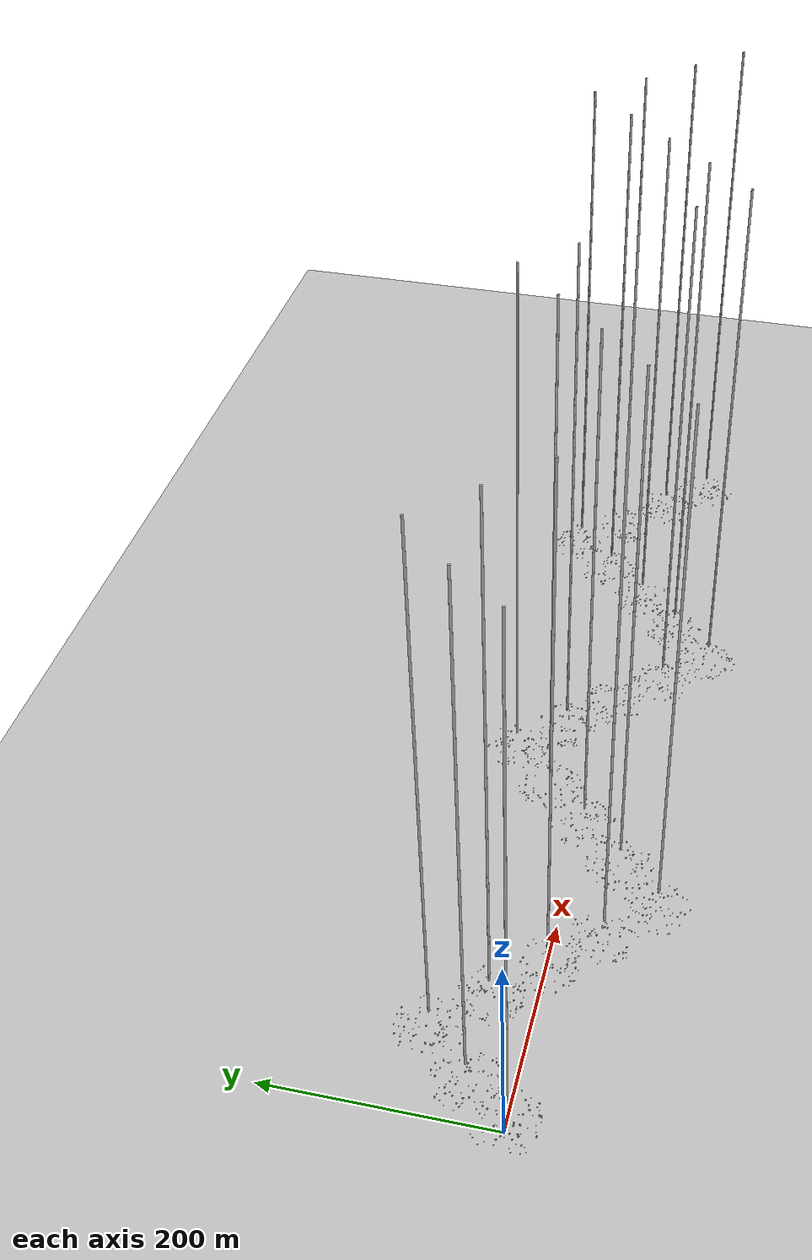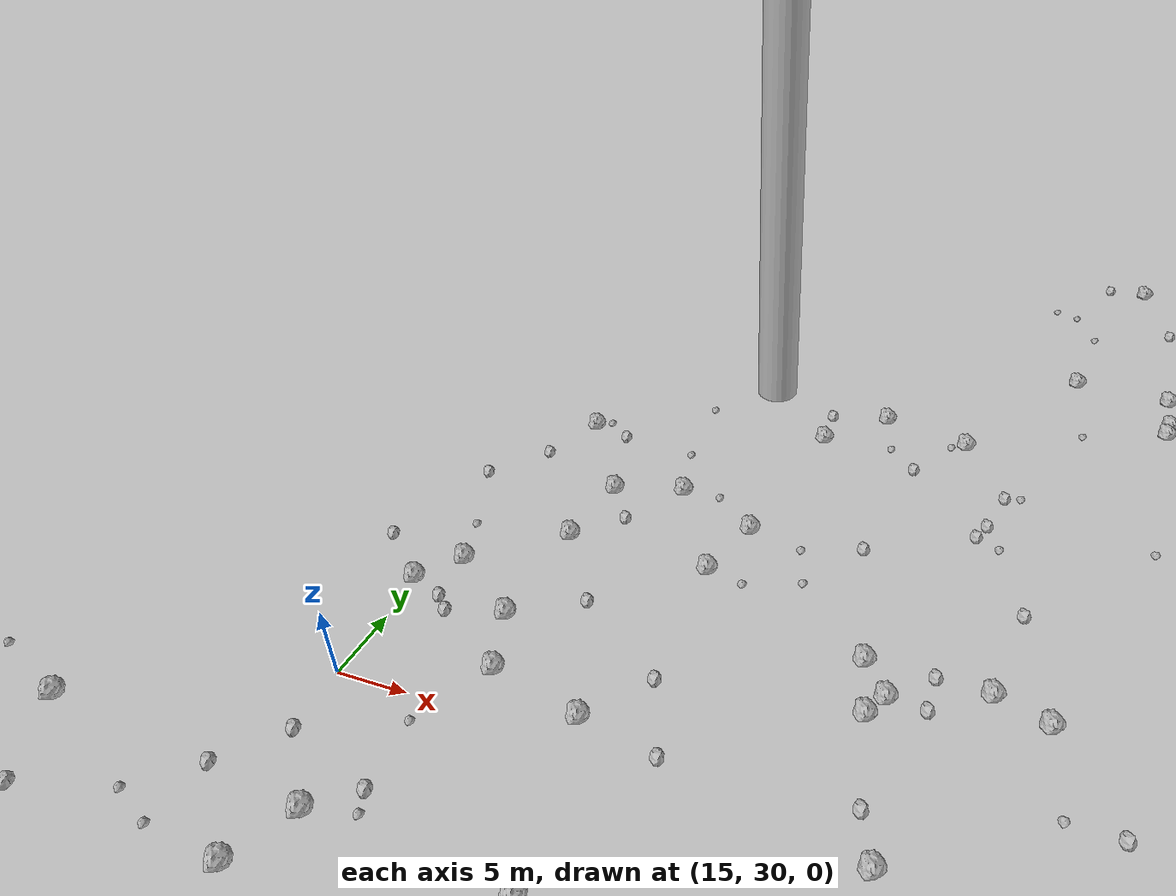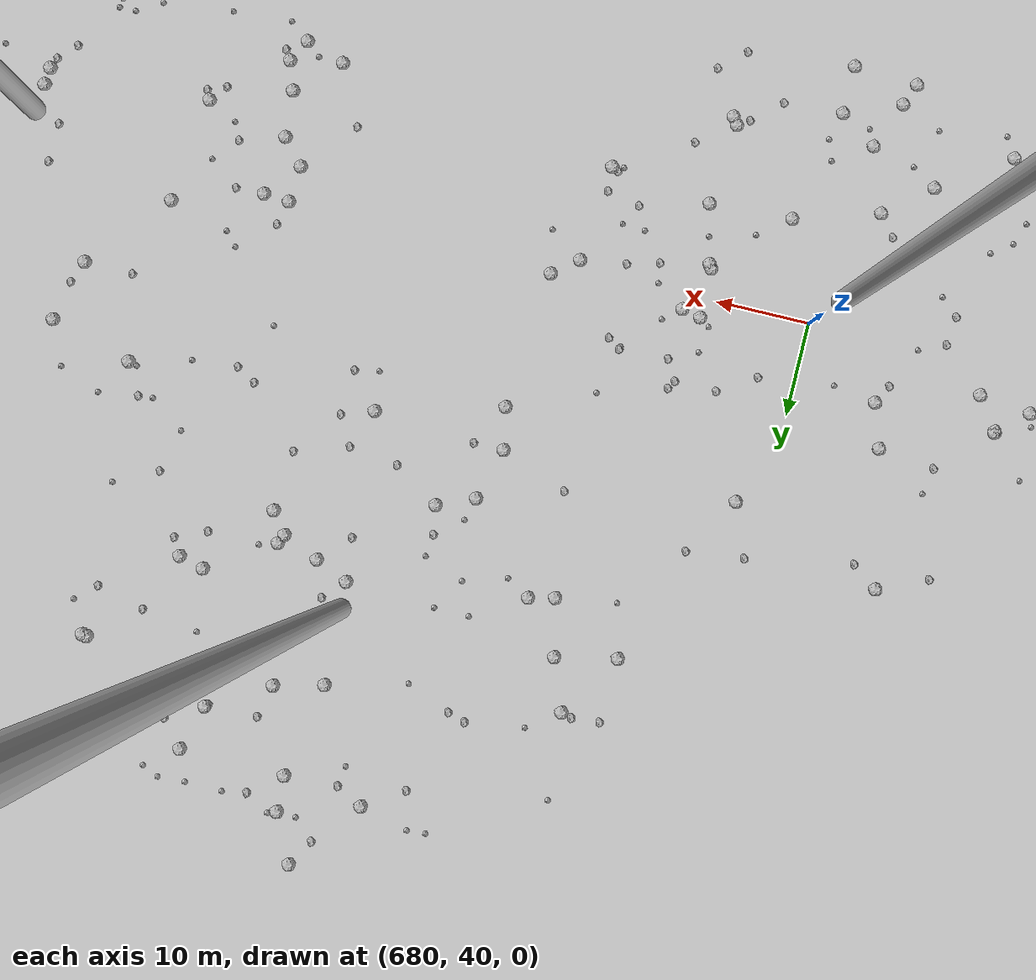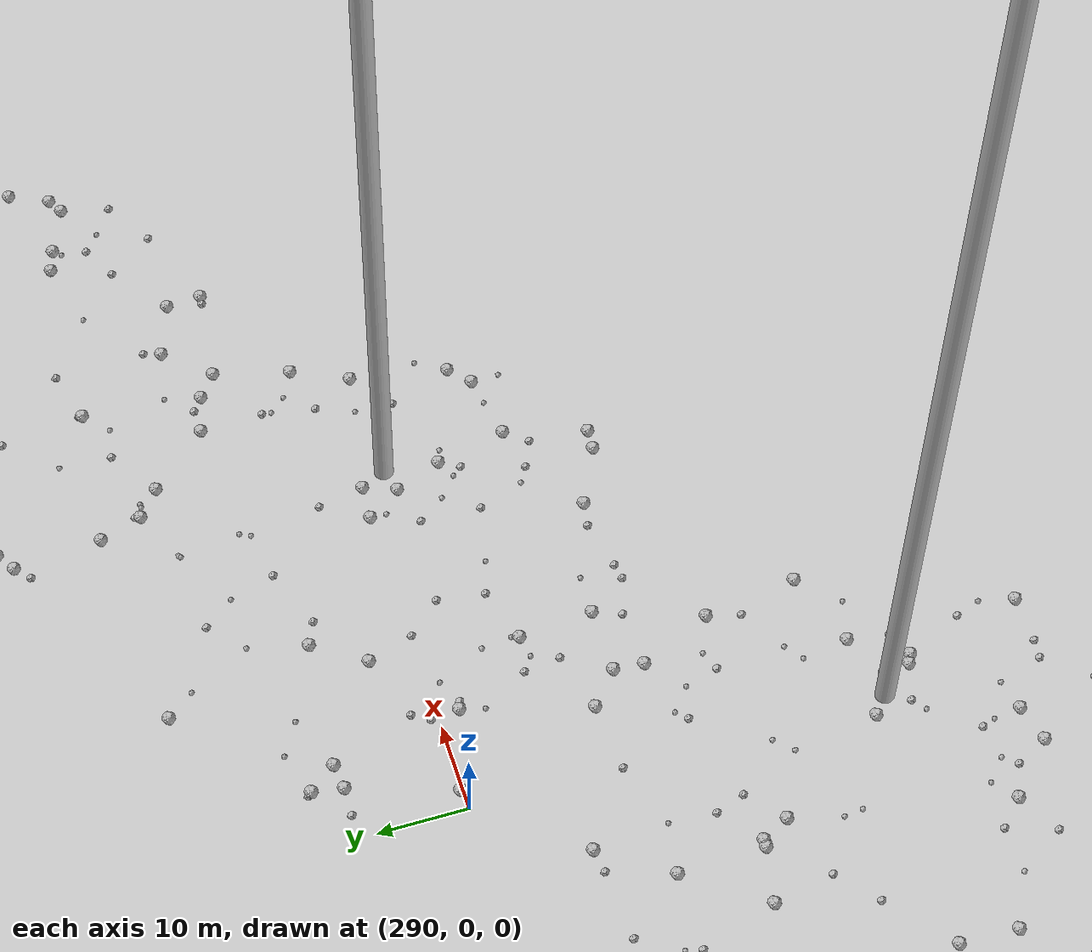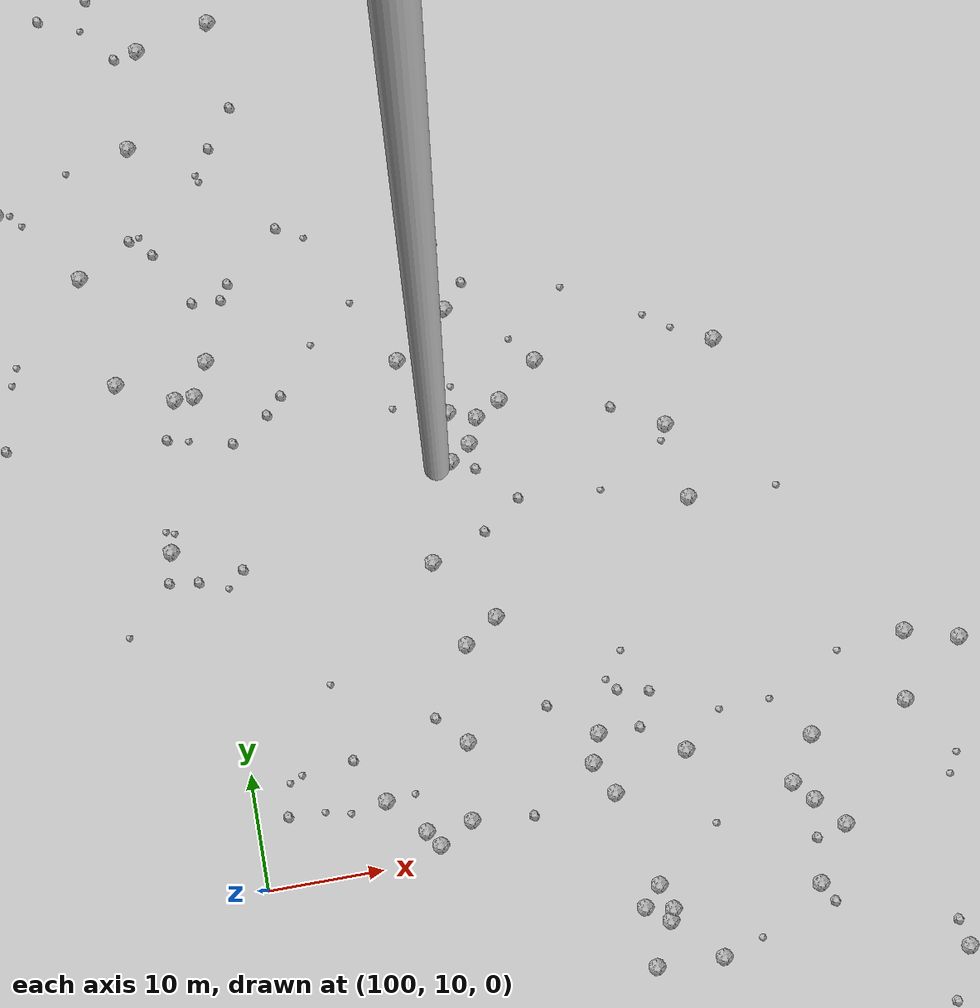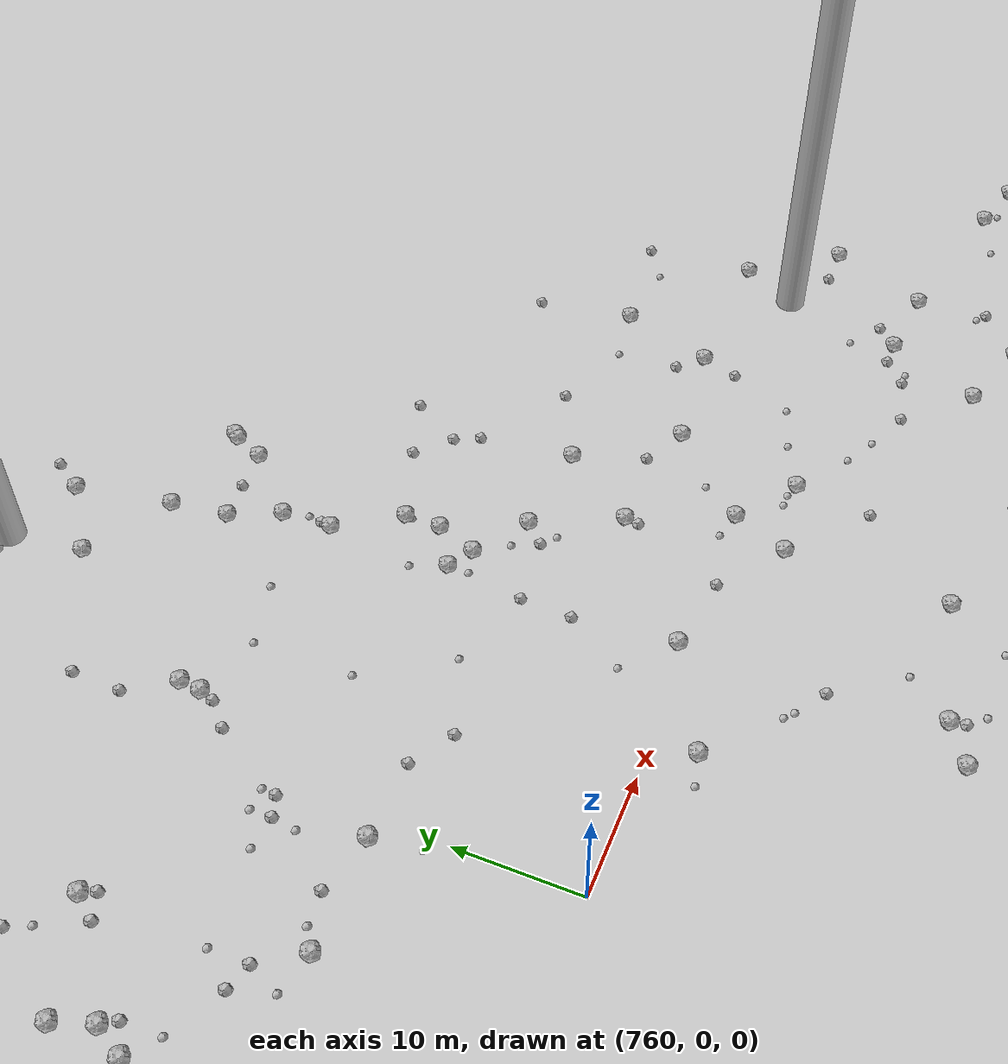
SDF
<sdf version="1.6">
 <world name="default">
  <include><uri>model://custom_ground</uri></include>
  <include><uri>model://sun</uri></include>
  <spherical_coordinates>
   <surface_model>EARTH_WGS84</surface_model>
   <latitude_deg>38.161479</latitude_deg>
   <longitude_deg>-122.454630</longitude_deg>
   <elevation>488.0</elevation>
   <heading_deg>90</heading_deg>
  </spherical_coordinates>
  <model name="rock1_0_0">
   <include><uri>model://rock1</uri><pose>0.7875030850327462 -4.04822088262074 0.5 0 0 0</pose></include>
  </model>
  <model name="rock1_0_1">
   <include><uri>model://rock1</uri><pose>-2.7111861532558557 2.1530737639394673 0.5 0 0 0</pose></include>
  </model>
  <model name="rock1_0_2">
   <include><uri>model://rock1</uri><pose>7.985816359673663 -5.506232215753201 0.5 0 0 0</pose></include>
  </model>
  <model name="rock1_0_3">
   <include><uri>model://rock1</uri><pose>17.602498212669488 17.258907443594573 0.5 0 0 0</pose></include>
  </model>
  <model name="rock1_0_4">
   <include><uri>model://rock1</uri><pose>9.952506052727355 -10.085083468673396 0.5 0 0 0</pose></include>
  </model>
  <model name="rock1_0_5">
   <include><uri>model://rock1</uri><pose>31.03313271992934 -21.007227643195233 0.5 0 0 0</pose></include>
  </model>
  <model name="rock1_0_6">
   <include><uri>model://rock1</uri><pose>-3.996822052795313 -7.189291991120637 0.5 0 0 0</pose></include>
  </model>
  <model name="rock1_0_7">
   <include><uri>model://rock1</uri><pose>20.21150958165927 -24.655644110509332 0.5 0 0 0</pose></include>
  </model>
  <model name="rock1_0_8">
   <include><uri>model://rock1</uri><pose>-1.4466466936435936 15.477507277876853 0.5 0 0 0</pose></include>
  </model>
  <model name="rock1_0_9">
   <include><uri>model://rock1</uri><pose>-6.432573667976872 4.871958737552063 0.5 0 0 0</pose></include>
  </model>
  <model name="rock1_0_10">
   <include><uri>model://rock1</uri><pose>-0.01444694796644086 22.80590339987952 0.5 0 0 0</pose></include>
  </model>
  <model name="rock1_0_11">
   <include><uri>model://rock1</uri><pose>19.186959616523175 -10.704681527130358 0.5 0 0 0</pose></include>
  </model>
  <model name="rock1_0_12">
   <include><uri>model://rock1</uri><pose>32.60450139885152 6.42078220438227 0.5 0 0 0</pose></include>
  </model>
  <model name="rock1_0_13">
   <include><uri>model://rock1</uri><pose>37.77949229154332 0.40364812318980015 0.5 0 0 0</pose></include>
  </model>
  <model name="rock1_0_14">
   <include><uri>model://rock1</uri><pose>31.51720776210619 -9.896221459575393 0.5 0 0 0</pose></include>
  </model>
  <model name="rock1_0_15">
   <include><uri>model://rock1</uri><pose>2.6852934214707886 -24.85855729662057 0.5 0 0 0</pose></include>
  </model>
  <model name="rock1_0_16">
   <include><uri>model://rock1</uri><pose>27.403807800710034 -13.240702402883525 0.5 0 0 0</pose></include>
  </model>
  <model name="rock1_0_17">
   <include><uri>model://rock1</uri><pose>4.011364625854537 8.976292649463993 0.5 0 0 0</pose></include>
  </model>
  <model name="rock1_0_18">
   <include><uri>model://rock1</uri><pose>-6.756805535585588 -15.08864236582834 0.5 0 0 0</pose></include>
  </model>
  <model name="rock1_0_19">
   <include><uri>model://rock1</uri><pose>10.303637147243311 -5.205839640888364 0.5 0 0 0</pose></include>
  </model>
  <model name="rock1_0_20">
   <include><uri>model://rock1</uri><pose>1.3918737082313264 -10.405997280427446 0.5 0 0 0</pose></include>
  </model>
  <model name="rock1_0_21">
   <include><uri>model://rock1</uri><pose>20.837829507860825 -23.089753855115188 0.5 0 0 0</pose></include>
  </model>
  <model name="rock1_0_22">
   <include><uri>model://rock1</uri><pose>-0.40330023845260143 -11.4003688657128 0.5 0 0 0</pose></include>
  </model>
  <model name="rock1_0_23">
   <include><uri>model://rock1</uri><pose>23.709320429566354 -14.630583677230621 0.5 0 0 0</pose></include>
  </model>
  <model name="rock1_0_24">
   <include><uri>model://rock1</uri><pose>-2.0148362346716624 16.06418049051362 0.5 0 0 0</pose></include>
  </model>
  <model name="rock1_0_25">
   <include><uri>model://rock1</uri><pose>29.085387182633937 9.616338570745775 0.5 0 0 0</pose></include>
  </model>
  <model name="rock1_0_26">
   <include><uri>model://rock1</uri><pose>5.8333308023137285 2.4184907663539406 0.5 0 0 0</pose></include>
  </model>
  <model name="rock2_0_0">
   <include><uri>model://rock2</uri><pose>28.268709765897604 -1.68577425489298 0.3 0 0 0</pose></include>
  </model>
  <model name="rock2_0_1">
   <include><uri>model://rock2</uri><pose>-12.146891351048744 -19.821802666213404 0.3 0 0 0</pose></include>
  </model>
  <model name="rock2_0_2">
   <include><uri>model://rock2</uri><pose>27.89796755954073 -20.006159197864385 0.3 0 0 0</pose></include>
  </model>
  <model name="rock2_0_3">
   <include><uri>model://rock2</uri><pose>2.922889484942189 17.198767779272174 0.3 0 0 0</pose></include>
  </model>
  <model name="rock2_0_4">
   <include><uri>model://rock2</uri><pose>-3.08425853732286 -1.0393787969276218 0.3 0 0 0</pose></include>
  </model>
  <model name="rock2_0_5">
   <include><uri>model://rock2</uri><pose>-8.016368929878382 -17.723118522531678 0.3 0 0 0</pose></include>
  </model>
  <model name="rock2_0_6">
   <include><uri>model://rock2</uri><pose>14.984104677958179 8.471981866289092 0.3 0 0 0</pose></include>
  </model>
  <model name="rock2_0_7">
   <include><uri>model://rock2</uri><pose>21.735861101134773 -2.003883832324199 0.3 0 0 0</pose></include>
  </model>
  <model name="rock2_0_8">
   <include><uri>model://rock2</uri><pose>-6.783358058160545 -10.753873415531746 0.3 0 0 0</pose></include>
  </model>
  <model name="rock2_0_9">
   <include><uri>model://rock2</uri><pose>2.0985516783471816 -12.931910236654392 0.3 0 0 0</pose></include>
  </model>
  <model name="rock2_0_10">
   <include><uri>model://rock2</uri><pose>38.84777082378566 -5.2036733217507205 0.3 0 0 0</pose></include>
  </model>
  <model name="rock2_0_11">
   <include><uri>model://rock2</uri><pose>5.222273045044901 6.892764648980027 0.3 0 0 0</pose></include>
  </model>
  <model name="rock2_0_12">
   <include><uri>model://rock2</uri><pose>-8.303062208619892 22.527953180964907 0.3 0 0 0</pose></include>
  </model>
  <model name="rock2_0_13">
   <include><uri>model://rock2</uri><pose>-14.483207819141217 -8.357459652357388 0.3 0 0 0</pose></include>
  </model>
  <model name="rock2_0_14">
   <include><uri>model://rock2</uri><pose>-13.87097827279119 -15.936442516931596 0.3 0 0 0</pose></include>
  </model>
  <model name="rock2_0_15">
   <include><uri>model://rock2</uri><pose>21.97850377354515 23.391824280835706 0.3 0 0 0</pose></include>
  </model>
  <model name="rock2_0_16">
   <include><uri>model://rock2</uri><pose>-13.304331317824527 17.25149082010803 0.3 0 0 0</pose></include>
  </model>
  <model name="rock2_0_17">
   <include><uri>model://rock2</uri><pose>9.299296060576097 -5.68981607277405 0.3 0 0 0</pose></include>
  </model>
  <model name="rock2_0_18">
   <include><uri>model://rock2</uri><pose>17.799675408286134 10.382769883957643 0.3 0 0 0</pose></include>
  </model>
  <model name="rock2_0_19">
   <include><uri>model://rock2</uri><pose>9.225234947846776 -10.989969129161217 0.3 0 0 0</pose></include>
  </model>
  <model name="rock2_0_20">
   <include><uri>model://rock2</uri><pose>6.2437899992456 -23.538022837997097 0.3 0 0 0</pose></include>
  </model>
  <model name="rock2_0_21">
   <include><uri>model://rock2</uri><pose>8.2608150524944 -16.776091720262123 0.3 0 0 0</pose></include>
  </model>
  <model name="rock2_0_22">
   <include><uri>model://rock2</uri><pose>14.057184572718924 8.825684909375568 0.3 0 0 0</pose></include>
  </model>
  <model name="rock2_0_23">
   <include><uri>model://rock2</uri><pose>17.77864821219029 -7.604061161005184 0.3 0 0 0</pose></include>
  </model>
  <model name="rock2_0_24">
   <include><uri>model://rock2</uri><pose>33.242296094638235 9.123662745760882 0.3 0 0 0</pose></include>
  </model>
  <model name="rock2_0_25">
   <include><uri>model://rock2</uri><pose>-11.132206749112308 5.459568788519832 0.3 0 0 0</pose></include>
  </model>
  <model name="rock2_0_26">
   <include><uri>model://rock2</uri><pose>12.526713823326133 21.962936251820054 0.3 0 0 0</pose></include>
  </model>
  <model name="rock3_0_0">
   <include><uri>model://rock3</uri><pose>12.054015494312836 17.731121274848363 0.2 0 0 0</pose></include>
  </model>
  <model name="rock3_0_1">
   <include><uri>model://rock3</uri><pose>-9.906882506905859 13.243158481525008 0.2 0 0 0</pose></include>
  </model>
  <model name="rock3_0_2">
   <include><uri>model://rock3</uri><pose>24.529564438278676 -7.4099779441867994 0.2 0 0 0</pose></include>
  </model>
  <model name="rock3_0_3">
   <include><uri>model://rock3</uri><pose>34.63667282208111 -13.522424849850697 0.2 0 0 0</pose></include>
  </model>
  <model name="rock3_0_4">
   <include><uri>model://rock3</uri><pose>12.48390519126729 -9.432836493978812 0.2 0 0 0</pose></include>
  </model>
  <model name="rock3_0_5">
   <include><uri>model://rock3</uri><pose>15.257257353078195 -25.560380298334167 0.2 0 0 0</pose></include>
  </model>
  <model name="rock3_0_6">
   <include><uri>model://rock3</uri><pose>-11.544431869315702 -6.555700940732468 0.2 0 0 0</pose></include>
  </model>
  <model name="rock3_0_7">
   <include><uri>model://rock3</uri><pose>26.738650635126156 7.050562331172706 0.2 0 0 0</pose></include>
  </model>
  <model name="rock3_0_8">
   <include><uri>model://rock3</uri><pose>31.6573957165228 -15.906352729226 0.2 0 0 0</pose></include>
  </model>
  <model name="rock3_0_9">
   <include><uri>model://rock3</uri><pose>18.557197933414876 -21.4919400926863 0.2 0 0 0</pose></include>
  </model>
  <model name="rock3_0_10">
   <include><uri>model://rock3</uri><pose>27.791134720380498 14.471691890931112 0.2 0 0 0</pose></include>
  </model>
  <model name="rock3_0_11">
   <include><uri>model://rock3</uri><pose>25.089546671466024 -22.27406143521616 0.2 0 0 0</pose></include>
  </model>
  <model name="rock3_0_12">
   <include><uri>model://rock3</uri><pose>33.5584740451381 -8.231789663499843 0.2 0 0 0</pose></include>
  </model>
  <model name="rock3_0_13">
   <include><uri>model://rock3</uri><pose>-6.27817207429819 24.95625310285447 0.2 0 0 0</pose></include>
  </model>
  <model name="rock3_0_14">
   <include><uri>model://rock3</uri><pose>22.729636440763905 -10.090141284177879 0.2 0 0 0</pose></include>
  </model>
  <model name="rock3_0_15">
   <include><uri>model://rock3</uri><pose>19.175820733388413 -25.676020577659546 0.2 0 0 0</pose></include>
  </model>
  <model name="rock3_0_16">
   <include><uri>model://rock3</uri><pose>12.704682493725706 -1.783504664536757 0.2 0 0 0</pose></include>
  </model>
  <model name="rock3_0_17">
   <include><uri>model://rock3</uri><pose>12.094698205304695 -22.54921598707095 0.2 0 0 0</pose></include>
  </model>
  <model name="rock3_0_18">
   <include><uri>model://rock3</uri><pose>9.05407370866331 19.003188183311252 0.2 0 0 0</pose></include>
  </model>
  <model name="rock3_0_19">
   <include><uri>model://rock3</uri><pose>29.89618698043254 -5.169035510458983 0.2 0 0 0</pose></include>
  </model>
  <model name="rock3_0_20">
   <include><uri>model://rock3</uri><pose>1.76195425328563 8.030049208032331 0.2 0 0 0</pose></include>
  </model>
  <model name="rock3_0_21">
   <include><uri>model://rock3</uri><pose>18.258029322631835 -16.797865856713685 0.2 0 0 0</pose></include>
  </model>
  <model name="rock3_0_22">
   <include><uri>model://rock3</uri><pose>5.404159282481093 8.478696226838863 0.2 0 0 0</pose></include>
  </model>
  <model name="rock3_0_23">
   <include><uri>model://rock3</uri><pose>-0.6676806894450138 4.165155590969448 0.2 0 0 0</pose></include>
  </model>
  <model name="rock3_0_24">
   <include><uri>model://rock3</uri><pose>19.789165539474546 -18.198244083598674 0.2 0 0 0</pose></include>
  </model>
  <model name="rock3_0_25">
   <include><uri>model://rock3</uri><pose>7.503106391540001 -0.5140416416009188 0.2 0 0 0</pose></include>
  </model>
  <model name="rock3_0_26">
   <include><uri>model://rock3</uri><pose>-0.5710477176585123 11.871504265855343 0.2 0 0 0</pose></include>
  </model>
  <model name="rock1_1_0">
   <include><uri>model://rock1</uri><pose>33.33386350619676 46.21291824714294 0.5 0 0 0</pose></include>
  </model>
  <model name="rock1_1_1">
   <include><uri>model://rock1</uri><pose>34.76665267079015 51.206951914762655 0.5 0 0 0</pose></include>
  </model>
  <model name="rock1_1_2">
   <include><uri>model://rock1</uri><pose>14.67277170424234 38.76017911023217 0.5 0 0 0</pose></include>
  </model>
  <model name="rock1_1_3">
   <include><uri>model://rock1</uri><pose>41.11350170424859 68.3701248203329 0.5 0 0 0</pose></include>
  </model>
  <model name="rock1_1_4">
   <include><uri>model://rock1</uri><pose>36.82695947778961 63.9825461771964 0.5 0 0 0</pose></include>
  </model>
  <model name="rock1_1_5">
   <include><uri>model://rock1</uri><pose>23.44035728002716 52.256052951728755 0.5 0 0 0</pose></include>
  </model>
  <model name="rock1_1_6">
   <include><uri>model://rock1</uri><pose>56.94815551411261 17.496450540130496 0.5 0 0 0</pose></include>
  </model>
  <model name="rock1_1_7">
   <include><uri>model://rock1</uri><pose>24.032582891720047 33.40013202286797 0.5 0 0 0</pose></include>
  </model>
  <model name="rock1_1_8">
   <include><uri>model://rock1</uri><pose>57.13576490426609 40.35627078414109 0.5 0 0 0</pose></include>
  </model>
  <model name="rock1_1_9">
   <include><uri>model://rock1</uri><pose>53.58568339837626 41.53896246761599 0.5 0 0 0</pose></include>
  </model>
  <model name="rock1_1_10">
   <include><uri>model://rock1</uri><pose>47.51239307967745 39.23456506958117 0.5 0 0 0</pose></include>
  </model>
  <model name="rock1_1_11">
   <include><uri>model://rock1</uri><pose>49.32944799499962 28.04840569330965 0.5 0 0 0</pose></include>
  </model>
  <model name="rock1_1_12">
   <include><uri>model://rock1</uri><pose>28.51637937915226 53.77262395037561 0.5 0 0 0</pose></include>
  </model>
  <model name="rock1_1_13">
   <include><uri>model://rock1</uri><pose>46.644634914639454 37.59394316784055 0.5 0 0 0</pose></include>
  </model>
  <model name="rock1_1_14">
   <include><uri>model://rock1</uri><pose>16.85840872977772 41.564805440426 0.5 0 0 0</pose></include>
  </model>
  <model name="rock1_1_15">
   <include><uri>model://rock1</uri><pose>22.694556999023554 46.299389305252596 0.5 0 0 0</pose></include>
  </model>
  <model name="rock1_1_16">
   <include><uri>model://rock1</uri><pose>29.714991718342468 14.56325706456246 0.5 0 0 0</pose></include>
  </model>
  <model name="rock1_1_17">
   <include><uri>model://rock1</uri><pose>22.33489406049892 37.79912201557884 0.5 0 0 0</pose></include>
  </model>
  <model name="rock1_1_18">
   <include><uri>model://rock1</uri><pose>33.94608172486745 11.693291221199875 0.5 0 0 0</pose></include>
  </model>
  <model name="rock1_1_19">
   <include><uri>model://rock1</uri><pose>47.9295853766814 66.79299607092241 0.5 0 0 0</pose></include>
  </model>
  <model name="rock1_1_20">
   <include><uri>model://rock1</uri><pose>19.46029900777698 21.211037514983296 0.5 0 0 0</pose></include>
  </model>
  <model name="rock1_1_21">
   <include><uri>model://rock1</uri><pose>45.60485979890071 41.70026782523125 0.5 0 0 0</pose></include>
  </model>
  <model name="rock1_1_22">
   <include><uri>model://rock1</uri><pose>59.365745035766714 19.73314490809938 0.5 0 0 0</pose></include>
  </model>
  <model name="rock1_1_23">
   <include><uri>model://rock1</uri><pose>60.61996867650557 23.171465587789825 0.5 0 0 0</pose></include>
  </model>
  <model name="rock1_1_24">
   <include><uri>model://rock1</uri><pose>30.73009076585231 31.75869820767785 0.5 0 0 0</pose></include>
  </model>
  <model name="rock1_1_25">
   <include><uri>model://rock1</uri><pose>18.390496676564098 59.52154212190945 0.5 0 0 0</pose></include>
  </model>
  <model name="rock1_1_26">
   <include><uri>model://rock1</uri><pose>32.78107202424813 20.7360352080128 0.5 0 0 0</pose></include>
  </model>
  <model name="rock2_1_0">
   <include><uri>model://rock2</uri><pose>16.540765604466824 54.742760747203846 0.3 0 0 0</pose></include>
  </model>
  <model name="rock2_1_1">
   <include><uri>model://rock2</uri><pose>47.81536411552145 21.1021001942364 0.3 0 0 0</pose></include>
  </model>
  <model name="rock2_1_2">
   <include><uri>model://rock2</uri><pose>36.272746665041595 30.67560162734485 0.3 0 0 0</pose></include>
  </model>
  <model name="rock2_1_3">
   <include><uri>model://rock2</uri><pose>18.414508185157246 36.717628160268106 0.3 0 0 0</pose></include>
  </model>
  <model name="rock2_1_4">
   <include><uri>model://rock2</uri><pose>21.479724615924145 58.72459545967233 0.3 0 0 0</pose></include>
  </model>
  <model name="rock2_1_5">
   <include><uri>model://rock2</uri><pose>54.56755227837164 48.85346701646162 0.3 0 0 0</pose></include>
  </model>
  <model name="rock2_1_6">
   <include><uri>model://rock2</uri><pose>51.76089041142019 60.8705683416187 0.3 0 0 0</pose></include>
  </model>
  <model name="rock2_1_7">
   <include><uri>model://rock2</uri><pose>13.279509100059261 50.84071211916738 0.3 0 0 0</pose></include>
  </model>
  <model name="rock2_1_8">
   <include><uri>model://rock2</uri><pose>64.94201173838852 33.898356187754516 0.3 0 0 0</pose></include>
  </model>
  <model name="rock2_1_9">
   <include><uri>model://rock2</uri><pose>17.282969686299936 37.74105917030174 0.3 0 0 0</pose></include>
  </model>
  <model name="rock2_1_10">
   <include><uri>model://rock2</uri><pose>10.623767172619608 42.11573973438904 0.3 0 0 0</pose></include>
  </model>
  <model name="rock2_1_11">
   <include><uri>model://rock2</uri><pose>43.08050546997212 51.75808081462821 0.3 0 0 0</pose></include>
  </model>
  <model name="rock2_1_12">
   <include><uri>model://rock2</uri><pose>50.977474872949266 57.18476617869242 0.3 0 0 0</pose></include>
  </model>
  <model name="rock2_1_13">
   <include><uri>model://rock2</uri><pose>50.41223262071739 55.74129704232931 0.3 0 0 0</pose></include>
  </model>
  <model name="rock2_1_14">
   <include><uri>model://rock2</uri><pose>33.856204401220126 35.885066901936796 0.3 0 0 0</pose></include>
  </model>
  <model name="rock2_1_15">
   <include><uri>model://rock2</uri><pose>47.01506637288793 15.388245592451481 0.3 0 0 0</pose></include>
  </model>
  <model name="rock2_1_16">
   <include><uri>model://rock2</uri><pose>50.07266613520392 41.73855792218181 0.3 0 0 0</pose></include>
  </model>
  <model name="rock2_1_17">
   <include><uri>model://rock2</uri><pose>47.94386511755906 31.252144303089842 0.3 0 0 0</pose></include>
  </model>
  <model name="rock2_1_18">
   <include><uri>model://rock2</uri><pose>50.076508504341945 39.058272202678296 0.3 0 0 0</pose></include>
  </model>
  <model name="rock2_1_19">
   <include><uri>model://rock2</uri><pose>32.19044118017112 13.571072971750302 0.3 0 0 0</pose></include>
  </model>
  <model name="rock2_1_20">
   <include><uri>model://rock2</uri><pose>61.559841525219966 34.08512459584081 0.3 0 0 0</pose></include>
  </model>
  <model name="rock2_1_21">
   <include><uri>model://rock2</uri><pose>44.56386991687369 62.15969082491932 0.3 0 0 0</pose></include>
  </model>
  <model name="rock2_1_22">
   <include><uri>model://rock2</uri><pose>25.722204427666682 49.268245395012435 0.3 0 0 0</pose></include>
  </model>
  <model name="rock2_1_23">
   <include><uri>model://rock2</uri><pose>36.659440528906075 67.31370932264647 0.3 0 0 0</pose></include>
  </model>
  <model name="rock2_1_24">
   <include><uri>model://rock2</uri><pose>26.934803309168153 40.57870109826497 0.3 0 0 0</pose></include>
  </model>
  <model name="rock2_1_25">
   <include><uri>model://rock2</uri><pose>28.010692492196487 16.686377083479194 0.3 0 0 0</pose></include>
  </model>
  <model name="rock2_1_26">
   <include><uri>model://rock2</uri><pose>15.492953913405614 25.451937856620688 0.3 0 0 0</pose></include>
  </model>
  <model name="rock3_1_0">
   <include><uri>model://rock3</uri><pose>37.58145976320898 12.817510810970457 0.2 0 0 0</pose></include>
  </model>
  <model name="rock3_1_1">
   <include><uri>model://rock3</uri><pose>15.62860449454428 45.119606558602705 0.2 0 0 0</pose></include>
  </model>
  <model name="rock3_1_2">
   <include><uri>model://rock3</uri><pose>35.92897953949745 17.40372285641846 0.2 0 0 0</pose></include>
  </model>
  <model name="rock3_1_3">
   <include><uri>model://rock3</uri><pose>22.533380343138763 21.99201913139536 0.2 0 0 0</pose></include>
  </model>
  <model name="rock3_1_4">
   <include><uri>model://rock3</uri><pose>39.972607984842085 47.01395772053091 0.2 0 0 0</pose></include>
  </model>
  <model name="rock3_1_5">
   <include><uri>model://rock3</uri><pose>64.62780285446279 53.87714097145261 0.2 0 0 0</pose></include>
  </model>
  <model name="rock3_1_6">
   <include><uri>model://rock3</uri><pose>38.35044992061599 19.584042862208978 0.2 0 0 0</pose></include>
  </model>
  <model name="rock3_1_7">
   <include><uri>model://rock3</uri><pose>27.331241745064936 58.2323468359238 0.2 0 0 0</pose></include>
  </model>
  <model name="rock3_1_8">
   <include><uri>model://rock3</uri><pose>64.67413140350732 48.21190804409108 0.2 0 0 0</pose></include>
  </model>
  <model name="rock3_1_9">
   <include><uri>model://rock3</uri><pose>36.080002315634374 45.573943006625356 0.2 0 0 0</pose></include>
  </model>
  <model name="rock3_1_10">
   <include><uri>model://rock3</uri><pose>38.88567656233866 50.2031631974996 0.2 0 0 0</pose></include>
  </model>
  <model name="rock3_1_11">
   <include><uri>model://rock3</uri><pose>53.41999174658318 14.775565999586227 0.2 0 0 0</pose></include>
  </model>
  <model name="rock3_1_12">
   <include><uri>model://rock3</uri><pose>62.614835740226255 58.00852773255626 0.2 0 0 0</pose></include>
  </model>
  <model name="rock3_1_13">
   <include><uri>model://rock3</uri><pose>46.314984334618245 23.3554159345127 0.2 0 0 0</pose></include>
  </model>
  <model name="rock3_1_14">
   <include><uri>model://rock3</uri><pose>58.31270417072142 34.15961170527993 0.2 0 0 0</pose></include>
  </model>
  <model name="rock3_1_15">
   <include><uri>model://rock3</uri><pose>31.390211558828504 53.84747004637125 0.2 0 0 0</pose></include>
  </model>
  <model name="rock3_1_16">
   <include><uri>model://rock3</uri><pose>52.91379521998911 61.20437277516944 0.2 0 0 0</pose></include>
  </model>
  <model name="rock3_1_17">
   <include><uri>model://rock3</uri><pose>19.427195473452237 60.19714361472564 0.2 0 0 0</pose></include>
  </model>
  <model name="rock3_1_18">
   <include><uri>model://rock3</uri><pose>62.92546602142723 20.714221174313582 0.2 0 0 0</pose></include>
  </model>
  <model name="rock3_1_19">
   <include><uri>model://rock3</uri><pose>63.74571342834128 31.188700087149982 0.2 0 0 0</pose></include>
  </model>
  <model name="rock3_1_20">
   <include><uri>model://rock3</uri><pose>48.35934104989192 16.275822613003918 0.2 0 0 0</pose></include>
  </model>
  <model name="rock3_1_21">
   <include><uri>model://rock3</uri><pose>21.47473388701207 28.204233067807806 0.2 0 0 0</pose></include>
  </model>
  <model name="rock3_1_22">
   <include><uri>model://rock3</uri><pose>47.040691746770534 11.534711679901989 0.2 0 0 0</pose></include>
  </model>
  <model name="rock3_1_23">
   <include><uri>model://rock3</uri><pose>52.14695849026296 54.89638956539291 0.2 0 0 0</pose></include>
  </model>
  <model name="rock3_1_24">
   <include><uri>model://rock3</uri><pose>26.89994777274749 64.91574492622706 0.2 0 0 0</pose></include>
  </model>
  <model name="rock3_1_25">
   <include><uri>model://rock3</uri><pose>46.81340650130932 66.17553166550246 0.2 0 0 0</pose></include>
  </model>
  <model name="rock3_1_26">
   <include><uri>model://rock3</uri><pose>42.275483811412506 64.34959045632468 0.2 0 0 0</pose></include>
  </model>
  <model name="rock1_2_0">
   <include><uri>model://rock1</uri><pose>63.549347035234895 75.16183590662179 0.5 0 0 0</pose></include>
  </model>
  <model name="rock1_2_1">
   <include><uri>model://rock1</uri><pose>63.286522700774384 73.73867657658916 0.5 0 0 0</pose></include>
  </model>
  <model name="rock1_2_2">
   <include><uri>model://rock1</uri><pose>74.71246042094722 64.59648420289447 0.5 0 0 0</pose></include>
  </model>
  <model name="rock1_2_3">
   <include><uri>model://rock1</uri><pose>63.39520811119574 78.97354202266848 0.5 0 0 0</pose></include>
  </model>
  <model name="rock1_2_4">
   <include><uri>model://rock1</uri><pose>99.74022290185297 86.7991996695971 0.5 0 0 0</pose></include>
  </model>
  <model name="rock1_2_5">
   <include><uri>model://rock1</uri><pose>83.01732115742561 71.98314485711391 0.5 0 0 0</pose></include>
  </model>
  <model name="rock1_2_6">
   <include><uri>model://rock1</uri><pose>72.94877780489479 66.42496629593808 0.5 0 0 0</pose></include>
  </model>
  <model name="rock1_2_7">
   <include><uri>model://rock1</uri><pose>74.91124108908971 99.8855292800925 0.5 0 0 0</pose></include>
  </model>
  <model name="rock1_2_8">
   <include><uri>model://rock1</uri><pose>82.83451619296608 98.47727739477739 0.5 0 0 0</pose></include>
  </model>
  <model name="rock1_2_9">
   <include><uri>model://rock1</uri><pose>67.42984930750207 106.2051731086284 0.5 0 0 0</pose></include>
  </model>
  <model name="rock1_2_10">
   <include><uri>model://rock1</uri><pose>69.96576582609772 52.239211531971236 0.5 0 0 0</pose></include>
  </model>
  <model name="rock1_2_11">
   <include><uri>model://rock1</uri><pose>55.7324150785894 79.5628604119398 0.5 0 0 0</pose></include>
  </model>
  <model name="rock1_2_12">
   <include><uri>model://rock1</uri><pose>74.26137764597063 73.76787145765624 0.5 0 0 0</pose></include>
  </model>
  <model name="rock1_2_13">
   <include><uri>model://rock1</uri><pose>73.40834595899923 70.99623312525387 0.5 0 0 0</pose></include>
  </model>
  <model name="rock1_2_14">
   <include><uri>model://rock1</uri><pose>106.50124928941477 88.43443771786835 0.5 0 0 0</pose></include>
  </model>
  <model name="rock1_2_15">
   <include><uri>model://rock1</uri><pose>93.42379005954012 56.06203734411611 0.5 0 0 0</pose></include>
  </model>
  <model name="rock1_2_16">
   <include><uri>model://rock1</uri><pose>60.971703722923785 99.31589878384287 0.5 0 0 0</pose></include>
  </model>
  <model name="rock1_2_17">
   <include><uri>model://rock1</uri><pose>92.64707435487637 106.87352934493254 0.5 0 0 0</pose></include>
  </model>
  <model name="rock1_2_18">
   <include><uri>model://rock1</uri><pose>84.95551924911325 73.40555174410774 0.5 0 0 0</pose></include>
  </model>
  <model name="rock1_2_19">
   <include><uri>model://rock1</uri><pose>65.0569208355936 72.3463080380683 0.5 0 0 0</pose></include>
  </model>
  <model name="rock1_2_20">
   <include><uri>model://rock1</uri><pose>91.60778564777777 66.29787833764799 0.5 0 0 0</pose></include>
  </model>
  <model name="rock1_2_21">
   <include><uri>model://rock1</uri><pose>97.6154527705032 77.67346378573522 0.5 0 0 0</pose></include>
  </model>
  <model name="rock1_2_22">
   <include><uri>model://rock1</uri><pose>79.7476450756516 82.83643043335172 0.5 0 0 0</pose></include>
  </model>
  <model name="rock1_2_23">
   <include><uri>model://rock1</uri><pose>67.60147718434939 68.34992412205312 0.5 0 0 0</pose></include>
  </model>
  <model name="rock1_2_24">
   <include><uri>model://rock1</uri><pose>68.18931790630242 90.27244434205191 0.5 0 0 0</pose></include>
  </model>
  <model name="rock1_2_25">
   <include><uri>model://rock1</uri><pose>72.5655626093581 66.78492815771159 0.5 0 0 0</pose></include>
  </model>
  <model name="rock1_2_26">
   <include><uri>model://rock1</uri><pose>79.87277623263225 69.69585007492032 0.5 0 0 0</pose></include>
  </model>
  <model name="rock2_2_0">
   <include><uri>model://rock2</uri><pose>68.78068108897975 64.76788619848296 0.3 0 0 0</pose></include>
  </model>
  <model name="rock2_2_1">
   <include><uri>model://rock2</uri><pose>82.90823024104292 66.61424793555568 0.3 0 0 0</pose></include>
  </model>
  <model name="rock2_2_2">
   <include><uri>model://rock2</uri><pose>107.24982399031785 80.0892376563915 0.3 0 0 0</pose></include>
  </model>
  <model name="rock2_2_3">
   <include><uri>model://rock2</uri><pose>82.9579008961015 51.77375001572374 0.3 0 0 0</pose></include>
  </model>
  <model name="rock2_2_4">
   <include><uri>model://rock2</uri><pose>104.74965672284497 76.55052365531812 0.3 0 0 0</pose></include>
  </model>
  <model name="rock2_2_5">
   <include><uri>model://rock2</uri><pose>91.13760056400145 91.24668168399822 0.3 0 0 0</pose></include>
  </model>
  <model name="rock2_2_6">
   <include><uri>model://rock2</uri><pose>84.82264617511757 92.53289460991152 0.3 0 0 0</pose></include>
  </model>
  <model name="rock2_2_7">
   <include><uri>model://rock2</uri><pose>96.42942987078553 69.09315169810097 0.3 0 0 0</pose></include>
  </model>
  <model name="rock2_2_8">
   <include><uri>model://rock2</uri><pose>70.14702569762079 94.46759936663855 0.3 0 0 0</pose></include>
  </model>
  <model name="rock2_2_9">
   <include><uri>model://rock2</uri><pose>76.04361433746394 71.20940306610001 0.3 0 0 0</pose></include>
  </model>
  <model name="rock2_2_10">
   <include><uri>model://rock2</uri><pose>69.9687928656252 88.41104561496397 0.3 0 0 0</pose></include>
  </model>
  <model name="rock2_2_11">
   <include><uri>model://rock2</uri><pose>86.76548378615682 105.65345151337348 0.3 0 0 0</pose></include>
  </model>
  <model name="rock2_2_12">
   <include><uri>model://rock2</uri><pose>75.76828389757145 108.84750042161903 0.3 0 0 0</pose></include>
  </model>
  <model name="rock2_2_13">
   <include><uri>model://rock2</uri><pose>107.18822829649176 92.0440562923392 0.3 0 0 0</pose></include>
  </model>
  <model name="rock2_2_14">
   <include><uri>model://rock2</uri><pose>81.59412093183725 68.70492929429315 0.3 0 0 0</pose></include>
  </model>
  <model name="rock2_2_15">
   <include><uri>model://rock2</uri><pose>101.155946242353 62.43299013001775 0.3 0 0 0</pose></include>
  </model>
  <model name="rock2_2_16">
   <include><uri>model://rock2</uri><pose>85.6614269861285 108.8662464020097 0.3 0 0 0</pose></include>
  </model>
  <model name="rock2_2_17">
   <include><uri>model://rock2</uri><pose>105.34212154024257 94.66237135757635 0.3 0 0 0</pose></include>
  </model>
  <model name="rock2_2_18">
   <include><uri>model://rock2</uri><pose>65.47862617314556 100.55143774343449 0.3 0 0 0</pose></include>
  </model>
  <model name="rock2_2_19">
   <include><uri>model://rock2</uri><pose>63.40660628216516 91.11519535417472 0.3 0 0 0</pose></include>
  </model>
  <model name="rock2_2_20">
   <include><uri>model://rock2</uri><pose>57.64251059625461 99.14712001274653 0.3 0 0 0</pose></include>
  </model>
  <model name="rock2_2_21">
   <include><uri>model://rock2</uri><pose>98.32816107024802 67.47762721115751 0.3 0 0 0</pose></include>
  </model>
  <model name="rock2_2_22">
   <include><uri>model://rock2</uri><pose>86.5645702481126 104.53706896043313 0.3 0 0 0</pose></include>
  </model>
  <model name="rock2_2_23">
   <include><uri>model://rock2</uri><pose>95.71108623196834 92.51605932849824 0.3 0 0 0</pose></include>
  </model>
  <model name="rock2_2_24">
   <include><uri>model://rock2</uri><pose>97.5328371145136 86.43668395056915 0.3 0 0 0</pose></include>
  </model>
  <model name="rock2_2_25">
   <include><uri>model://rock2</uri><pose>82.99782009119262 104.67218043878745 0.3 0 0 0</pose></include>
  </model>
  <model name="rock2_2_26">
   <include><uri>model://rock2</uri><pose>64.44682572410359 64.3830004370719 0.3 0 0 0</pose></include>
  </model>
  <model name="rock3_2_0">
   <include><uri>model://rock3</uri><pose>87.07135839663788 72.1503500701688 0.2 0 0 0</pose></include>
  </model>
  <model name="rock3_2_1">
   <include><uri>model://rock3</uri><pose>81.0795559142606 91.81367129111499 0.2 0 0 0</pose></include>
  </model>
  <model name="rock3_2_2">
   <include><uri>model://rock3</uri><pose>103.43331021268202 73.54734704001231 0.2 0 0 0</pose></include>
  </model>
  <model name="rock3_2_3">
   <include><uri>model://rock3</uri><pose>94.81505618906255 89.69205737141094 0.2 0 0 0</pose></include>
  </model>
  <model name="rock3_2_4">
   <include><uri>model://rock3</uri><pose>86.1318939788259 73.27932376702992 0.2 0 0 0</pose></include>
  </model>
  <model name="rock3_2_5">
   <include><uri>model://rock3</uri><pose>78.11799997269907 52.588961981984795 0.2 0 0 0</pose></include>
  </model>
  <model name="rock3_2_6">
   <include><uri>model://rock3</uri><pose>103.21152143004143 74.20755692635541 0.2 0 0 0</pose></include>
  </model>
  <model name="rock3_2_7">
   <include><uri>model://rock3</uri><pose>65.11219039764492 79.96299326756109 0.2 0 0 0</pose></include>
  </model>
  <model name="rock3_2_8">
   <include><uri>model://rock3</uri><pose>79.49455658238966 67.6295284609796 0.2 0 0 0</pose></include>
  </model>
  <model name="rock3_2_9">
   <include><uri>model://rock3</uri><pose>56.73125531885853 71.28489988772822 0.2 0 0 0</pose></include>
  </model>
  <model name="rock3_2_10">
   <include><uri>model://rock3</uri><pose>52.870242857923536 92.74197114338767 0.2 0 0 0</pose></include>
  </model>
  <model name="rock3_2_11">
   <include><uri>model://rock3</uri><pose>84.23722673562918 57.613573056864126 0.2 0 0 0</pose></include>
  </model>
  <model name="rock3_2_12">
   <include><uri>model://rock3</uri><pose>84.85901769052296 59.18001499000189 0.2 0 0 0</pose></include>
  </model>
  <model name="rock3_2_13">
   <include><uri>model://rock3</uri><pose>74.81058353754214 104.54463074547007 0.2 0 0 0</pose></include>
  </model>
  <model name="rock3_2_14">
   <include><uri>model://rock3</uri><pose>54.799415711421574 91.96969917143318 0.2 0 0 0</pose></include>
  </model>
  <model name="rock3_2_15">
   <include><uri>model://rock3</uri><pose>71.64954891798772 99.00025855669087 0.2 0 0 0</pose></include>
  </model>
  <model name="rock3_2_16">
   <include><uri>model://rock3</uri><pose>87.44631376474369 103.40518372644271 0.2 0 0 0</pose></include>
  </model>
  <model name="rock3_2_17">
   <include><uri>model://rock3</uri><pose>76.78316707668037 67.44806501989687 0.2 0 0 0</pose></include>
  </model>
  <model name="rock3_2_18">
   <include><uri>model://rock3</uri><pose>75.00790761601453 92.15099783905086 0.2 0 0 0</pose></include>
  </model>
  <model name="rock3_2_19">
   <include><uri>model://rock3</uri><pose>65.36969165772013 65.01953620075591 0.2 0 0 0</pose></include>
  </model>
  <model name="rock3_2_20">
   <include><uri>model://rock3</uri><pose>91.6635906622354 76.35048251165331 0.2 0 0 0</pose></include>
  </model>
  <model name="rock3_2_21">
   <include><uri>model://rock3</uri><pose>80.31077313272445 92.04795354541892 0.2 0 0 0</pose></include>
  </model>
  <model name="rock3_2_22">
   <include><uri>model://rock3</uri><pose>56.69594510800558 88.05414967404205 0.2 0 0 0</pose></include>
  </model>
  <model name="rock3_2_23">
   <include><uri>model://rock3</uri><pose>68.26589762157397 100.75060783871592 0.2 0 0 0</pose></include>
  </model>
  <model name="rock3_2_24">
   <include><uri>model://rock3</uri><pose>77.64783650270068 87.93414535332228 0.2 0 0 0</pose></include>
  </model>
  <model name="rock3_2_25">
   <include><uri>model://rock3</uri><pose>97.34751228729223 69.27541355125645 0.2 0 0 0</pose></include>
  </model>
  <model name="rock3_2_26">
   <include><uri>model://rock3</uri><pose>87.39659533997472 99.75272675336558 0.2 0 0 0</pose></include>
  </model>
  <model name="rock1_3_0">
   <include><uri>model://rock1</uri><pose>115.1836132450534 11.268603261916347 0.5 0 0 0</pose></include>
  </model>
  <model name="rock1_3_1">
   <include><uri>model://rock1</uri><pose>123.20755198278135 29.896136617690562 0.5 0 0 0</pose></include>
  </model>
  <model name="rock1_3_2">
   <include><uri>model://rock1</uri><pose>101.63590505478184 56.860245497645785 0.5 0 0 0</pose></include>
  </model>
  <model name="rock1_3_3">
   <include><uri>model://rock1</uri><pose>122.12123327643697 48.59825797878435 0.5 0 0 0</pose></include>
  </model>
  <model name="rock1_3_4">
   <include><uri>model://rock1</uri><pose>126.8075143504601 48.966414299110305 0.5 0 0 0</pose></include>
  </model>
  <model name="rock1_3_5">
   <include><uri>model://rock1</uri><pose>140.95513604693377 44.2894824792278 0.5 0 0 0</pose></include>
  </model>
  <model name="rock1_3_6">
   <include><uri>model://rock1</uri><pose>96.11294075781673 40.324327297577454 0.5 0 0 0</pose></include>
  </model>
  <model name="rock1_3_7">
   <include><uri>model://rock1</uri><pose>130.53261678613455 52.02608041953291 0.5 0 0 0</pose></include>
  </model>
  <model name="rock1_3_8">
   <include><uri>model://rock1</uri><pose>129.3113548464511 15.96293841158391 0.5 0 0 0</pose></include>
  </model>
  <model name="rock1_3_9">
   <include><uri>model://rock1</uri><pose>123.52292889029033 45.50953104749381 0.5 0 0 0</pose></include>
  </model>
  <model name="rock1_3_10">
   <include><uri>model://rock1</uri><pose>118.46586312667921 54.04550553526503 0.5 0 0 0</pose></include>
  </model>
  <model name="rock1_3_11">
   <include><uri>model://rock1</uri><pose>114.18870360146644 12.628779377629357 0.5 0 0 0</pose></include>
  </model>
  <model name="rock1_3_12">
   <include><uri>model://rock1</uri><pose>121.65824852049198 44.181025921469825 0.5 0 0 0</pose></include>
  </model>
  <model name="rock1_3_13">
   <include><uri>model://rock1</uri><pose>118.58081316473049 35.53730485061371 0.5 0 0 0</pose></include>
  </model>
  <model name="rock1_3_14">
   <include><uri>model://rock1</uri><pose>118.95900442002781 19.548098263372506 0.5 0 0 0</pose></include>
  </model>
  <model name="rock1_3_15">
   <include><uri>model://rock1</uri><pose>111.19340661711746 15.755543624932415 0.5 0 0 0</pose></include>
  </model>
  <model name="rock1_3_16">
   <include><uri>model://rock1</uri><pose>124.55435731796177 47.73892912813827 0.5 0 0 0</pose></include>
  </model>
  <model name="rock1_3_17">
   <include><uri>model://rock1</uri><pose>141.75847385651397 37.497149299159545 0.5 0 0 0</pose></include>
  </model>
  <model name="rock1_3_18">
   <include><uri>model://rock1</uri><pose>100.14322720953751 53.85254576539952 0.5 0 0 0</pose></include>
  </model>
  <model name="rock1_3_19">
   <include><uri>model://rock1</uri><pose>146.61156897311025 51.26448529625352 0.5 0 0 0</pose></include>
  </model>
  <model name="rock1_3_20">
   <include><uri>model://rock1</uri><pose>120.24071350742463 27.895901780345223 0.5 0 0 0</pose></include>
  </model>
  <model name="rock1_3_21">
   <include><uri>model://rock1</uri><pose>137.40793152091658 15.737742053523682 0.5 0 0 0</pose></include>
  </model>
  <model name="rock1_3_22">
   <include><uri>model://rock1</uri><pose>98.39998926296245 53.81956611827166 0.5 0 0 0</pose></include>
  </model>
  <model name="rock1_3_23">
   <include><uri>model://rock1</uri><pose>130.20972082329436 18.396874032234095 0.5 0 0 0</pose></include>
  </model>
  <model name="rock1_3_24">
   <include><uri>model://rock1</uri><pose>123.37245653358698 58.00297220647458 0.5 0 0 0</pose></include>
  </model>
  <model name="rock1_3_25">
   <include><uri>model://rock1</uri><pose>118.17385179452003 12.893849504093538 0.5 0 0 0</pose></include>
  </model>
  <model name="rock1_3_26">
   <include><uri>model://rock1</uri><pose>130.73487306380912 13.121667873509486 0.5 0 0 0</pose></include>
  </model>
  <model name="rock2_3_0">
   <include><uri>model://rock2</uri><pose>104.56121833601499 63.66669354258023 0.3 0 0 0</pose></include>
  </model>
  <model name="rock2_3_1">
   <include><uri>model://rock2</uri><pose>98.06154022176396 37.32284114616277 0.3 0 0 0</pose></include>
  </model>
  <model name="rock2_3_2">
   <include><uri>model://rock2</uri><pose>123.5088064505019 37.547654941639614 0.3 0 0 0</pose></include>
  </model>
  <model name="rock2_3_3">
   <include><uri>model://rock2</uri><pose>123.31316930422356 66.54756695299753 0.3 0 0 0</pose></include>
  </model>
  <model name="rock2_3_4">
   <include><uri>model://rock2</uri><pose>120.43736941619339 57.94706175599825 0.3 0 0 0</pose></include>
  </model>
  <model name="rock2_3_5">
   <include><uri>model://rock2</uri><pose>126.19843756281912 21.505142707134148 0.3 0 0 0</pose></include>
  </model>
  <model name="rock2_3_6">
   <include><uri>model://rock2</uri><pose>135.18298747260155 21.299835343460078 0.3 0 0 0</pose></include>
  </model>
  <model name="rock2_3_7">
   <include><uri>model://rock2</uri><pose>107.6901017507892 52.66604423897592 0.3 0 0 0</pose></include>
  </model>
  <model name="rock2_3_8">
   <include><uri>model://rock2</uri><pose>109.61482703484528 68.04041116042208 0.3 0 0 0</pose></include>
  </model>
  <model name="rock2_3_9">
   <include><uri>model://rock2</uri><pose>133.8237177760014 18.35777510128306 0.3 0 0 0</pose></include>
  </model>
  <model name="rock2_3_10">
   <include><uri>model://rock2</uri><pose>125.28165941936018 60.2550720130483 0.3 0 0 0</pose></include>
  </model>
  <model name="rock2_3_11">
   <include><uri>model://rock2</uri><pose>106.2270569867208 51.13921273591109 0.3 0 0 0</pose></include>
  </model>
  <model name="rock2_3_12">
   <include><uri>model://rock2</uri><pose>123.2703913622761 64.21308435345698 0.3 0 0 0</pose></include>
  </model>
  <model name="rock2_3_13">
   <include><uri>model://rock2</uri><pose>123.6692770191857 43.22740171289861 0.3 0 0 0</pose></include>
  </model>
  <model name="rock2_3_14">
   <include><uri>model://rock2</uri><pose>136.43266071243556 46.691689377423806 0.3 0 0 0</pose></include>
  </model>
  <model name="rock2_3_15">
   <include><uri>model://rock2</uri><pose>132.45391159783404 21.863303523764316 0.3 0 0 0</pose></include>
  </model>
  <model name="rock2_3_16">
   <include><uri>model://rock2</uri><pose>103.74195763128293 62.27240113262901 0.3 0 0 0</pose></include>
  </model>
  <model name="rock2_3_17">
   <include><uri>model://rock2</uri><pose>120.72670001919143 53.751964749510385 0.3 0 0 0</pose></include>
  </model>
  <model name="rock2_3_18">
   <include><uri>model://rock2</uri><pose>108.90227873955665 19.71002025215627 0.3 0 0 0</pose></include>
  </model>
  <model name="rock2_3_19">
   <include><uri>model://rock2</uri><pose>126.92930949671678 40.00452435046346 0.3 0 0 0</pose></include>
  </model>
  <model name="rock2_3_20">
   <include><uri>model://rock2</uri><pose>102.03982646703993 37.77950300141042 0.3 0 0 0</pose></include>
  </model>
  <model name="rock2_3_21">
   <include><uri>model://rock2</uri><pose>97.17088627961243 50.39601269408769 0.3 0 0 0</pose></include>
  </model>
  <model name="rock2_3_22">
   <include><uri>model://rock2</uri><pose>123.49263730817788 12.405566253666485 0.3 0 0 0</pose></include>
  </model>
  <model name="rock2_3_23">
   <include><uri>model://rock2</uri><pose>116.51098985808055 22.081671240713256 0.3 0 0 0</pose></include>
  </model>
  <model name="rock2_3_24">
   <include><uri>model://rock2</uri><pose>102.63870020878551 15.871608249518392 0.3 0 0 0</pose></include>
  </model>
  <model name="rock2_3_25">
   <include><uri>model://rock2</uri><pose>95.48232845296701 37.675101391571204 0.3 0 0 0</pose></include>
  </model>
  <model name="rock2_3_26">
   <include><uri>model://rock2</uri><pose>102.85761042996775 49.103533150860954 0.3 0 0 0</pose></include>
  </model>
  <model name="rock3_3_0">
   <include><uri>model://rock3</uri><pose>140.77500632847503 54.55175214618508 0.2 0 0 0</pose></include>
  </model>
  <model name="rock3_3_1">
   <include><uri>model://rock3</uri><pose>113.70324175991944 15.948021113816239 0.2 0 0 0</pose></include>
  </model>
  <model name="rock3_3_2">
   <include><uri>model://rock3</uri><pose>100.55241696544888 36.32825040180165 0.2 0 0 0</pose></include>
  </model>
  <model name="rock3_3_3">
   <include><uri>model://rock3</uri><pose>117.31880295604898 49.796000251034236 0.2 0 0 0</pose></include>
  </model>
  <model name="rock3_3_4">
   <include><uri>model://rock3</uri><pose>105.81881891312503 15.714385091552689 0.2 0 0 0</pose></include>
  </model>
  <model name="rock3_3_5">
   <include><uri>model://rock3</uri><pose>111.02927891627861 56.806873636234826 0.2 0 0 0</pose></include>
  </model>
  <model name="rock3_3_6">
   <include><uri>model://rock3</uri><pose>133.3667675132697 25.150438871320603 0.2 0 0 0</pose></include>
  </model>
  <model name="rock3_3_7">
   <include><uri>model://rock3</uri><pose>140.31291359427428 42.932623822019124 0.2 0 0 0</pose></include>
  </model>
  <model name="rock3_3_8">
   <include><uri>model://rock3</uri><pose>95.85279558262155 42.215892697880676 0.2 0 0 0</pose></include>
  </model>
  <model name="rock3_3_9">
   <include><uri>model://rock3</uri><pose>141.28101367433788 44.52062355034407 0.2 0 0 0</pose></include>
  </model>
  <model name="rock3_3_10">
   <include><uri>model://rock3</uri><pose>104.33068158633776 19.16299705249241 0.2 0 0 0</pose></include>
  </model>
  <model name="rock3_3_11">
   <include><uri>model://rock3</uri><pose>133.96038560816282 58.307642233485204 0.2 0 0 0</pose></include>
  </model>
  <model name="rock3_3_12">
   <include><uri>model://rock3</uri><pose>96.5767809731995 41.9609059975364 0.2 0 0 0</pose></include>
  </model>
  <model name="rock3_3_13">
   <include><uri>model://rock3</uri><pose>143.03576820372547 52.983853594185376 0.2 0 0 0</pose></include>
  </model>
  <model name="rock3_3_14">
   <include><uri>model://rock3</uri><pose>121.00702880162021 65.95697638113879 0.2 0 0 0</pose></include>
  </model>
  <model name="rock3_3_15">
   <include><uri>model://rock3</uri><pose>99.03076126413782 49.94505472989234 0.2 0 0 0</pose></include>
  </model>
  <model name="rock3_3_16">
   <include><uri>model://rock3</uri><pose>134.21605412442872 39.45780336842503 0.2 0 0 0</pose></include>
  </model>
  <model name="rock3_3_17">
   <include><uri>model://rock3</uri><pose>131.6419282912957 22.8748244320465 0.2 0 0 0</pose></include>
  </model>
  <model name="rock3_3_18">
   <include><uri>model://rock3</uri><pose>122.71240385407417 50.94636536352562 0.2 0 0 0</pose></include>
  </model>
  <model name="rock3_3_19">
   <include><uri>model://rock3</uri><pose>107.98128762101177 26.507789162742966 0.2 0 0 0</pose></include>
  </model>
  <model name="rock3_3_20">
   <include><uri>model://rock3</uri><pose>115.10532535503593 60.07575630068371 0.2 0 0 0</pose></include>
  </model>
  <model name="rock3_3_21">
   <include><uri>model://rock3</uri><pose>128.56217543755264 54.3582646812529 0.2 0 0 0</pose></include>
  </model>
  <model name="rock3_3_22">
   <include><uri>model://rock3</uri><pose>103.211493430111 18.675242047323096 0.2 0 0 0</pose></include>
  </model>
  <model name="rock3_3_23">
   <include><uri>model://rock3</uri><pose>149.5774734175272 37.283908924221386 0.2 0 0 0</pose></include>
  </model>
  <model name="rock3_3_24">
   <include><uri>model://rock3</uri><pose>91.3451388013241 33.48338428712293 0.2 0 0 0</pose></include>
  </model>
  <model name="rock3_3_25">
   <include><uri>model://rock3</uri><pose>107.99269866687091 15.226278815007799 0.2 0 0 0</pose></include>
  </model>
  <model name="rock3_3_26">
   <include><uri>model://rock3</uri><pose>111.96456802993927 66.7545677704959 0.2 0 0 0</pose></include>
  </model>
  <model name="rock1_4_0">
   <include><uri>model://rock1</uri><pose>166.29458565462014 -20.309632591946407 0.5 0 0 0</pose></include>
  </model>
  <model name="rock1_4_1">
   <include><uri>model://rock1</uri><pose>168.00052542932582 -22.31150790458351 0.5 0 0 0</pose></include>
  </model>
  <model name="rock1_4_2">
   <include><uri>model://rock1</uri><pose>149.75024318189185 7.203098128505317 0.5 0 0 0</pose></include>
  </model>
  <model name="rock1_4_3">
   <include><uri>model://rock1</uri><pose>186.2176960225306 4.883850176521527 0.5 0 0 0</pose></include>
  </model>
  <model name="rock1_4_4">
   <include><uri>model://rock1</uri><pose>131.55175794020587 -1.89649877630778 0.5 0 0 0</pose></include>
  </model>
  <model name="rock1_4_5">
   <include><uri>model://rock1</uri><pose>146.64857336021174 2.6329214069068314 0.5 0 0 0</pose></include>
  </model>
  <model name="rock1_4_6">
   <include><uri>model://rock1</uri><pose>161.75585136274466 -23.517799591339468 0.5 0 0 0</pose></include>
  </model>
  <model name="rock1_4_7">
   <include><uri>model://rock1</uri><pose>134.33968188027143 -12.324897261430998 0.5 0 0 0</pose></include>
  </model>
  <model name="rock1_4_8">
   <include><uri>model://rock1</uri><pose>154.21788062210737 -12.096877768897116 0.5 0 0 0</pose></include>
  </model>
  <model name="rock1_4_9">
   <include><uri>model://rock1</uri><pose>137.33848757792208 -2.0471750361297794 0.5 0 0 0</pose></include>
  </model>
  <model name="rock1_4_10">
   <include><uri>model://rock1</uri><pose>158.06314756740886 22.683503617301696 0.5 0 0 0</pose></include>
  </model>
  <model name="rock1_4_11">
   <include><uri>model://rock1</uri><pose>158.09517836866846 -4.646408886440433 0.5 0 0 0</pose></include>
  </model>
  <model name="rock1_4_12">
   <include><uri>model://rock1</uri><pose>171.53062831345613 -21.25201764133564 0.5 0 0 0</pose></include>
  </model>
  <model name="rock1_4_13">
   <include><uri>model://rock1</uri><pose>148.33626811504797 15.188942977753328 0.5 0 0 0</pose></include>
  </model>
  <model name="rock1_4_14">
   <include><uri>model://rock1</uri><pose>147.5019677023515 9.700441127726712 0.5 0 0 0</pose></include>
  </model>
  <model name="rock1_4_15">
   <include><uri>model://rock1</uri><pose>142.62730490301848 -17.524780811006785 0.5 0 0 0</pose></include>
  </model>
  <model name="rock1_4_16">
   <include><uri>model://rock1</uri><pose>163.65873404501463 -16.104391116894856 0.5 0 0 0</pose></include>
  </model>
  <model name="rock1_4_17">
   <include><uri>model://rock1</uri><pose>148.0873034047942 -22.01202028069256 0.5 0 0 0</pose></include>
  </model>
  <model name="rock1_4_18">
   <include><uri>model://rock1</uri><pose>133.4342886510026 1.6886949058926284 0.5 0 0 0</pose></include>
  </model>
  <model name="rock1_4_19">
   <include><uri>model://rock1</uri><pose>133.8202318914158 2.6389940414123743 0.5 0 0 0</pose></include>
  </model>
  <model name="rock1_4_20">
   <include><uri>model://rock1</uri><pose>162.65885386095138 21.34545081897211 0.5 0 0 0</pose></include>
  </model>
  <model name="rock1_4_21">
   <include><uri>model://rock1</uri><pose>148.96185697994264 -24.79982935047073 0.5 0 0 0</pose></include>
  </model>
  <model name="rock1_4_22">
   <include><uri>model://rock1</uri><pose>145.9354643003921 11.420165216209199 0.5 0 0 0</pose></include>
  </model>
  <model name="rock1_4_23">
   <include><uri>model://rock1</uri><pose>176.68786311496717 -0.47904873142184456 0.5 0 0 0</pose></include>
  </model>
  <model name="rock1_4_24">
   <include><uri>model://rock1</uri><pose>131.48320711178425 3.1514476122660326 0.5 0 0 0</pose></include>
  </model>
  <model name="rock1_4_25">
   <include><uri>model://rock1</uri><pose>133.00482444144293 4.824998637740293 0.5 0 0 0</pose></include>
  </model>
  <model name="rock1_4_26">
   <include><uri>model://rock1</uri><pose>156.95716131687155 16.790916796286822 0.5 0 0 0</pose></include>
  </model>
  <model name="rock2_4_0">
   <include><uri>model://rock2</uri><pose>156.10240834560784 -8.988632447919638 0.3 0 0 0</pose></include>
  </model>
  <model name="rock2_4_1">
   <include><uri>model://rock2</uri><pose>159.13469428807517 -15.18310593443487 0.3 0 0 0</pose></include>
  </model>
  <model name="rock2_4_2">
   <include><uri>model://rock2</uri><pose>158.73969235369373 -11.510904021932976 0.3 0 0 0</pose></include>
  </model>
  <model name="rock2_4_3">
   <include><uri>model://rock2</uri><pose>188.538981973117 2.614128982916256 0.3 0 0 0</pose></include>
  </model>
  <model name="rock2_4_4">
   <include><uri>model://rock2</uri><pose>147.58411292160832 0.9438832758512845 0.3 0 0 0</pose></include>
  </model>
  <model name="rock2_4_5">
   <include><uri>model://rock2</uri><pose>174.13757668751714 -23.829397309514622 0.3 0 0 0</pose></include>
  </model>
  <model name="rock2_4_6">
   <include><uri>model://rock2</uri><pose>185.52866493517325 -13.532850014335327 0.3 0 0 0</pose></include>
  </model>
  <model name="rock2_4_7">
   <include><uri>model://rock2</uri><pose>177.398334436638 -0.41730491776567646 0.3 0 0 0</pose></include>
  </model>
  <model name="rock2_4_8">
   <include><uri>model://rock2</uri><pose>143.35422981658448 -21.500900517384604 0.3 0 0 0</pose></include>
  </model>
  <model name="rock2_4_9">
   <include><uri>model://rock2</uri><pose>178.83636426509088 4.953009822538625 0.3 0 0 0</pose></include>
  </model>
  <model name="rock2_4_10">
   <include><uri>model://rock2</uri><pose>179.3020696447456 3.8826458092297997 0.3 0 0 0</pose></include>
  </model>
  <model name="rock2_4_11">
   <include><uri>model://rock2</uri><pose>182.63255465603618 -16.903410502073204 0.3 0 0 0</pose></include>
  </model>
  <model name="rock2_4_12">
   <include><uri>model://rock2</uri><pose>179.13231051522695 13.887478067638867 0.3 0 0 0</pose></include>
  </model>
  <model name="rock2_4_13">
   <include><uri>model://rock2</uri><pose>160.98481877940856 -16.970463524879456 0.3 0 0 0</pose></include>
  </model>
  <model name="rock2_4_14">
   <include><uri>model://rock2</uri><pose>157.62540849920435 -2.342322452155983 0.3 0 0 0</pose></include>
  </model>
  <model name="rock2_4_15">
   <include><uri>model://rock2</uri><pose>175.56619485507503 19.304426898390084 0.3 0 0 0</pose></include>
  </model>
  <model name="rock2_4_16">
   <include><uri>model://rock2</uri><pose>160.96983409265002 -4.062949732313619 0.3 0 0 0</pose></include>
  </model>
  <model name="rock2_4_17">
   <include><uri>model://rock2</uri><pose>177.89314884603402 1.1520108154519129 0.3 0 0 0</pose></include>
  </model>
  <model name="rock2_4_18">
   <include><uri>model://rock2</uri><pose>144.61441047498639 -9.518727680088723 0.3 0 0 0</pose></include>
  </model>
  <model name="rock2_4_19">
   <include><uri>model://rock2</uri><pose>184.20343777487136 7.1220533588003505 0.3 0 0 0</pose></include>
  </model>
  <model name="rock2_4_20">
   <include><uri>model://rock2</uri><pose>176.73950181163616 -17.530849320317156 0.3 0 0 0</pose></include>
  </model>
  <model name="rock2_4_21">
   <include><uri>model://rock2</uri><pose>182.17603547306572 -11.931719099861322 0.3 0 0 0</pose></include>
  </model>
  <model name="rock2_4_22">
   <include><uri>model://rock2</uri><pose>170.10287322862501 -15.870808934538452 0.3 0 0 0</pose></include>
  </model>
  <model name="rock2_4_23">
   <include><uri>model://rock2</uri><pose>142.2218758233712 -17.035884835046424 0.3 0 0 0</pose></include>
  </model>
  <model name="rock2_4_24">
   <include><uri>model://rock2</uri><pose>171.731643354977 -1.5417106494758634 0.3 0 0 0</pose></include>
  </model>
  <model name="rock2_4_25">
   <include><uri>model://rock2</uri><pose>147.0982351260279 6.455669268864497 0.3 0 0 0</pose></include>
  </model>
  <model name="rock2_4_26">
   <include><uri>model://rock2</uri><pose>170.02538041395167 6.1838877327639565 0.3 0 0 0</pose></include>
  </model>
  <model name="rock3_4_0">
   <include><uri>model://rock3</uri><pose>166.85824144791593 19.225877718363563 0.2 0 0 0</pose></include>
  </model>
  <model name="rock3_4_1">
   <include><uri>model://rock3</uri><pose>148.33218948081458 -23.590199060553427 0.2 0 0 0</pose></include>
  </model>
  <model name="rock3_4_2">
   <include><uri>model://rock3</uri><pose>172.5761931322871 4.165072049021063 0.2 0 0 0</pose></include>
  </model>
  <model name="rock3_4_3">
   <include><uri>model://rock3</uri><pose>170.10651011928923 24.364487497428357 0.2 0 0 0</pose></include>
  </model>
  <model name="rock3_4_4">
   <include><uri>model://rock3</uri><pose>174.64782835777737 -17.95563870153301 0.2 0 0 0</pose></include>
  </model>
  <model name="rock3_4_5">
   <include><uri>model://rock3</uri><pose>138.80581184869615 9.121383598341367 0.2 0 0 0</pose></include>
  </model>
  <model name="rock3_4_6">
   <include><uri>model://rock3</uri><pose>134.4723514325222 -7.6784608516362205 0.2 0 0 0</pose></include>
  </model>
  <model name="rock3_4_7">
   <include><uri>model://rock3</uri><pose>159.95269290617225 -26.169629020932724 0.2 0 0 0</pose></include>
  </model>
  <model name="rock3_4_8">
   <include><uri>model://rock3</uri><pose>168.97926060813413 -15.086873974391434 0.2 0 0 0</pose></include>
  </model>
  <model name="rock3_4_9">
   <include><uri>model://rock3</uri><pose>162.18459850241268 -29.778697898385747 0.2 0 0 0</pose></include>
  </model>
  <model name="rock3_4_10">
   <include><uri>model://rock3</uri><pose>140.8731478824913 18.68605157761762 0.2 0 0 0</pose></include>
  </model>
  <model name="rock3_4_11">
   <include><uri>model://rock3</uri><pose>177.8733930704069 -22.967067858556547 0.2 0 0 0</pose></include>
  </model>
  <model name="rock3_4_12">
   <include><uri>model://rock3</uri><pose>179.58627816204296 13.933025020921676 0.2 0 0 0</pose></include>
  </model>
  <model name="rock3_4_13">
   <include><uri>model://rock3</uri><pose>159.4661148580174 9.858181439497763 0.2 0 0 0</pose></include>
  </model>
  <model name="rock3_4_14">
   <include><uri>model://rock3</uri><pose>152.12133102185985 -19.864095126887843 0.2 0 0 0</pose></include>
  </model>
  <model name="rock3_4_15">
   <include><uri>model://rock3</uri><pose>156.4695166011869 -21.715690989067333 0.2 0 0 0</pose></include>
  </model>
  <model name="rock3_4_16">
   <include><uri>model://rock3</uri><pose>183.11412782143785 8.606989301744001 0.2 0 0 0</pose></include>
  </model>
  <model name="rock3_4_17">
   <include><uri>model://rock3</uri><pose>175.64655765206442 20.48953704097221 0.2 0 0 0</pose></include>
  </model>
  <model name="rock3_4_18">
   <include><uri>model://rock3</uri><pose>182.98871684965812 16.491476808534728 0.2 0 0 0</pose></include>
  </model>
  <model name="rock3_4_19">
   <include><uri>model://rock3</uri><pose>167.08811302815454 -16.362127079193293 0.2 0 0 0</pose></include>
  </model>
  <model name="rock3_4_20">
   <include><uri>model://rock3</uri><pose>151.9689797465527 21.972404304700817 0.2 0 0 0</pose></include>
  </model>
  <model name="rock3_4_21">
   <include><uri>model://rock3</uri><pose>140.859086698952 -1.046051223614409 0.2 0 0 0</pose></include>
  </model>
  <model name="rock3_4_22">
   <include><uri>model://rock3</uri><pose>145.33153372000788 18.82908618883885 0.2 0 0 0</pose></include>
  </model>
  <model name="rock3_4_23">
   <include><uri>model://rock3</uri><pose>156.66646465677889 -15.516256515715579 0.2 0 0 0</pose></include>
  </model>
  <model name="rock3_4_24">
   <include><uri>model://rock3</uri><pose>160.39415619257312 11.581717632749672 0.2 0 0 0</pose></include>
  </model>
  <model name="rock3_4_25">
   <include><uri>model://rock3</uri><pose>178.90451726875418 -20.040089824517402 0.2 0 0 0</pose></include>
  </model>
  <model name="rock3_4_26">
   <include><uri>model://rock3</uri><pose>174.17947607353418 -1.8210785885599918 0.2 0 0 0</pose></include>
  </model>
  <model name="rock1_5_0">
   <include><uri>model://rock1</uri><pose>206.69427256720093 -16.26320941660419 0.5 0 0 0</pose></include>
  </model>
  <model name="rock1_5_1">
   <include><uri>model://rock1</uri><pose>191.98230803043006 -61.14437745727604 0.5 0 0 0</pose></include>
  </model>
  <model name="rock1_5_2">
   <include><uri>model://rock1</uri><pose>202.16668157012367 -44.963316520863 0.5 0 0 0</pose></include>
  </model>
  <model name="rock1_5_3">
   <include><uri>model://rock1</uri><pose>184.03752848182512 -23.283079996938163 0.5 0 0 0</pose></include>
  </model>
  <model name="rock1_5_4">
   <include><uri>model://rock1</uri><pose>211.00405146528732 -55.84910582229437 0.5 0 0 0</pose></include>
  </model>
  <model name="rock1_5_5">
   <include><uri>model://rock1</uri><pose>211.44879771864348 -13.83090076669096 0.5 0 0 0</pose></include>
  </model>
  <model name="rock1_5_6">
   <include><uri>model://rock1</uri><pose>202.14815332504185 -29.65029616431829 0.5 0 0 0</pose></include>
  </model>
  <model name="rock1_5_7">
   <include><uri>model://rock1</uri><pose>185.7513246009822 -59.41585432666372 0.5 0 0 0</pose></include>
  </model>
  <model name="rock1_5_8">
   <include><uri>model://rock1</uri><pose>199.24802354132416 -28.40068489196942 0.5 0 0 0</pose></include>
  </model>
  <model name="rock1_5_9">
   <include><uri>model://rock1</uri><pose>175.70657866374654 -53.07443139939748 0.5 0 0 0</pose></include>
  </model>
  <model name="rock1_5_10">
   <include><uri>model://rock1</uri><pose>202.0103698130416 -53.995087686097754 0.5 0 0 0</pose></include>
  </model>
  <model name="rock1_5_11">
   <include><uri>model://rock1</uri><pose>210.219997541731 -60.48582903090497 0.5 0 0 0</pose></include>
  </model>
  <model name="rock1_5_12">
   <include><uri>model://rock1</uri><pose>207.63721063610535 -37.9437130862439 0.5 0 0 0</pose></include>
  </model>
  <model name="rock1_5_13">
   <include><uri>model://rock1</uri><pose>175.77907790372464 -55.084081037782546 0.5 0 0 0</pose></include>
  </model>
  <model name="rock1_5_14">
   <include><uri>model://rock1</uri><pose>195.97611579176538 -27.344447840013814 0.5 0 0 0</pose></include>
  </model>
  <model name="rock1_5_15">
   <include><uri>model://rock1</uri><pose>188.708430510935 -21.36630105212462 0.5 0 0 0</pose></include>
  </model>
  <model name="rock1_5_16">
   <include><uri>model://rock1</uri><pose>208.6350656267214 -39.85700435150362 0.5 0 0 0</pose></include>
  </model>
  <model name="rock1_5_17">
   <include><uri>model://rock1</uri><pose>208.05819278390078 -42.04532524824077 0.5 0 0 0</pose></include>
  </model>
  <model name="rock1_5_18">
   <include><uri>model://rock1</uri><pose>193.29177637275774 -13.825746868851795 0.5 0 0 0</pose></include>
  </model>
  <model name="rock1_5_19">
   <include><uri>model://rock1</uri><pose>184.60059364167716 -42.79458755558997 0.5 0 0 0</pose></include>
  </model>
  <model name="rock1_5_20">
   <include><uri>model://rock1</uri><pose>191.6569748122722 -36.690610804592524 0.5 0 0 0</pose></include>
  </model>
  <model name="rock1_5_21">
   <include><uri>model://rock1</uri><pose>209.38029277728998 -37.13337377779554 0.5 0 0 0</pose></include>
  </model>
  <model name="rock1_5_22">
   <include><uri>model://rock1</uri><pose>213.8456806703158 -23.564996921526806 0.5 0 0 0</pose></include>
  </model>
  <model name="rock1_5_23">
   <include><uri>model://rock1</uri><pose>209.0207624937383 -62.55120617081483 0.5 0 0 0</pose></include>
  </model>
  <model name="rock1_5_24">
   <include><uri>model://rock1</uri><pose>198.95807686492577 -34.45230891966264 0.5 0 0 0</pose></include>
  </model>
  <model name="rock1_5_25">
   <include><uri>model://rock1</uri><pose>213.65915240691476 -39.45982831887794 0.5 0 0 0</pose></include>
  </model>
  <model name="rock1_5_26">
   <include><uri>model://rock1</uri><pose>184.1228011669025 -56.00890681825614 0.5 0 0 0</pose></include>
  </model>
  <model name="rock2_5_0">
   <include><uri>model://rock2</uri><pose>182.84475920675774 -34.274075171677396 0.3 0 0 0</pose></include>
  </model>
  <model name="rock2_5_1">
   <include><uri>model://rock2</uri><pose>212.1782771871616 -56.20670098953862 0.3 0 0 0</pose></include>
  </model>
  <model name="rock2_5_2">
   <include><uri>model://rock2</uri><pose>194.33854517613895 -44.72037078829828 0.3 0 0 0</pose></include>
  </model>
  <model name="rock2_5_3">
   <include><uri>model://rock2</uri><pose>186.16439925871686 -61.66899844613556 0.3 0 0 0</pose></include>
  </model>
  <model name="rock2_5_4">
   <include><uri>model://rock2</uri><pose>203.64620142603087 -44.86225297161006 0.3 0 0 0</pose></include>
  </model>
  <model name="rock2_5_5">
   <include><uri>model://rock2</uri><pose>219.0046885727774 -52.83673784146886 0.3 0 0 0</pose></include>
  </model>
  <model name="rock2_5_6">
   <include><uri>model://rock2</uri><pose>208.1869770705824 -19.434144630946186 0.3 0 0 0</pose></include>
  </model>
  <model name="rock2_5_7">
   <include><uri>model://rock2</uri><pose>223.45595680467085 -36.98387820491463 0.3 0 0 0</pose></include>
  </model>
  <model name="rock2_5_8">
   <include><uri>model://rock2</uri><pose>203.18213748150723 -22.376141888730167 0.3 0 0 0</pose></include>
  </model>
  <model name="rock2_5_9">
   <include><uri>model://rock2</uri><pose>190.53127415159454 -16.14868521096441 0.3 0 0 0</pose></include>
  </model>
  <model name="rock2_5_10">
   <include><uri>model://rock2</uri><pose>201.40977338435945 -23.540740492569505 0.3 0 0 0</pose></include>
  </model>
  <model name="rock2_5_11">
   <include><uri>model://rock2</uri><pose>177.31077066100525 -54.203843214640585 0.3 0 0 0</pose></include>
  </model>
  <model name="rock2_5_12">
   <include><uri>model://rock2</uri><pose>204.40547773776592 -31.13145746945017 0.3 0 0 0</pose></include>
  </model>
  <model name="rock2_5_13">
   <include><uri>model://rock2</uri><pose>190.41300940314522 -41.07748159205872 0.3 0 0 0</pose></include>
  </model>
  <model name="rock2_5_14">
   <include><uri>model://rock2</uri><pose>185.70893509832212 -19.89307577593496 0.3 0 0 0</pose></include>
  </model>
  <model name="rock2_5_15">
   <include><uri>model://rock2</uri><pose>212.25859511694992 -54.88062582545295 0.3 0 0 0</pose></include>
  </model>
  <model name="rock2_5_16">
   <include><uri>model://rock2</uri><pose>220.35724689537108 -50.0161375786085 0.3 0 0 0</pose></include>
  </model>
  <model name="rock2_5_17">
   <include><uri>model://rock2</uri><pose>204.8834605179469 -68.8028226203135 0.3 0 0 0</pose></include>
  </model>
  <model name="rock2_5_18">
   <include><uri>model://rock2</uri><pose>197.21931071210912 -29.749282958114463 0.3 0 0 0</pose></include>
  </model>
  <model name="rock2_5_19">
   <include><uri>model://rock2</uri><pose>216.46555989986442 -44.7462284183901 0.3 0 0 0</pose></include>
  </model>
  <model name="rock2_5_20">
   <include><uri>model://rock2</uri><pose>191.4201360187612 -45.53297182693924 0.3 0 0 0</pose></include>
  </model>
  <model name="rock2_5_21">
   <include><uri>model://rock2</uri><pose>170.14260843009234 -40.51812231411532 0.3 0 0 0</pose></include>
  </model>
  <model name="rock2_5_22">
   <include><uri>model://rock2</uri><pose>191.8671615703311 -20.984623986255045 0.3 0 0 0</pose></include>
  </model>
  <model name="rock2_5_23">
   <include><uri>model://rock2</uri><pose>217.74654945027487 -23.709357077821018 0.3 0 0 0</pose></include>
  </model>
  <model name="rock2_5_24">
   <include><uri>model://rock2</uri><pose>180.17978876714173 -60.27741390663459 0.3 0 0 0</pose></include>
  </model>
  <model name="rock2_5_25">
   <include><uri>model://rock2</uri><pose>206.21930215223458 -52.58970414020804 0.3 0 0 0</pose></include>
  </model>
  <model name="rock2_5_26">
   <include><uri>model://rock2</uri><pose>176.07186542262087 -34.14626374206463 0.3 0 0 0</pose></include>
  </model>
  <model name="rock3_5_0">
   <include><uri>model://rock3</uri><pose>189.93392404435394 -56.14528254982119 0.2 0 0 0</pose></include>
  </model>
  <model name="rock3_5_1">
   <include><uri>model://rock3</uri><pose>175.83019342086786 -33.655310847949764 0.2 0 0 0</pose></include>
  </model>
  <model name="rock3_5_2">
   <include><uri>model://rock3</uri><pose>204.0441486371389 -58.226447722764036 0.2 0 0 0</pose></include>
  </model>
  <model name="rock3_5_3">
   <include><uri>model://rock3</uri><pose>206.23212490844708 -12.795477788755491 0.2 0 0 0</pose></include>
  </model>
  <model name="rock3_5_4">
   <include><uri>model://rock3</uri><pose>181.82489054008224 -52.895435480858595 0.2 0 0 0</pose></include>
  </model>
  <model name="rock3_5_5">
   <include><uri>model://rock3</uri><pose>208.69139157040908 -65.38226244550695 0.2 0 0 0</pose></include>
  </model>
  <model name="rock3_5_6">
   <include><uri>model://rock3</uri><pose>201.13411066532115 -32.616412892139955 0.2 0 0 0</pose></include>
  </model>
  <model name="rock3_5_7">
   <include><uri>model://rock3</uri><pose>216.56767266576313 -44.48134411276713 0.2 0 0 0</pose></include>
  </model>
  <model name="rock3_5_8">
   <include><uri>model://rock3</uri><pose>220.36555672676042 -29.28397173609175 0.2 0 0 0</pose></include>
  </model>
  <model name="rock3_5_9">
   <include><uri>model://rock3</uri><pose>187.07644001624845 -42.23206724340895 0.2 0 0 0</pose></include>
  </model>
  <model name="rock3_5_10">
   <include><uri>model://rock3</uri><pose>181.87701873177704 -24.80081632629448 0.2 0 0 0</pose></include>
  </model>
  <model name="rock3_5_11">
   <include><uri>model://rock3</uri><pose>181.25852967785863 -63.06426033119581 0.2 0 0 0</pose></include>
  </model>
  <model name="rock3_5_12">
   <include><uri>model://rock3</uri><pose>211.21751267153056 -65.68422347644805 0.2 0 0 0</pose></include>
  </model>
  <model name="rock3_5_13">
   <include><uri>model://rock3</uri><pose>213.57340691414078 -43.69399437309288 0.2 0 0 0</pose></include>
  </model>
  <model name="rock3_5_14">
   <include><uri>model://rock3</uri><pose>185.28243923541467 -50.745958918888284 0.2 0 0 0</pose></include>
  </model>
  <model name="rock3_5_15">
   <include><uri>model://rock3</uri><pose>186.108141690856 -24.976476217469553 0.2 0 0 0</pose></include>
  </model>
  <model name="rock3_5_16">
   <include><uri>model://rock3</uri><pose>182.5626390124041 -42.884449975325694 0.2 0 0 0</pose></include>
  </model>
  <model name="rock3_5_17">
   <include><uri>model://rock3</uri><pose>219.32180739819148 -53.25876341040474 0.2 0 0 0</pose></include>
  </model>
  <model name="rock3_5_18">
   <include><uri>model://rock3</uri><pose>212.58555652357018 -40.86473977290585 0.2 0 0 0</pose></include>
  </model>
  <model name="rock3_5_19">
   <include><uri>model://rock3</uri><pose>216.88296787889902 -29.56812014537116 0.2 0 0 0</pose></include>
  </model>
  <model name="rock3_5_20">
   <include><uri>model://rock3</uri><pose>181.5148119171172 -28.58349853100833 0.2 0 0 0</pose></include>
  </model>
  <model name="rock3_5_21">
   <include><uri>model://rock3</uri><pose>182.19465330639883 -35.728694222113496 0.2 0 0 0</pose></include>
  </model>
  <model name="rock3_5_22">
   <include><uri>model://rock3</uri><pose>212.28594957335346 -62.13061041523287 0.2 0 0 0</pose></include>
  </model>
  <model name="rock3_5_23">
   <include><uri>model://rock3</uri><pose>198.7073556540183 -19.479265613431288 0.2 0 0 0</pose></include>
  </model>
  <model name="rock3_5_24">
   <include><uri>model://rock3</uri><pose>193.13742024428348 -17.86747887123928 0.2 0 0 0</pose></include>
  </model>
  <model name="rock3_5_25">
   <include><uri>model://rock3</uri><pose>172.80972551302403 -42.20287847026366 0.2 0 0 0</pose></include>
  </model>
  <model name="rock3_5_26">
   <include><uri>model://rock3</uri><pose>211.69039709086522 -53.07947904779017 0.2 0 0 0</pose></include>
  </model>
  <model name="rock1_6_0">
   <include><uri>model://rock1</uri><pose>228.07130818691084 -68.94991344779247 0.5 0 0 0</pose></include>
  </model>
  <model name="rock1_6_1">
   <include><uri>model://rock1</uri><pose>242.69986085205534 -51.48397628595024 0.5 0 0 0</pose></include>
  </model>
  <model name="rock1_6_2">
   <include><uri>model://rock1</uri><pose>229.4323141846945 -72.19804791463348 0.5 0 0 0</pose></include>
  </model>
  <model name="rock1_6_3">
   <include><uri>model://rock1</uri><pose>239.51841555891667 -57.90717493903582 0.5 0 0 0</pose></include>
  </model>
  <model name="rock1_6_4">
   <include><uri>model://rock1</uri><pose>254.6311557069421 -99.77700238085086 0.5 0 0 0</pose></include>
  </model>
  <model name="rock1_6_5">
   <include><uri>model://rock1</uri><pose>235.59648775942944 -79.1808364878994 0.5 0 0 0</pose></include>
  </model>
  <model name="rock1_6_6">
   <include><uri>model://rock1</uri><pose>246.33295171551188 -71.69749891125096 0.5 0 0 0</pose></include>
  </model>
  <model name="rock1_6_7">
   <include><uri>model://rock1</uri><pose>245.28775065873072 -60.78286950459824 0.5 0 0 0</pose></include>
  </model>
  <model name="rock1_6_8">
   <include><uri>model://rock1</uri><pose>262.70689787174155 -67.07808748294129 0.5 0 0 0</pose></include>
  </model>
  <model name="rock1_6_9">
   <include><uri>model://rock1</uri><pose>238.20289683360886 -100.45967531202676 0.5 0 0 0</pose></include>
  </model>
  <model name="rock1_6_10">
   <include><uri>model://rock1</uri><pose>257.0969247733963 -94.28154749300214 0.5 0 0 0</pose></include>
  </model>
  <model name="rock1_6_11">
   <include><uri>model://rock1</uri><pose>233.20895043937463 -98.47119041344753 0.5 0 0 0</pose></include>
  </model>
  <model name="rock1_6_12">
   <include><uri>model://rock1</uri><pose>223.4494460910265 -57.698614056531795 0.5 0 0 0</pose></include>
  </model>
  <model name="rock1_6_13">
   <include><uri>model://rock1</uri><pose>253.58258805523084 -86.86228268727498 0.5 0 0 0</pose></include>
  </model>
  <model name="rock1_6_14">
   <include><uri>model://rock1</uri><pose>213.96166428736367 -94.04114232637168 0.5 0 0 0</pose></include>
  </model>
  <model name="rock1_6_15">
   <include><uri>model://rock1</uri><pose>222.06930772347198 -72.2793866878975 0.5 0 0 0</pose></include>
  </model>
  <model name="rock1_6_16">
   <include><uri>model://rock1</uri><pose>261.771282526185 -91.50526573236002 0.5 0 0 0</pose></include>
  </model>
  <model name="rock1_6_17">
   <include><uri>model://rock1</uri><pose>237.090322532874 -103.91525464221135 0.5 0 0 0</pose></include>
  </model>
  <model name="rock1_6_18">
   <include><uri>model://rock1</uri><pose>220.65302617323172 -66.93013685016375 0.5 0 0 0</pose></include>
  </model>
  <model name="rock1_6_19">
   <include><uri>model://rock1</uri><pose>263.9764652972184 -66.52045508289055 0.5 0 0 0</pose></include>
  </model>
  <model name="rock1_6_20">
   <include><uri>model://rock1</uri><pose>256.01487309485407 -77.86159606481293 0.5 0 0 0</pose></include>
  </model>
  <model name="rock1_6_21">
   <include><uri>model://rock1</uri><pose>236.3504641062563 -70.39182644560707 0.5 0 0 0</pose></include>
  </model>
  <model name="rock1_6_22">
   <include><uri>model://rock1</uri><pose>251.32179166133017 -83.84663926224773 0.5 0 0 0</pose></include>
  </model>
  <model name="rock1_6_23">
   <include><uri>model://rock1</uri><pose>253.30083487544726 -73.45800069033558 0.5 0 0 0</pose></include>
  </model>
  <model name="rock1_6_24">
   <include><uri>model://rock1</uri><pose>212.6209709615804 -77.08175341605401 0.5 0 0 0</pose></include>
  </model>
  <model name="rock1_6_25">
   <include><uri>model://rock1</uri><pose>256.47126398490747 -61.48261540187582 0.5 0 0 0</pose></include>
  </model>
  <model name="rock1_6_26">
   <include><uri>model://rock1</uri><pose>240.25554270630124 -82.46452908317909 0.5 0 0 0</pose></include>
  </model>
  <model name="rock2_6_0">
   <include><uri>model://rock2</uri><pose>231.11949256085538 -75.5917225397844 0.3 0 0 0</pose></include>
  </model>
  <model name="rock2_6_1">
   <include><uri>model://rock2</uri><pose>242.7247039046581 -107.90743486894425 0.3 0 0 0</pose></include>
  </model>
  <model name="rock2_6_2">
   <include><uri>model://rock2</uri><pose>222.30013886025543 -90.68336889859935 0.3 0 0 0</pose></include>
  </model>
  <model name="rock2_6_3">
   <include><uri>model://rock2</uri><pose>237.23438331283035 -84.33064346103055 0.3 0 0 0</pose></include>
  </model>
  <model name="rock2_6_4">
   <include><uri>model://rock2</uri><pose>230.00243891390727 -65.53566715786802 0.3 0 0 0</pose></include>
  </model>
  <model name="rock2_6_5">
   <include><uri>model://rock2</uri><pose>211.6566925954718 -84.22520050029416 0.3 0 0 0</pose></include>
  </model>
  <model name="rock2_6_6">
   <include><uri>model://rock2</uri><pose>238.2765806630078 -74.02836979197929 0.3 0 0 0</pose></include>
  </model>
  <model name="rock2_6_7">
   <include><uri>model://rock2</uri><pose>263.72136358858415 -93.50474384754978 0.3 0 0 0</pose></include>
  </model>
  <model name="rock2_6_8">
   <include><uri>model://rock2</uri><pose>224.319418516068 -94.98649844472672 0.3 0 0 0</pose></include>
  </model>
  <model name="rock2_6_9">
   <include><uri>model://rock2</uri><pose>254.59863423905884 -90.15533500315658 0.3 0 0 0</pose></include>
  </model>
  <model name="rock2_6_10">
   <include><uri>model://rock2</uri><pose>220.95640272736466 -74.2783084415924 0.3 0 0 0</pose></include>
  </model>
  <model name="rock2_6_11">
   <include><uri>model://rock2</uri><pose>228.61740767405792 -76.88306281024924 0.3 0 0 0</pose></include>
  </model>
  <model name="rock2_6_12">
   <include><uri>model://rock2</uri><pose>260.0512616100933 -77.14411194629668 0.3 0 0 0</pose></include>
  </model>
  <model name="rock2_6_13">
   <include><uri>model://rock2</uri><pose>231.13665919051905 -63.135948483491006 0.3 0 0 0</pose></include>
  </model>
  <model name="rock2_6_14">
   <include><uri>model://rock2</uri><pose>224.69417589196468 -101.2324088917402 0.3 0 0 0</pose></include>
  </model>
  <model name="rock2_6_15">
   <include><uri>model://rock2</uri><pose>247.3009803028546 -74.75894380023124 0.3 0 0 0</pose></include>
  </model>
  <model name="rock2_6_16">
   <include><uri>model://rock2</uri><pose>226.11113065496895 -75.6923072168619 0.3 0 0 0</pose></include>
  </model>
  <model name="rock2_6_17">
   <include><uri>model://rock2</uri><pose>231.64822704167975 -87.1117738272068 0.3 0 0 0</pose></include>
  </model>
  <model name="rock2_6_18">
   <include><uri>model://rock2</uri><pose>245.25520124033477 -77.5655279868268 0.3 0 0 0</pose></include>
  </model>
  <model name="rock2_6_19">
   <include><uri>model://rock2</uri><pose>247.6305662684744 -66.76933524979631 0.3 0 0 0</pose></include>
  </model>
  <model name="rock2_6_20">
   <include><uri>model://rock2</uri><pose>236.32171169351852 -93.8665656373857 0.3 0 0 0</pose></include>
  </model>
  <model name="rock2_6_21">
   <include><uri>model://rock2</uri><pose>232.85235528127765 -91.87974277360922 0.3 0 0 0</pose></include>
  </model>
  <model name="rock2_6_22">
   <include><uri>model://rock2</uri><pose>253.30522170239453 -103.69906039915305 0.3 0 0 0</pose></include>
  </model>
  <model name="rock2_6_23">
   <include><uri>model://rock2</uri><pose>231.42658400726606 -60.08946550585235 0.3 0 0 0</pose></include>
  </model>
  <model name="rock2_6_24">
   <include><uri>model://rock2</uri><pose>250.66537475986996 -56.24362636189766 0.3 0 0 0</pose></include>
  </model>
  <model name="rock2_6_25">
   <include><uri>model://rock2</uri><pose>241.8083313156056 -54.42038270302009 0.3 0 0 0</pose></include>
  </model>
  <model name="rock2_6_26">
   <include><uri>model://rock2</uri><pose>260.863392489575 -59.93494866126402 0.3 0 0 0</pose></include>
  </model>
  <model name="rock3_6_0">
   <include><uri>model://rock3</uri><pose>262.8970508047539 -64.71989543015482 0.2 0 0 0</pose></include>
  </model>
  <model name="rock3_6_1">
   <include><uri>model://rock3</uri><pose>229.7154634214047 -79.06870671855668 0.2 0 0 0</pose></include>
  </model>
  <model name="rock3_6_2">
   <include><uri>model://rock3</uri><pose>234.53317701703793 -57.48966970121289 0.2 0 0 0</pose></include>
  </model>
  <model name="rock3_6_3">
   <include><uri>model://rock3</uri><pose>236.8739974629907 -67.93231453136312 0.2 0 0 0</pose></include>
  </model>
  <model name="rock3_6_4">
   <include><uri>model://rock3</uri><pose>253.8611758678457 -103.48416167059239 0.2 0 0 0</pose></include>
  </model>
  <model name="rock3_6_5">
   <include><uri>model://rock3</uri><pose>217.91552928873233 -91.20489015414627 0.2 0 0 0</pose></include>
  </model>
  <model name="rock3_6_6">
   <include><uri>model://rock3</uri><pose>251.43161754351604 -80.30587207759149 0.2 0 0 0</pose></include>
  </model>
  <model name="rock3_6_7">
   <include><uri>model://rock3</uri><pose>230.4904722563185 -62.705528600435805 0.2 0 0 0</pose></include>
  </model>
  <model name="rock3_6_8">
   <include><uri>model://rock3</uri><pose>245.33855611349998 -94.20187948507889 0.2 0 0 0</pose></include>
  </model>
  <model name="rock3_6_9">
   <include><uri>model://rock3</uri><pose>217.43431992573773 -77.11998579374458 0.2 0 0 0</pose></include>
  </model>
  <model name="rock3_6_10">
   <include><uri>model://rock3</uri><pose>230.41224244982521 -81.37831674482476 0.2 0 0 0</pose></include>
  </model>
  <model name="rock3_6_11">
   <include><uri>model://rock3</uri><pose>213.52983342357925 -92.7399081326639 0.2 0 0 0</pose></include>
  </model>
  <model name="rock3_6_12">
   <include><uri>model://rock3</uri><pose>251.9812146796039 -56.2533959543443 0.2 0 0 0</pose></include>
  </model>
  <model name="rock3_6_13">
   <include><uri>model://rock3</uri><pose>235.54463301808073 -69.94466759682892 0.2 0 0 0</pose></include>
  </model>
  <model name="rock3_6_14">
   <include><uri>model://rock3</uri><pose>219.92326082210792 -78.4378045395087 0.2 0 0 0</pose></include>
  </model>
  <model name="rock3_6_15">
   <include><uri>model://rock3</uri><pose>264.6118867564249 -86.57749826910653 0.2 0 0 0</pose></include>
  </model>
  <model name="rock3_6_16">
   <include><uri>model://rock3</uri><pose>260.2195888037741 -68.11444386770714 0.2 0 0 0</pose></include>
  </model>
  <model name="rock3_6_17">
   <include><uri>model://rock3</uri><pose>248.60782902167358 -101.12241712192119 0.2 0 0 0</pose></include>
  </model>
  <model name="rock3_6_18">
   <include><uri>model://rock3</uri><pose>240.36594636709782 -89.44767757859395 0.2 0 0 0</pose></include>
  </model>
  <model name="rock3_6_19">
   <include><uri>model://rock3</uri><pose>215.28564074187247 -82.96307072857527 0.2 0 0 0</pose></include>
  </model>
  <model name="rock3_6_20">
   <include><uri>model://rock3</uri><pose>255.03106826292742 -78.95892721125281 0.2 0 0 0</pose></include>
  </model>
  <model name="rock3_6_21">
   <include><uri>model://rock3</uri><pose>247.60501592380726 -87.12724897952313 0.2 0 0 0</pose></include>
  </model>
  <model name="rock3_6_22">
   <include><uri>model://rock3</uri><pose>267.2581392544083 -71.27718651876118 0.2 0 0 0</pose></include>
  </model>
  <model name="rock3_6_23">
   <include><uri>model://rock3</uri><pose>247.46106382582508 -70.39218222621246 0.2 0 0 0</pose></include>
  </model>
  <model name="rock3_6_24">
   <include><uri>model://rock3</uri><pose>255.23348682152408 -81.32303573593529 0.2 0 0 0</pose></include>
  </model>
  <model name="rock3_6_25">
   <include><uri>model://rock3</uri><pose>249.34930937347914 -74.14133353189763 0.2 0 0 0</pose></include>
  </model>
  <model name="rock3_6_26">
   <include><uri>model://rock3</uri><pose>240.73374419737166 -66.60739681437074 0.2 0 0 0</pose></include>
  </model>
  <model name="rock1_7_0">
   <include><uri>model://rock1</uri><pose>287.74103034600193 -44.06066696761391 0.5 0 0 0</pose></include>
  </model>
  <model name="rock1_7_1">
   <include><uri>model://rock1</uri><pose>305.96026853968505 -41.46313010112431 0.5 0 0 0</pose></include>
  </model>
  <model name="rock1_7_2">
   <include><uri>model://rock1</uri><pose>281.54632253215533 -10.636486322118678 0.5 0 0 0</pose></include>
  </model>
  <model name="rock1_7_3">
   <include><uri>model://rock1</uri><pose>284.05570640778683 -58.85741333672743 0.5 0 0 0</pose></include>
  </model>
  <model name="rock1_7_4">
   <include><uri>model://rock1</uri><pose>270.38947719752656 -26.386015983058293 0.5 0 0 0</pose></include>
  </model>
  <model name="rock1_7_5">
   <include><uri>model://rock1</uri><pose>274.23925053526807 -54.71179320357999 0.5 0 0 0</pose></include>
  </model>
  <model name="rock1_7_6">
   <include><uri>model://rock1</uri><pose>260.9013496836026 -29.94260906843038 0.5 0 0 0</pose></include>
  </model>
  <model name="rock1_7_7">
   <include><uri>model://rock1</uri><pose>300.8865721011004 -22.692521421582356 0.5 0 0 0</pose></include>
  </model>
  <model name="rock1_7_8">
   <include><uri>model://rock1</uri><pose>260.6174252201709 -42.67025467239077 0.5 0 0 0</pose></include>
  </model>
  <model name="rock1_7_9">
   <include><uri>model://rock1</uri><pose>258.8380604410276 -39.735934801147096 0.5 0 0 0</pose></include>
  </model>
  <model name="rock1_7_10">
   <include><uri>model://rock1</uri><pose>261.0371693800894 -27.8981478319255 0.5 0 0 0</pose></include>
  </model>
  <model name="rock1_7_11">
   <include><uri>model://rock1</uri><pose>296.63342584523105 -63.39987247166817 0.5 0 0 0</pose></include>
  </model>
  <model name="rock1_7_12">
   <include><uri>model://rock1</uri><pose>260.3531242666974 -49.08033980737406 0.5 0 0 0</pose></include>
  </model>
  <model name="rock1_7_13">
   <include><uri>model://rock1</uri><pose>266.4101847889091 -14.101639166570443 0.5 0 0 0</pose></include>
  </model>
  <model name="rock1_7_14">
   <include><uri>model://rock1</uri><pose>279.83833580963386 -59.89371442152857 0.5 0 0 0</pose></include>
  </model>
  <model name="rock1_7_15">
   <include><uri>model://rock1</uri><pose>297.27888079521546 -44.31464270720452 0.5 0 0 0</pose></include>
  </model>
  <model name="rock1_7_16">
   <include><uri>model://rock1</uri><pose>304.4990612623699 -30.89838048310269 0.5 0 0 0</pose></include>
  </model>
  <model name="rock1_7_17">
   <include><uri>model://rock1</uri><pose>276.651508474093 -27.718746341977315 0.5 0 0 0</pose></include>
  </model>
  <model name="rock1_7_18">
   <include><uri>model://rock1</uri><pose>250.38595776702476 -40.0961557478203 0.5 0 0 0</pose></include>
  </model>
  <model name="rock1_7_19">
   <include><uri>model://rock1</uri><pose>279.0839271259444 -30.90312269114979 0.5 0 0 0</pose></include>
  </model>
  <model name="rock1_7_20">
   <include><uri>model://rock1</uri><pose>277.4580533263775 -27.7666121046422 0.5 0 0 0</pose></include>
  </model>
  <model name="rock1_7_21">
   <include><uri>model://rock1</uri><pose>254.170494429798 -50.71770033682397 0.5 0 0 0</pose></include>
  </model>
  <model name="rock1_7_22">
   <include><uri>model://rock1</uri><pose>293.6024493148211 -50.10914994732795 0.5 0 0 0</pose></include>
  </model>
  <model name="rock1_7_23">
   <include><uri>model://rock1</uri><pose>278.5430264406268 -67.9963824722107 0.5 0 0 0</pose></include>
  </model>
  <model name="rock1_7_24">
   <include><uri>model://rock1</uri><pose>292.56255298036103 -49.59010270023752 0.5 0 0 0</pose></include>
  </model>
  <model name="rock1_7_25">
   <include><uri>model://rock1</uri><pose>276.4333520468255 -18.036666900991747 0.5 0 0 0</pose></include>
  </model>
  <model name="rock1_7_26">
   <include><uri>model://rock1</uri><pose>255.01710353848944 -34.4410169800393 0.5 0 0 0</pose></include>
  </model>
  <model name="rock2_7_0">
   <include><uri>model://rock2</uri><pose>298.04785420112364 -29.899845985783053 0.3 0 0 0</pose></include>
  </model>
  <model name="rock2_7_1">
   <include><uri>model://rock2</uri><pose>281.8493100471514 -24.243046746939427 0.3 0 0 0</pose></include>
  </model>
  <model name="rock2_7_2">
   <include><uri>model://rock2</uri><pose>278.8437879728151 -11.0389494159147 0.3 0 0 0</pose></include>
  </model>
  <model name="rock2_7_3">
   <include><uri>model://rock2</uri><pose>281.4406829189704 -10.762568530605186 0.3 0 0 0</pose></include>
  </model>
  <model name="rock2_7_4">
   <include><uri>model://rock2</uri><pose>269.55164871356175 -57.310684542656816 0.3 0 0 0</pose></include>
  </model>
  <model name="rock2_7_5">
   <include><uri>model://rock2</uri><pose>255.84782249144683 -24.035058310325283 0.3 0 0 0</pose></include>
  </model>
  <model name="rock2_7_6">
   <include><uri>model://rock2</uri><pose>252.02981853503692 -31.31813614168363 0.3 0 0 0</pose></include>
  </model>
  <model name="rock2_7_7">
   <include><uri>model://rock2</uri><pose>277.9333172995778 -56.306673947934435 0.3 0 0 0</pose></include>
  </model>
  <model name="rock2_7_8">
   <include><uri>model://rock2</uri><pose>255.81763090691388 -55.60680534738103 0.3 0 0 0</pose></include>
  </model>
  <model name="rock2_7_9">
   <include><uri>model://rock2</uri><pose>265.2867631335296 -22.15684087259497 0.3 0 0 0</pose></include>
  </model>
  <model name="rock2_7_10">
   <include><uri>model://rock2</uri><pose>291.2963062099755 -63.458052771615755 0.3 0 0 0</pose></include>
  </model>
  <model name="rock2_7_11">
   <include><uri>model://rock2</uri><pose>303.54617597249836 -34.63716306658904 0.3 0 0 0</pose></include>
  </model>
  <model name="rock2_7_12">
   <include><uri>model://rock2</uri><pose>267.67306374120886 -17.797018037114924 0.3 0 0 0</pose></include>
  </model>
  <model name="rock2_7_13">
   <include><uri>model://rock2</uri><pose>283.12254091759036 -54.32784084706057 0.3 0 0 0</pose></include>
  </model>
  <model name="rock2_7_14">
   <include><uri>model://rock2</uri><pose>255.72720500977618 -33.42109472074424 0.3 0 0 0</pose></include>
  </model>
  <model name="rock2_7_15">
   <include><uri>model://rock2</uri><pose>267.4515532977211 -36.93168290035027 0.3 0 0 0</pose></include>
  </model>
  <model name="rock2_7_16">
   <include><uri>model://rock2</uri><pose>288.3514018430411 -48.31248044120617 0.3 0 0 0</pose></include>
  </model>
  <model name="rock2_7_17">
   <include><uri>model://rock2</uri><pose>289.68050931358994 -16.6052674389763 0.3 0 0 0</pose></include>
  </model>
  <model name="rock2_7_18">
   <include><uri>model://rock2</uri><pose>271.70790205894394 -33.25341167216777 0.3 0 0 0</pose></include>
  </model>
  <model name="rock2_7_19">
   <include><uri>model://rock2</uri><pose>281.20688784761785 -69.88176648047678 0.3 0 0 0</pose></include>
  </model>
  <model name="rock2_7_20">
   <include><uri>model://rock2</uri><pose>289.15393862923656 -63.2107152895174 0.3 0 0 0</pose></include>
  </model>
  <model name="rock2_7_21">
   <include><uri>model://rock2</uri><pose>293.22140761553106 -25.053807910200938 0.3 0 0 0</pose></include>
  </model>
  <model name="rock2_7_22">
   <include><uri>model://rock2</uri><pose>296.5665329231387 -56.729022297248974 0.3 0 0 0</pose></include>
  </model>
  <model name="rock2_7_23">
   <include><uri>model://rock2</uri><pose>292.43212184462504 -46.59057497416248 0.3 0 0 0</pose></include>
  </model>
  <model name="rock2_7_24">
   <include><uri>model://rock2</uri><pose>271.3932067476098 -52.00022113468557 0.3 0 0 0</pose></include>
  </model>
  <model name="rock2_7_25">
   <include><uri>model://rock2</uri><pose>270.89806019330086 -11.484316552017788 0.3 0 0 0</pose></include>
  </model>
  <model name="rock2_7_26">
   <include><uri>model://rock2</uri><pose>283.01070596492843 -27.557106637403294 0.3 0 0 0</pose></include>
  </model>
  <model name="rock3_7_0">
   <include><uri>model://rock3</uri><pose>287.57644324193495 -58.20727333060681 0.2 0 0 0</pose></include>
  </model>
  <model name="rock3_7_1">
   <include><uri>model://rock3</uri><pose>268.8261325348671 -62.83721710352417 0.2 0 0 0</pose></include>
  </model>
  <model name="rock3_7_2">
   <include><uri>model://rock3</uri><pose>277.79539005004744 -38.859690475201134 0.2 0 0 0</pose></include>
  </model>
  <model name="rock3_7_3">
   <include><uri>model://rock3</uri><pose>271.5113663916785 -64.26923270613746 0.2 0 0 0</pose></include>
  </model>
  <model name="rock3_7_4">
   <include><uri>model://rock3</uri><pose>277.5463364531388 -36.7688576136816 0.2 0 0 0</pose></include>
  </model>
  <model name="rock3_7_5">
   <include><uri>model://rock3</uri><pose>296.60569122031706 -48.80622921198885 0.2 0 0 0</pose></include>
  </model>
  <model name="rock3_7_6">
   <include><uri>model://rock3</uri><pose>252.42721962938478 -30.09913031746771 0.2 0 0 0</pose></include>
  </model>
  <model name="rock3_7_7">
   <include><uri>model://rock3</uri><pose>279.1793679971632 -54.866792331764955 0.2 0 0 0</pose></include>
  </model>
  <model name="rock3_7_8">
   <include><uri>model://rock3</uri><pose>294.35917164422256 -23.98194875872663 0.2 0 0 0</pose></include>
  </model>
  <model name="rock3_7_9">
   <include><uri>model://rock3</uri><pose>282.2220073094002 -19.084436050754924 0.2 0 0 0</pose></include>
  </model>
  <model name="rock3_7_10">
   <include><uri>model://rock3</uri><pose>297.6058314705195 -59.62628961284474 0.2 0 0 0</pose></include>
  </model>
  <model name="rock3_7_11">
   <include><uri>model://rock3</uri><pose>296.9635803464322 -26.135159753042565 0.2 0 0 0</pose></include>
  </model>
  <model name="rock3_7_12">
   <include><uri>model://rock3</uri><pose>286.36556441221734 -34.57064873202575 0.2 0 0 0</pose></include>
  </model>
  <model name="rock3_7_13">
   <include><uri>model://rock3</uri><pose>276.7535368487945 -52.7223560030001 0.2 0 0 0</pose></include>
  </model>
  <model name="rock3_7_14">
   <include><uri>model://rock3</uri><pose>266.22458137914253 -52.15060581430538 0.2 0 0 0</pose></include>
  </model>
  <model name="rock3_7_15">
   <include><uri>model://rock3</uri><pose>296.5051038261147 -39.19765208528072 0.2 0 0 0</pose></include>
  </model>
  <model name="rock3_7_16">
   <include><uri>model://rock3</uri><pose>268.1174321883954 -16.05592197859704 0.2 0 0 0</pose></include>
  </model>
  <model name="rock3_7_17">
   <include><uri>model://rock3</uri><pose>259.85118909568365 -39.41746894988658 0.2 0 0 0</pose></include>
  </model>
  <model name="rock3_7_18">
   <include><uri>model://rock3</uri><pose>288.2006063274504 -32.68644147563613 0.2 0 0 0</pose></include>
  </model>
  <model name="rock3_7_19">
   <include><uri>model://rock3</uri><pose>300.2572117273354 -29.161838369675152 0.2 0 0 0</pose></include>
  </model>
  <model name="rock3_7_20">
   <include><uri>model://rock3</uri><pose>298.4813647054398 -37.72506890650107 0.2 0 0 0</pose></include>
  </model>
  <model name="rock3_7_21">
   <include><uri>model://rock3</uri><pose>286.8694377939478 -49.49713252663918 0.2 0 0 0</pose></include>
  </model>
  <model name="rock3_7_22">
   <include><uri>model://rock3</uri><pose>285.3450575535657 -67.84211186853543 0.2 0 0 0</pose></include>
  </model>
  <model name="rock3_7_23">
   <include><uri>model://rock3</uri><pose>253.88301595182048 -38.093776707880494 0.2 0 0 0</pose></include>
  </model>
  <model name="rock3_7_24">
   <include><uri>model://rock3</uri><pose>301.9011750590264 -45.65476285376671 0.2 0 0 0</pose></include>
  </model>
  <model name="rock3_7_25">
   <include><uri>model://rock3</uri><pose>283.6738212441945 -55.89008673921356 0.2 0 0 0</pose></include>
  </model>
  <model name="rock3_7_26">
   <include><uri>model://rock3</uri><pose>257.2560102659261 -24.935345920262662 0.2 0 0 0</pose></include>
  </model>
  <model name="rock1_8_0">
   <include><uri>model://rock1</uri><pose>331.1545126781158 -0.17399742480298386 0.5 0 0 0</pose></include>
  </model>
  <model name="rock1_8_1">
   <include><uri>model://rock1</uri><pose>331.91937539197903 -9.111070029582642 0.5 0 0 0</pose></include>
  </model>
  <model name="rock1_8_2">
   <include><uri>model://rock1</uri><pose>348.51729014287884 3.3515850739457704 0.5 0 0 0</pose></include>
  </model>
  <model name="rock1_8_3">
   <include><uri>model://rock1</uri><pose>343.6923131098011 14.949614484842627 0.5 0 0 0</pose></include>
  </model>
  <model name="rock1_8_4">
   <include><uri>model://rock1</uri><pose>327.17525195757065 0.055480049445503 0.5 0 0 0</pose></include>
  </model>
  <model name="rock1_8_5">
   <include><uri>model://rock1</uri><pose>296.5512067994782 15.240228807067574 0.5 0 0 0</pose></include>
  </model>
  <model name="rock1_8_6">
   <include><uri>model://rock1</uri><pose>331.0062061848349 -26.219389387600707 0.5 0 0 0</pose></include>
  </model>
  <model name="rock1_8_7">
   <include><uri>model://rock1</uri><pose>322.0203522596004 -22.827635153909405 0.5 0 0 0</pose></include>
  </model>
  <model name="rock1_8_8">
   <include><uri>model://rock1</uri><pose>301.40906765471595 -2.2882431407015993 0.5 0 0 0</pose></include>
  </model>
  <model name="rock1_8_9">
   <include><uri>model://rock1</uri><pose>298.92114374727726 12.179663602282233 0.5 0 0 0</pose></include>
  </model>
  <model name="rock1_8_10">
   <include><uri>model://rock1</uri><pose>292.20139489711727 0.3832509775902011 0.5 0 0 0</pose></include>
  </model>
  <model name="rock1_8_11">
   <include><uri>model://rock1</uri><pose>308.5773939476127 -19.347264323672988 0.5 0 0 0</pose></include>
  </model>
  <model name="rock1_8_12">
   <include><uri>model://rock1</uri><pose>343.53082465071765 -13.645792737524115 0.5 0 0 0</pose></include>
  </model>
  <model name="rock1_8_13">
   <include><uri>model://rock1</uri><pose>329.80766902910466 -3.776418274960598 0.5 0 0 0</pose></include>
  </model>
  <model name="rock1_8_14">
   <include><uri>model://rock1</uri><pose>328.6226924860777 -26.023897815638065 0.5 0 0 0</pose></include>
  </model>
  <model name="rock1_8_15">
   <include><uri>model://rock1</uri><pose>334.6412782274491 24.076112608386545 0.5 0 0 0</pose></include>
  </model>
  <model name="rock1_8_16">
   <include><uri>model://rock1</uri><pose>301.1890809243713 -19.316624557262188 0.5 0 0 0</pose></include>
  </model>
  <model name="rock1_8_17">
   <include><uri>model://rock1</uri><pose>333.63043929897435 -17.10318465999128 0.5 0 0 0</pose></include>
  </model>
  <model name="rock1_8_18">
   <include><uri>model://rock1</uri><pose>313.6131747597455 10.77452935063269 0.5 0 0 0</pose></include>
  </model>
  <model name="rock1_8_19">
   <include><uri>model://rock1</uri><pose>341.16288167667125 -15.773584063873686 0.5 0 0 0</pose></include>
  </model>
  <model name="rock1_8_20">
   <include><uri>model://rock1</uri><pose>307.9146119032458 -10.988075168442112 0.5 0 0 0</pose></include>
  </model>
  <model name="rock1_8_21">
   <include><uri>model://rock1</uri><pose>347.5558994292678 -7.016862467061596 0.5 0 0 0</pose></include>
  </model>
  <model name="rock1_8_22">
   <include><uri>model://rock1</uri><pose>309.8232188736754 5.1972019324483725 0.5 0 0 0</pose></include>
  </model>
  <model name="rock1_8_23">
   <include><uri>model://rock1</uri><pose>345.6030493788867 -2.8183037842791947 0.5 0 0 0</pose></include>
  </model>
  <model name="rock1_8_24">
   <include><uri>model://rock1</uri><pose>297.46089127872614 -16.090189041472144 0.5 0 0 0</pose></include>
  </model>
  <model name="rock1_8_25">
   <include><uri>model://rock1</uri><pose>295.9927059001532 11.84053835990133 0.5 0 0 0</pose></include>
  </model>
  <model name="rock1_8_26">
   <include><uri>model://rock1</uri><pose>309.3993526238502 27.236076611404464 0.5 0 0 0</pose></include>
  </model>
  <model name="rock2_8_0">
   <include><uri>model://rock2</uri><pose>311.68655221978247 -23.847005064848325 0.3 0 0 0</pose></include>
  </model>
  <model name="rock2_8_1">
   <include><uri>model://rock2</uri><pose>343.909505236326 7.836015624909031 0.3 0 0 0</pose></include>
  </model>
  <model name="rock2_8_2">
   <include><uri>model://rock2</uri><pose>304.23441506459875 -14.38543975804051 0.3 0 0 0</pose></include>
  </model>
  <model name="rock2_8_3">
   <include><uri>model://rock2</uri><pose>340.97390885067705 -6.502331326676053 0.3 0 0 0</pose></include>
  </model>
  <model name="rock2_8_4">
   <include><uri>model://rock2</uri><pose>331.66011377453907 -19.623018282754707 0.3 0 0 0</pose></include>
  </model>
  <model name="rock2_8_5">
   <include><uri>model://rock2</uri><pose>324.8333720790742 -11.906473655393661 0.3 0 0 0</pose></include>
  </model>
  <model name="rock2_8_6">
   <include><uri>model://rock2</uri><pose>334.81004180205343 24.611400448242776 0.3 0 0 0</pose></include>
  </model>
  <model name="rock2_8_7">
   <include><uri>model://rock2</uri><pose>318.9962525794307 20.666278307426026 0.3 0 0 0</pose></include>
  </model>
  <model name="rock2_8_8">
   <include><uri>model://rock2</uri><pose>316.2929610349783 9.562710263408135 0.3 0 0 0</pose></include>
  </model>
  <model name="rock2_8_9">
   <include><uri>model://rock2</uri><pose>302.25744104836224 2.7626213373572597 0.3 0 0 0</pose></include>
  </model>
  <model name="rock2_8_10">
   <include><uri>model://rock2</uri><pose>319.18157980087375 -22.37625442458151 0.3 0 0 0</pose></include>
  </model>
  <model name="rock2_8_11">
   <include><uri>model://rock2</uri><pose>314.9566156935701 -3.8276203128880724 0.3 0 0 0</pose></include>
  </model>
  <model name="rock2_8_12">
   <include><uri>model://rock2</uri><pose>328.53835103805 -18.193590342433406 0.3 0 0 0</pose></include>
  </model>
  <model name="rock2_8_13">
   <include><uri>model://rock2</uri><pose>302.31163783363553 -2.6124798725338074 0.3 0 0 0</pose></include>
  </model>
  <model name="rock2_8_14">
   <include><uri>model://rock2</uri><pose>301.07025307648286 0.8563719428947429 0.3 0 0 0</pose></include>
  </model>
  <model name="rock2_8_15">
   <include><uri>model://rock2</uri><pose>313.5362331800957 -23.5704161003973 0.3 0 0 0</pose></include>
  </model>
  <model name="rock2_8_16">
   <include><uri>model://rock2</uri><pose>330.1679939675895 5.020830000771689 0.3 0 0 0</pose></include>
  </model>
  <model name="rock2_8_17">
   <include><uri>model://rock2</uri><pose>292.7533911326089 11.935055669056716 0.3 0 0 0</pose></include>
  </model>
  <model name="rock2_8_18">
   <include><uri>model://rock2</uri><pose>330.64159625600394 -11.34594310673246 0.3 0 0 0</pose></include>
  </model>
  <model name="rock2_8_19">
   <include><uri>model://rock2</uri><pose>303.7348203259719 -10.252563208531754 0.3 0 0 0</pose></include>
  </model>
  <model name="rock2_8_20">
   <include><uri>model://rock2</uri><pose>296.2047157643181 15.627635357566646 0.3 0 0 0</pose></include>
  </model>
  <model name="rock2_8_21">
   <include><uri>model://rock2</uri><pose>323.17279647414534 12.141975810433244 0.3 0 0 0</pose></include>
  </model>
  <model name="rock2_8_22">
   <include><uri>model://rock2</uri><pose>342.86617766368505 1.9210351266462382 0.3 0 0 0</pose></include>
  </model>
  <model name="rock2_8_23">
   <include><uri>model://rock2</uri><pose>325.1134482433482 -5.14688251156603 0.3 0 0 0</pose></include>
  </model>
  <model name="rock2_8_24">
   <include><uri>model://rock2</uri><pose>314.204859180877 -9.14738018248125 0.3 0 0 0</pose></include>
  </model>
  <model name="rock2_8_25">
   <include><uri>model://rock2</uri><pose>307.36760810714463 -22.463560182683537 0.3 0 0 0</pose></include>
  </model>
  <model name="rock2_8_26">
   <include><uri>model://rock2</uri><pose>311.5065180950976 -0.03100031444093787 0.3 0 0 0</pose></include>
  </model>
  <model name="rock3_8_0">
   <include><uri>model://rock3</uri><pose>345.4188447940676 4.917931404070266 0.2 0 0 0</pose></include>
  </model>
  <model name="rock3_8_1">
   <include><uri>model://rock3</uri><pose>329.76173207983874 -10.288193170960866 0.2 0 0 0</pose></include>
  </model>
  <model name="rock3_8_2">
   <include><uri>model://rock3</uri><pose>328.8296712474577 13.079043870363655 0.2 0 0 0</pose></include>
  </model>
  <model name="rock3_8_3">
   <include><uri>model://rock3</uri><pose>329.3965655425772 14.25184400212246 0.2 0 0 0</pose></include>
  </model>
  <model name="rock3_8_4">
   <include><uri>model://rock3</uri><pose>338.1019774041278 -16.362257212271807 0.2 0 0 0</pose></include>
  </model>
  <model name="rock3_8_5">
   <include><uri>model://rock3</uri><pose>326.70068445167567 -17.13672551841914 0.2 0 0 0</pose></include>
  </model>
  <model name="rock3_8_6">
   <include><uri>model://rock3</uri><pose>305.11685711109817 14.554983658641959 0.2 0 0 0</pose></include>
  </model>
  <model name="rock3_8_7">
   <include><uri>model://rock3</uri><pose>315.2524112996327 17.204260161479553 0.2 0 0 0</pose></include>
  </model>
  <model name="rock3_8_8">
   <include><uri>model://rock3</uri><pose>311.7478535623353 24.138620356890485 0.2 0 0 0</pose></include>
  </model>
  <model name="rock3_8_9">
   <include><uri>model://rock3</uri><pose>307.81306897468943 -6.811644960095119 0.2 0 0 0</pose></include>
  </model>
  <model name="rock3_8_10">
   <include><uri>model://rock3</uri><pose>318.15314537413286 -10.436754499743046 0.2 0 0 0</pose></include>
  </model>
  <model name="rock3_8_11">
   <include><uri>model://rock3</uri><pose>305.38459758397374 -11.486285095758088 0.2 0 0 0</pose></include>
  </model>
  <model name="rock3_8_12">
   <include><uri>model://rock3</uri><pose>328.42770660210294 21.091373075365468 0.2 0 0 0</pose></include>
  </model>
  <model name="rock3_8_13">
   <include><uri>model://rock3</uri><pose>300.71922226957577 -5.057891520429884 0.2 0 0 0</pose></include>
  </model>
  <model name="rock3_8_14">
   <include><uri>model://rock3</uri><pose>301.46452623317816 16.755153370841846 0.2 0 0 0</pose></include>
  </model>
  <model name="rock3_8_15">
   <include><uri>model://rock3</uri><pose>305.14278190475983 -1.3173822337619363 0.2 0 0 0</pose></include>
  </model>
  <model name="rock3_8_16">
   <include><uri>model://rock3</uri><pose>333.4501404948448 -9.773357014920588 0.2 0 0 0</pose></include>
  </model>
  <model name="rock3_8_17">
   <include><uri>model://rock3</uri><pose>341.27340033571534 -19.026897708119918 0.2 0 0 0</pose></include>
  </model>
  <model name="rock3_8_18">
   <include><uri>model://rock3</uri><pose>341.20256740402385 -2.2636646448296105 0.2 0 0 0</pose></include>
  </model>
  <model name="rock3_8_19">
   <include><uri>model://rock3</uri><pose>321.6156625860037 17.24295414618566 0.2 0 0 0</pose></include>
  </model>
  <model name="rock3_8_20">
   <include><uri>model://rock3</uri><pose>308.2273270366309 -10.214109640598942 0.2 0 0 0</pose></include>
  </model>
  <model name="rock3_8_21">
   <include><uri>model://rock3</uri><pose>327.3512770326431 -8.238112159241865 0.2 0 0 0</pose></include>
  </model>
  <model name="rock3_8_22">
   <include><uri>model://rock3</uri><pose>345.59648095617047 -10.452822607254014 0.2 0 0 0</pose></include>
  </model>
  <model name="rock3_8_23">
   <include><uri>model://rock3</uri><pose>313.0668528688244 -19.60799406106433 0.2 0 0 0</pose></include>
  </model>
  <model name="rock3_8_24">
   <include><uri>model://rock3</uri><pose>327.1302793997163 -1.8192678278397985 0.2 0 0 0</pose></include>
  </model>
  <model name="rock3_8_25">
   <include><uri>model://rock3</uri><pose>343.8397596241877 6.743160824010033 0.2 0 0 0</pose></include>
  </model>
  <model name="rock3_8_26">
   <include><uri>model://rock3</uri><pose>328.6756179773723 21.27483577345678 0.2 0 0 0</pose></include>
  </model>
  <model name="rock1_9_0">
   <include><uri>model://rock1</uri><pose>378.4008824985272 22.811599760542613 0.5 0 0 0</pose></include>
  </model>
  <model name="rock1_9_1">
   <include><uri>model://rock1</uri><pose>346.9111139033346 41.05599845730448 0.5 0 0 0</pose></include>
  </model>
  <model name="rock1_9_2">
   <include><uri>model://rock1</uri><pose>348.07932035022264 13.817854689281948 0.5 0 0 0</pose></include>
  </model>
  <model name="rock1_9_3">
   <include><uri>model://rock1</uri><pose>341.8435240559501 58.28451980936586 0.5 0 0 0</pose></include>
  </model>
  <model name="rock1_9_4">
   <include><uri>model://rock1</uri><pose>361.7154583200805 62.72865004461614 0.5 0 0 0</pose></include>
  </model>
  <model name="rock1_9_5">
   <include><uri>model://rock1</uri><pose>380.17321242632204 45.58333947651102 0.5 0 0 0</pose></include>
  </model>
  <model name="rock1_9_6">
   <include><uri>model://rock1</uri><pose>349.5375006346097 27.103926103940942 0.5 0 0 0</pose></include>
  </model>
  <model name="rock1_9_7">
   <include><uri>model://rock1</uri><pose>338.6120566830507 55.63469869985041 0.5 0 0 0</pose></include>
  </model>
  <model name="rock1_9_8">
   <include><uri>model://rock1</uri><pose>344.7004854051683 60.48355456725689 0.5 0 0 0</pose></include>
  </model>
  <model name="rock1_9_9">
   <include><uri>model://rock1</uri><pose>361.41461098985974 14.379233322703195 0.5 0 0 0</pose></include>
  </model>
  <model name="rock1_9_10">
   <include><uri>model://rock1</uri><pose>332.27403457771175 38.743869431163404 0.5 0 0 0</pose></include>
  </model>
  <model name="rock1_9_11">
   <include><uri>model://rock1</uri><pose>355.18497331858197 16.61740926283128 0.5 0 0 0</pose></include>
  </model>
  <model name="rock1_9_12">
   <include><uri>model://rock1</uri><pose>380.19879695379655 23.830395046896417 0.5 0 0 0</pose></include>
  </model>
  <model name="rock1_9_13">
   <include><uri>model://rock1</uri><pose>333.05421500959824 28.90852532428061 0.5 0 0 0</pose></include>
  </model>
  <model name="rock1_9_14">
   <include><uri>model://rock1</uri><pose>354.1870123764166 61.583813201367526 0.5 0 0 0</pose></include>
  </model>
  <model name="rock1_9_15">
   <include><uri>model://rock1</uri><pose>343.60641322976335 47.16738332924636 0.5 0 0 0</pose></include>
  </model>
  <model name="rock1_9_16">
   <include><uri>model://rock1</uri><pose>386.7210194313957 44.03891315176251 0.5 0 0 0</pose></include>
  </model>
  <model name="rock1_9_17">
   <include><uri>model://rock1</uri><pose>361.6817469285464 10.397222699151955 0.5 0 0 0</pose></include>
  </model>
  <model name="rock1_9_18">
   <include><uri>model://rock1</uri><pose>382.2678431913689 28.153449074847188 0.5 0 0 0</pose></include>
  </model>
  <model name="rock1_9_19">
   <include><uri>model://rock1</uri><pose>334.4438732364064 40.169614149584405 0.5 0 0 0</pose></include>
  </model>
  <model name="rock1_9_20">
   <include><uri>model://rock1</uri><pose>370.3376768041707 25.88237963516852 0.5 0 0 0</pose></include>
  </model>
  <model name="rock1_9_21">
   <include><uri>model://rock1</uri><pose>350.7767024053944 11.740829304607121 0.5 0 0 0</pose></include>
  </model>
  <model name="rock1_9_22">
   <include><uri>model://rock1</uri><pose>360.63478963981385 35.017295873502526 0.5 0 0 0</pose></include>
  </model>
  <model name="rock1_9_23">
   <include><uri>model://rock1</uri><pose>337.6998675193429 21.593885607768968 0.5 0 0 0</pose></include>
  </model>
  <model name="rock1_9_24">
   <include><uri>model://rock1</uri><pose>372.95611077151233 25.04893650925827 0.5 0 0 0</pose></include>
  </model>
  <model name="rock1_9_25">
   <include><uri>model://rock1</uri><pose>385.18841265726877 35.2894913142959 0.5 0 0 0</pose></include>
  </model>
  <model name="rock1_9_26">
   <include><uri>model://rock1</uri><pose>378.506735285861 55.39537642996693 0.5 0 0 0</pose></include>
  </model>
  <model name="rock2_9_0">
   <include><uri>model://rock2</uri><pose>341.35371363119833 45.31571907994944 0.3 0 0 0</pose></include>
  </model>
  <model name="rock2_9_1">
   <include><uri>model://rock2</uri><pose>372.64488226799494 42.370835491224845 0.3 0 0 0</pose></include>
  </model>
  <model name="rock2_9_2">
   <include><uri>model://rock2</uri><pose>377.10332580844573 17.418298475671953 0.3 0 0 0</pose></include>
  </model>
  <model name="rock2_9_3">
   <include><uri>model://rock2</uri><pose>388.4451167481844 46.480573849633174 0.3 0 0 0</pose></include>
  </model>
  <model name="rock2_9_4">
   <include><uri>model://rock2</uri><pose>355.50257595050385 28.716341466384385 0.3 0 0 0</pose></include>
  </model>
  <model name="rock2_9_5">
   <include><uri>model://rock2</uri><pose>366.2487040716489 63.22468437893372 0.3 0 0 0</pose></include>
  </model>
  <model name="rock2_9_6">
   <include><uri>model://rock2</uri><pose>379.63607349149925 58.09854494798706 0.3 0 0 0</pose></include>
  </model>
  <model name="rock2_9_7">
   <include><uri>model://rock2</uri><pose>344.3379403911454 64.86784109570887 0.3 0 0 0</pose></include>
  </model>
  <model name="rock2_9_8">
   <include><uri>model://rock2</uri><pose>336.03632288928605 51.38714112886513 0.3 0 0 0</pose></include>
  </model>
  <model name="rock2_9_9">
   <include><uri>model://rock2</uri><pose>342.6632759269902 56.01000284682828 0.3 0 0 0</pose></include>
  </model>
  <model name="rock2_9_10">
   <include><uri>model://rock2</uri><pose>360.6706168748193 10.449209366957009 0.3 0 0 0</pose></include>
  </model>
  <model name="rock2_9_11">
   <include><uri>model://rock2</uri><pose>371.58631607939367 14.068617168170341 0.3 0 0 0</pose></include>
  </model>
  <model name="rock2_9_12">
   <include><uri>model://rock2</uri><pose>367.00118550520193 40.10942834172328 0.3 0 0 0</pose></include>
  </model>
  <model name="rock2_9_13">
   <include><uri>model://rock2</uri><pose>349.59785024635084 27.4505446384012 0.3 0 0 0</pose></include>
  </model>
  <model name="rock2_9_14">
   <include><uri>model://rock2</uri><pose>386.39961564121415 45.08090759871319 0.3 0 0 0</pose></include>
  </model>
  <model name="rock2_9_15">
   <include><uri>model://rock2</uri><pose>330.6304874314166 37.24968912386558 0.3 0 0 0</pose></include>
  </model>
  <model name="rock2_9_16">
   <include><uri>model://rock2</uri><pose>371.82368919840314 21.358215346017772 0.3 0 0 0</pose></include>
  </model>
  <model name="rock2_9_17">
   <include><uri>model://rock2</uri><pose>355.83575681609443 18.525960727222298 0.3 0 0 0</pose></include>
  </model>
  <model name="rock2_9_18">
   <include><uri>model://rock2</uri><pose>346.5073261590547 14.984310026897031 0.3 0 0 0</pose></include>
  </model>
  <model name="rock2_9_19">
   <include><uri>model://rock2</uri><pose>389.01206543628416 41.43514406565692 0.3 0 0 0</pose></include>
  </model>
  <model name="rock2_9_20">
   <include><uri>model://rock2</uri><pose>367.81931087557996 19.27216924311756 0.3 0 0 0</pose></include>
  </model>
  <model name="rock2_9_21">
   <include><uri>model://rock2</uri><pose>381.1587510467755 36.051357693139366 0.3 0 0 0</pose></include>
  </model>
  <model name="rock2_9_22">
   <include><uri>model://rock2</uri><pose>348.36839357790626 36.49334088219691 0.3 0 0 0</pose></include>
  </model>
  <model name="rock2_9_23">
   <include><uri>model://rock2</uri><pose>343.26823095593386 25.259020719092362 0.3 0 0 0</pose></include>
  </model>
  <model name="rock2_9_24">
   <include><uri>model://rock2</uri><pose>341.50991040388664 44.158625549025224 0.3 0 0 0</pose></include>
  </model>
  <model name="rock2_9_25">
   <include><uri>model://rock2</uri><pose>342.8121103350035 61.817639266503505 0.3 0 0 0</pose></include>
  </model>
  <model name="rock2_9_26">
   <include><uri>model://rock2</uri><pose>346.7264453411932 52.164045133993035 0.3 0 0 0</pose></include>
  </model>
  <model name="rock3_9_0">
   <include><uri>model://rock3</uri><pose>362.5124089361668 23.876357242175924 0.2 0 0 0</pose></include>
  </model>
  <model name="rock3_9_1">
   <include><uri>model://rock3</uri><pose>371.42039132284776 55.442568331938624 0.2 0 0 0</pose></include>
  </model>
  <model name="rock3_9_2">
   <include><uri>model://rock3</uri><pose>335.9387336298851 23.65582721766349 0.2 0 0 0</pose></include>
  </model>
  <model name="rock3_9_3">
   <include><uri>model://rock3</uri><pose>367.5999852322993 55.35183803209874 0.2 0 0 0</pose></include>
  </model>
  <model name="rock3_9_4">
   <include><uri>model://rock3</uri><pose>368.88218972319544 47.54469079959 0.2 0 0 0</pose></include>
  </model>
  <model name="rock3_9_5">
   <include><uri>model://rock3</uri><pose>372.2310638597394 24.136377542645036 0.2 0 0 0</pose></include>
  </model>
  <model name="rock3_9_6">
   <include><uri>model://rock3</uri><pose>368.52168211230526 34.917413399869325 0.2 0 0 0</pose></include>
  </model>
  <model name="rock3_9_7">
   <include><uri>model://rock3</uri><pose>346.60341421188707 40.7425729598396 0.2 0 0 0</pose></include>
  </model>
  <model name="rock3_9_8">
   <include><uri>model://rock3</uri><pose>363.0777374648902 34.70586532011191 0.2 0 0 0</pose></include>
  </model>
  <model name="rock3_9_9">
   <include><uri>model://rock3</uri><pose>348.7392829182322 59.47627023872102 0.2 0 0 0</pose></include>
  </model>
  <model name="rock3_9_10">
   <include><uri>model://rock3</uri><pose>378.82952405229037 44.35843825234004 0.2 0 0 0</pose></include>
  </model>
  <model name="rock3_9_11">
   <include><uri>model://rock3</uri><pose>335.7785139321639 56.9264931964964 0.2 0 0 0</pose></include>
  </model>
  <model name="rock3_9_12">
   <include><uri>model://rock3</uri><pose>349.1100182790506 17.720531379292098 0.2 0 0 0</pose></include>
  </model>
  <model name="rock3_9_13">
   <include><uri>model://rock3</uri><pose>377.86703468939646 42.42997056510472 0.2 0 0 0</pose></include>
  </model>
  <model name="rock3_9_14">
   <include><uri>model://rock3</uri><pose>351.73206378832907 53.674674122490664 0.2 0 0 0</pose></include>
  </model>
  <model name="rock3_9_15">
   <include><uri>model://rock3</uri><pose>351.38560178066234 66.98853380169726 0.2 0 0 0</pose></include>
  </model>
  <model name="rock3_9_16">
   <include><uri>model://rock3</uri><pose>339.57461022178137 45.63712073201413 0.2 0 0 0</pose></include>
  </model>
  <model name="rock3_9_17">
   <include><uri>model://rock3</uri><pose>378.15416396516497 36.814338297782015 0.2 0 0 0</pose></include>
  </model>
  <model name="rock3_9_18">
   <include><uri>model://rock3</uri><pose>348.3552689812348 52.77710111566875 0.2 0 0 0</pose></include>
  </model>
  <model name="rock3_9_19">
   <include><uri>model://rock3</uri><pose>368.1807212357262 59.70274398632499 0.2 0 0 0</pose></include>
  </model>
  <model name="rock3_9_20">
   <include><uri>model://rock3</uri><pose>382.81272392887547 47.16897880868111 0.2 0 0 0</pose></include>
  </model>
  <model name="rock3_9_21">
   <include><uri>model://rock3</uri><pose>343.60807544865503 31.057917623364204 0.2 0 0 0</pose></include>
  </model>
  <model name="rock3_9_22">
   <include><uri>model://rock3</uri><pose>373.92931143972675 19.59952225504915 0.2 0 0 0</pose></include>
  </model>
  <model name="rock3_9_23">
   <include><uri>model://rock3</uri><pose>384.62445569363655 56.9851389561314 0.2 0 0 0</pose></include>
  </model>
  <model name="rock3_9_24">
   <include><uri>model://rock3</uri><pose>346.9076570635609 24.533206897607407 0.2 0 0 0</pose></include>
  </model>
  <model name="rock3_9_25">
   <include><uri>model://rock3</uri><pose>336.3618415932517 23.679426513690522 0.2 0 0 0</pose></include>
  </model>
  <model name="rock3_9_26">
   <include><uri>model://rock3</uri><pose>344.5997070865476 53.92127757004652 0.2 0 0 0</pose></include>
  </model>
  <model name="rock1_10_0">
   <include><uri>model://rock1</uri><pose>405.9012078925563 51.96838700696967 0.5 0 0 0</pose></include>
  </model>
  <model name="rock1_10_1">
   <include><uri>model://rock1</uri><pose>398.58335647255535 70.64821198109519 0.5 0 0 0</pose></include>
  </model>
  <model name="rock1_10_2">
   <include><uri>model://rock1</uri><pose>413.35332429811024 68.58396737199308 0.5 0 0 0</pose></include>
  </model>
  <model name="rock1_10_3">
   <include><uri>model://rock1</uri><pose>375.5087704607351 68.47711671997223 0.5 0 0 0</pose></include>
  </model>
  <model name="rock1_10_4">
   <include><uri>model://rock1</uri><pose>427.5305533383139 88.03434032553801 0.5 0 0 0</pose></include>
  </model>
  <model name="rock1_10_5">
   <include><uri>model://rock1</uri><pose>403.04990304573664 101.54418365804956 0.5 0 0 0</pose></include>
  </model>
  <model name="rock1_10_6">
   <include><uri>model://rock1</uri><pose>409.2098410513804 51.7200969421908 0.5 0 0 0</pose></include>
  </model>
  <model name="rock1_10_7">
   <include><uri>model://rock1</uri><pose>402.97575431384524 95.65175081140862 0.5 0 0 0</pose></include>
  </model>
  <model name="rock1_10_8">
   <include><uri>model://rock1</uri><pose>376.16991100138307 88.81428859696686 0.5 0 0 0</pose></include>
  </model>
  <model name="rock1_10_9">
   <include><uri>model://rock1</uri><pose>380.0462331597737 83.65767909031337 0.5 0 0 0</pose></include>
  </model>
  <model name="rock1_10_10">
   <include><uri>model://rock1</uri><pose>422.83758072334 81.97986557507143 0.5 0 0 0</pose></include>
  </model>
  <model name="rock1_10_11">
   <include><uri>model://rock1</uri><pose>418.7758456280885 90.10979442440458 0.5 0 0 0</pose></include>
  </model>
  <model name="rock1_10_12">
   <include><uri>model://rock1</uri><pose>394.9912539209655 106.63823673858292 0.5 0 0 0</pose></include>
  </model>
  <model name="rock1_10_13">
   <include><uri>model://rock1</uri><pose>407.9450662363352 86.17450814878592 0.5 0 0 0</pose></include>
  </model>
  <model name="rock1_10_14">
   <include><uri>model://rock1</uri><pose>397.2541662725921 99.1604394716341 0.5 0 0 0</pose></include>
  </model>
  <model name="rock1_10_15">
   <include><uri>model://rock1</uri><pose>389.802111802099 67.59006149319605 0.5 0 0 0</pose></include>
  </model>
  <model name="rock1_10_16">
   <include><uri>model://rock1</uri><pose>393.51131313011746 70.43138546413351 0.5 0 0 0</pose></include>
  </model>
  <model name="rock1_10_17">
   <include><uri>model://rock1</uri><pose>412.56830460248625 71.75619718442962 0.5 0 0 0</pose></include>
  </model>
  <model name="rock1_10_18">
   <include><uri>model://rock1</uri><pose>404.95227673627755 56.38397851372262 0.5 0 0 0</pose></include>
  </model>
  <model name="rock1_10_19">
   <include><uri>model://rock1</uri><pose>410.91824923212505 91.70869596229919 0.5 0 0 0</pose></include>
  </model>
  <model name="rock1_10_20">
   <include><uri>model://rock1</uri><pose>402.88296470238805 69.07722327981969 0.5 0 0 0</pose></include>
  </model>
  <model name="rock1_10_21">
   <include><uri>model://rock1</uri><pose>397.24896144666803 106.76586439770618 0.5 0 0 0</pose></include>
  </model>
  <model name="rock1_10_22">
   <include><uri>model://rock1</uri><pose>396.5093681958958 52.847634420546456 0.5 0 0 0</pose></include>
  </model>
  <model name="rock1_10_23">
   <include><uri>model://rock1</uri><pose>385.7507298451407 80.5718567265847 0.5 0 0 0</pose></include>
  </model>
  <model name="rock1_10_24">
   <include><uri>model://rock1</uri><pose>409.64213405155436 74.96193993804286 0.5 0 0 0</pose></include>
  </model>
  <model name="rock1_10_25">
   <include><uri>model://rock1</uri><pose>396.1483041085512 72.4816674424018 0.5 0 0 0</pose></include>
  </model>
  <model name="rock1_10_26">
   <include><uri>model://rock1</uri><pose>396.57303953535245 74.41952056277592 0.5 0 0 0</pose></include>
  </model>
  <model name="rock2_10_0">
   <include><uri>model://rock2</uri><pose>419.3572754064207 93.05803666123917 0.3 0 0 0</pose></include>
  </model>
  <model name="rock2_10_1">
   <include><uri>model://rock2</uri><pose>404.08016612242676 50.65348199908098 0.3 0 0 0</pose></include>
  </model>
  <model name="rock2_10_2">
   <include><uri>model://rock2</uri><pose>384.15180020940807 84.8180621906444 0.3 0 0 0</pose></include>
  </model>
  <model name="rock2_10_3">
   <include><uri>model://rock2</uri><pose>414.7587601737219 72.48019078035867 0.3 0 0 0</pose></include>
  </model>
  <model name="rock2_10_4">
   <include><uri>model://rock2</uri><pose>426.6238044256345 82.04208844717421 0.3 0 0 0</pose></include>
  </model>
  <model name="rock2_10_5">
   <include><uri>model://rock2</uri><pose>376.84536715589763 92.04449918159197 0.3 0 0 0</pose></include>
  </model>
  <model name="rock2_10_6">
   <include><uri>model://rock2</uri><pose>382.62348484577984 56.59447185573833 0.3 0 0 0</pose></include>
  </model>
  <model name="rock2_10_7">
   <include><uri>model://rock2</uri><pose>402.1703257163205 89.01321574046952 0.3 0 0 0</pose></include>
  </model>
  <model name="rock2_10_8">
   <include><uri>model://rock2</uri><pose>380.2910536761942 95.08074415546704 0.3 0 0 0</pose></include>
  </model>
  <model name="rock2_10_9">
   <include><uri>model://rock2</uri><pose>416.4843048260202 60.42269453282025 0.3 0 0 0</pose></include>
  </model>
  <model name="rock2_10_10">
   <include><uri>model://rock2</uri><pose>406.92007830243887 97.68130892261672 0.3 0 0 0</pose></include>
  </model>
  <model name="rock2_10_11">
   <include><uri>model://rock2</uri><pose>420.99915332280835 101.40484190391149 0.3 0 0 0</pose></include>
  </model>
  <model name="rock2_10_12">
   <include><uri>model://rock2</uri><pose>377.6323443670393 93.60682756278143 0.3 0 0 0</pose></include>
  </model>
  <model name="rock2_10_13">
   <include><uri>model://rock2</uri><pose>400.7368462840562 86.96576010721536 0.3 0 0 0</pose></include>
  </model>
  <model name="rock2_10_14">
   <include><uri>model://rock2</uri><pose>371.61184520284894 79.284012687884 0.3 0 0 0</pose></include>
  </model>
  <model name="rock2_10_15">
   <include><uri>model://rock2</uri><pose>381.82691054768435 64.98161000200739 0.3 0 0 0</pose></include>
  </model>
  <model name="rock2_10_16">
   <include><uri>model://rock2</uri><pose>405.3369902887431 59.82262377447048 0.3 0 0 0</pose></include>
  </model>
  <model name="rock2_10_17">
   <include><uri>model://rock2</uri><pose>388.5683554159134 60.60190208454682 0.3 0 0 0</pose></include>
  </model>
  <model name="rock2_10_18">
   <include><uri>model://rock2</uri><pose>398.02972987259267 52.16509524878741 0.3 0 0 0</pose></include>
  </model>
  <model name="rock2_10_19">
   <include><uri>model://rock2</uri><pose>391.9442813246736 90.60078753695578 0.3 0 0 0</pose></include>
  </model>
  <model name="rock2_10_20">
   <include><uri>model://rock2</uri><pose>384.1354200345133 65.8710984275657 0.3 0 0 0</pose></include>
  </model>
  <model name="rock2_10_21">
   <include><uri>model://rock2</uri><pose>406.55634569335194 88.63740309115252 0.3 0 0 0</pose></include>
  </model>
  <model name="rock2_10_22">
   <include><uri>model://rock2</uri><pose>375.6863171230822 85.78083064980021 0.3 0 0 0</pose></include>
  </model>
  <model name="rock2_10_23">
   <include><uri>model://rock2</uri><pose>423.8598212328053 71.88860629530305 0.3 0 0 0</pose></include>
  </model>
  <model name="rock2_10_24">
   <include><uri>model://rock2</uri><pose>373.33908459568033 85.76673025763999 0.3 0 0 0</pose></include>
  </model>
  <model name="rock2_10_25">
   <include><uri>model://rock2</uri><pose>386.0161592314059 53.61690660402387 0.3 0 0 0</pose></include>
  </model>
  <model name="rock2_10_26">
   <include><uri>model://rock2</uri><pose>379.48135137790587 78.18392940817408 0.3 0 0 0</pose></include>
  </model>
  <model name="rock3_10_0">
   <include><uri>model://rock3</uri><pose>404.52566982845065 97.98899964366319 0.2 0 0 0</pose></include>
  </model>
  <model name="rock3_10_1">
   <include><uri>model://rock3</uri><pose>376.6861768602751 83.27749254590212 0.2 0 0 0</pose></include>
  </model>
  <model name="rock3_10_2">
   <include><uri>model://rock3</uri><pose>400.29369641622503 95.43073189920203 0.2 0 0 0</pose></include>
  </model>
  <model name="rock3_10_3">
   <include><uri>model://rock3</uri><pose>413.367993910737 67.14131595198982 0.2 0 0 0</pose></include>
  </model>
  <model name="rock3_10_4">
   <include><uri>model://rock3</uri><pose>408.531333954243 63.13264760074119 0.2 0 0 0</pose></include>
  </model>
  <model name="rock3_10_5">
   <include><uri>model://rock3</uri><pose>394.356501778425 80.56558846976185 0.2 0 0 0</pose></include>
  </model>
  <model name="rock3_10_6">
   <include><uri>model://rock3</uri><pose>392.26460453523043 68.01542308773969 0.2 0 0 0</pose></include>
  </model>
  <model name="rock3_10_7">
   <include><uri>model://rock3</uri><pose>407.0235148299283 77.37715308862381 0.2 0 0 0</pose></include>
  </model>
  <model name="rock3_10_8">
   <include><uri>model://rock3</uri><pose>424.5532615224282 62.77581325956586 0.2 0 0 0</pose></include>
  </model>
  <model name="rock3_10_9">
   <include><uri>model://rock3</uri><pose>400.68191683917183 70.99996988567803 0.2 0 0 0</pose></include>
  </model>
  <model name="rock3_10_10">
   <include><uri>model://rock3</uri><pose>394.62828022067157 100.75425984865666 0.2 0 0 0</pose></include>
  </model>
  <model name="rock3_10_11">
   <include><uri>model://rock3</uri><pose>423.2049278371891 90.24048663977237 0.2 0 0 0</pose></include>
  </model>
  <model name="rock3_10_12">
   <include><uri>model://rock3</uri><pose>402.35422878245527 56.42693352095002 0.2 0 0 0</pose></include>
  </model>
  <model name="rock3_10_13">
   <include><uri>model://rock3</uri><pose>408.0062886677162 62.14325738948041 0.2 0 0 0</pose></include>
  </model>
  <model name="rock3_10_14">
   <include><uri>model://rock3</uri><pose>398.6295850782255 87.52733579660953 0.2 0 0 0</pose></include>
  </model>
  <model name="rock3_10_15">
   <include><uri>model://rock3</uri><pose>398.8017894624343 54.67459716346815 0.2 0 0 0</pose></include>
  </model>
  <model name="rock3_10_16">
   <include><uri>model://rock3</uri><pose>390.2077120091792 93.87858140894005 0.2 0 0 0</pose></include>
  </model>
  <model name="rock3_10_17">
   <include><uri>model://rock3</uri><pose>399.3853264899547 88.28889549084874 0.2 0 0 0</pose></include>
  </model>
  <model name="rock3_10_18">
   <include><uri>model://rock3</uri><pose>428.2424628064914 77.27753471196436 0.2 0 0 0</pose></include>
  </model>
  <model name="rock3_10_19">
   <include><uri>model://rock3</uri><pose>388.10581040894454 63.98946401879622 0.2 0 0 0</pose></include>
  </model>
  <model name="rock3_10_20">
   <include><uri>model://rock3</uri><pose>412.2471585023334 66.6119319114728 0.2 0 0 0</pose></include>
  </model>
  <model name="rock3_10_21">
   <include><uri>model://rock3</uri><pose>388.49507775768194 52.85750786279878 0.2 0 0 0</pose></include>
  </model>
  <model name="rock3_10_22">
   <include><uri>model://rock3</uri><pose>421.830150571848 60.16286031621326 0.2 0 0 0</pose></include>
  </model>
  <model name="rock3_10_23">
   <include><uri>model://rock3</uri><pose>413.3052428967021 72.58482065722592 0.2 0 0 0</pose></include>
  </model>
  <model name="rock3_10_24">
   <include><uri>model://rock3</uri><pose>399.83370648428803 64.13073244437618 0.2 0 0 0</pose></include>
  </model>
  <model name="rock3_10_25">
   <include><uri>model://rock3</uri><pose>393.73630589514266 54.40471782764958 0.2 0 0 0</pose></include>
  </model>
  <model name="rock3_10_26">
   <include><uri>model://rock3</uri><pose>425.1607840255039 80.08270553569082 0.2 0 0 0</pose></include>
  </model>
  <model name="rock1_11_0">
   <include><uri>model://rock1</uri><pose>445.6498081567985 25.375845610935777 0.5 0 0 0</pose></include>
  </model>
  <model name="rock1_11_1">
   <include><uri>model://rock1</uri><pose>450.17420890283466 28.37933691265374 0.5 0 0 0</pose></include>
  </model>
  <model name="rock1_11_2">
   <include><uri>model://rock1</uri><pose>464.14161101495245 29.82804255989288 0.5 0 0 0</pose></include>
  </model>
  <model name="rock1_11_3">
   <include><uri>model://rock1</uri><pose>441.315215050849 16.641093888479524 0.5 0 0 0</pose></include>
  </model>
  <model name="rock1_11_4">
   <include><uri>model://rock1</uri><pose>444.4162665240246 13.054124220595787 0.5 0 0 0</pose></include>
  </model>
  <model name="rock1_11_5">
   <include><uri>model://rock1</uri><pose>457.2643293033757 56.90009045807726 0.5 0 0 0</pose></include>
  </model>
  <model name="rock1_11_6">
   <include><uri>model://rock1</uri><pose>434.32139718532386 53.405921016973096 0.5 0 0 0</pose></include>
  </model>
  <model name="rock1_11_7">
   <include><uri>model://rock1</uri><pose>422.9433494320851 27.8169532220474 0.5 0 0 0</pose></include>
  </model>
  <model name="rock1_11_8">
   <include><uri>model://rock1</uri><pose>445.9299478982833 23.334233267437536 0.5 0 0 0</pose></include>
  </model>
  <model name="rock1_11_9">
   <include><uri>model://rock1</uri><pose>444.0093013672015 65.486627491442 0.5 0 0 0</pose></include>
  </model>
  <model name="rock1_11_10">
   <include><uri>model://rock1</uri><pose>462.2595118123059 56.44361183294045 0.5 0 0 0</pose></include>
  </model>
  <model name="rock1_11_11">
   <include><uri>model://rock1</uri><pose>437.95833978582425 52.857379435861574 0.5 0 0 0</pose></include>
  </model>
  <model name="rock1_11_12">
   <include><uri>model://rock1</uri><pose>413.55745058776483 42.78650052712036 0.5 0 0 0</pose></include>
  </model>
  <model name="rock1_11_13">
   <include><uri>model://rock1</uri><pose>440.1748412874285 56.60344290458975 0.5 0 0 0</pose></include>
  </model>
  <model name="rock1_11_14">
   <include><uri>model://rock1</uri><pose>418.1982414006164 37.25819812202388 0.5 0 0 0</pose></include>
  </model>
  <model name="rock1_11_15">
   <include><uri>model://rock1</uri><pose>445.4594999290662 66.13154216945313 0.5 0 0 0</pose></include>
  </model>
  <model name="rock1_11_16">
   <include><uri>model://rock1</uri><pose>451.0009358526824 40.221642475244 0.5 0 0 0</pose></include>
  </model>
  <model name="rock1_11_17">
   <include><uri>model://rock1</uri><pose>448.4091714518626 39.50721043640527 0.5 0 0 0</pose></include>
  </model>
  <model name="rock1_11_18">
   <include><uri>model://rock1</uri><pose>430.5171106511771 42.942927760673086 0.5 0 0 0</pose></include>
  </model>
  <model name="rock1_11_19">
   <include><uri>model://rock1</uri><pose>462.3324126619017 55.408597429060855 0.5 0 0 0</pose></include>
  </model>
  <model name="rock1_11_20">
   <include><uri>model://rock1</uri><pose>450.20360124469937 48.385067476039154 0.5 0 0 0</pose></include>
  </model>
  <model name="rock1_11_21">
   <include><uri>model://rock1</uri><pose>465.0597755315775 39.94356805450087 0.5 0 0 0</pose></include>
  </model>
  <model name="rock1_11_22">
   <include><uri>model://rock1</uri><pose>433.25060437996217 31.002597661845538 0.5 0 0 0</pose></include>
  </model>
  <model name="rock1_11_23">
   <include><uri>model://rock1</uri><pose>464.06990847121943 33.68703189936301 0.5 0 0 0</pose></include>
  </model>
  <model name="rock1_11_24">
   <include><uri>model://rock1</uri><pose>427.25983534434806 51.07938493485736 0.5 0 0 0</pose></include>
  </model>
  <model name="rock1_11_25">
   <include><uri>model://rock1</uri><pose>447.0293522920611 20.079816170118754 0.5 0 0 0</pose></include>
  </model>
  <model name="rock1_11_26">
   <include><uri>model://rock1</uri><pose>410.8963086779618 38.88245091826917 0.5 0 0 0</pose></include>
  </model>
  <model name="rock2_11_0">
   <include><uri>model://rock2</uri><pose>416.6718493045064 40.117792044171026 0.3 0 0 0</pose></include>
  </model>
  <model name="rock2_11_1">
   <include><uri>model://rock2</uri><pose>418.0955262631693 31.099842722106665 0.3 0 0 0</pose></include>
  </model>
  <model name="rock2_11_2">
   <include><uri>model://rock2</uri><pose>437.19167513311913 16.830564593087054 0.3 0 0 0</pose></include>
  </model>
  <model name="rock2_11_3">
   <include><uri>model://rock2</uri><pose>412.09014809616485 36.45049610361595 0.3 0 0 0</pose></include>
  </model>
  <model name="rock2_11_4">
   <include><uri>model://rock2</uri><pose>423.2297331994621 60.66187402875366 0.3 0 0 0</pose></include>
  </model>
  <model name="rock2_11_5">
   <include><uri>model://rock2</uri><pose>468.5314942108942 41.456329388907854 0.3 0 0 0</pose></include>
  </model>
  <model name="rock2_11_6">
   <include><uri>model://rock2</uri><pose>450.6688795979982 28.119064622131116 0.3 0 0 0</pose></include>
  </model>
  <model name="rock2_11_7">
   <include><uri>model://rock2</uri><pose>417.5434864339004 28.08396667943667 0.3 0 0 0</pose></include>
  </model>
  <model name="rock2_11_8">
   <include><uri>model://rock2</uri><pose>465.2344821351798 51.21614312026927 0.3 0 0 0</pose></include>
  </model>
  <model name="rock2_11_9">
   <include><uri>model://rock2</uri><pose>430.45673629810733 61.64111851302487 0.3 0 0 0</pose></include>
  </model>
  <model name="rock2_11_10">
   <include><uri>model://rock2</uri><pose>412.61297054810683 40.929598198503655 0.3 0 0 0</pose></include>
  </model>
  <model name="rock2_11_11">
   <include><uri>model://rock2</uri><pose>427.00927957196916 50.94072548542985 0.3 0 0 0</pose></include>
  </model>
  <model name="rock2_11_12">
   <include><uri>model://rock2</uri><pose>412.7607618400432 27.749016686798186 0.3 0 0 0</pose></include>
  </model>
  <model name="rock2_11_13">
   <include><uri>model://rock2</uri><pose>410.1908072013618 39.06219874801296 0.3 0 0 0</pose></include>
  </model>
  <model name="rock2_11_14">
   <include><uri>model://rock2</uri><pose>450.9954301240748 26.717226718645968 0.3 0 0 0</pose></include>
  </model>
  <model name="rock2_11_15">
   <include><uri>model://rock2</uri><pose>423.56050143474226 52.75796608186431 0.3 0 0 0</pose></include>
  </model>
  <model name="rock2_11_16">
   <include><uri>model://rock2</uri><pose>449.49452300789477 25.953305702157696 0.3 0 0 0</pose></include>
  </model>
  <model name="rock2_11_17">
   <include><uri>model://rock2</uri><pose>415.10366679482524 25.260406922154708 0.3 0 0 0</pose></include>
  </model>
  <model name="rock2_11_18">
   <include><uri>model://rock2</uri><pose>415.45246048691536 28.562480566959426 0.3 0 0 0</pose></include>
  </model>
  <model name="rock2_11_19">
   <include><uri>model://rock2</uri><pose>453.1860442300472 37.03123083544514 0.3 0 0 0</pose></include>
  </model>
  <model name="rock2_11_20">
   <include><uri>model://rock2</uri><pose>439.1875316123682 51.02559645969362 0.3 0 0 0</pose></include>
  </model>
  <model name="rock2_11_21">
   <include><uri>model://rock2</uri><pose>449.82686499056535 29.669787681227135 0.3 0 0 0</pose></include>
  </model>
  <model name="rock2_11_22">
   <include><uri>model://rock2</uri><pose>421.2259174239739 32.14683602217522 0.3 0 0 0</pose></include>
  </model>
  <model name="rock2_11_23">
   <include><uri>model://rock2</uri><pose>450.1938619122166 45.86828040690055 0.3 0 0 0</pose></include>
  </model>
  <model name="rock2_11_24">
   <include><uri>model://rock2</uri><pose>462.501900813046 25.259676329870928 0.3 0 0 0</pose></include>
  </model>
  <model name="rock2_11_25">
   <include><uri>model://rock2</uri><pose>459.53697428148814 40.636957994407254 0.3 0 0 0</pose></include>
  </model>
  <model name="rock2_11_26">
   <include><uri>model://rock2</uri><pose>421.09355326004186 27.948089057229673 0.3 0 0 0</pose></include>
  </model>
  <model name="rock3_11_0">
   <include><uri>model://rock3</uri><pose>425.56746862011966 52.01156901676225 0.2 0 0 0</pose></include>
  </model>
  <model name="rock3_11_1">
   <include><uri>model://rock3</uri><pose>450.06507705712846 14.448308339507923 0.2 0 0 0</pose></include>
  </model>
  <model name="rock3_11_2">
   <include><uri>model://rock3</uri><pose>437.4067802780375 12.768873262244904 0.2 0 0 0</pose></include>
  </model>
  <model name="rock3_11_3">
   <include><uri>model://rock3</uri><pose>417.379819956419 34.3484331566021 0.2 0 0 0</pose></include>
  </model>
  <model name="rock3_11_4">
   <include><uri>model://rock3</uri><pose>453.67736676008946 27.935975527867203 0.2 0 0 0</pose></include>
  </model>
  <model name="rock3_11_5">
   <include><uri>model://rock3</uri><pose>432.8546243634672 31.96488672294495 0.2 0 0 0</pose></include>
  </model>
  <model name="rock3_11_6">
   <include><uri>model://rock3</uri><pose>449.8772821349809 63.86047068947103 0.2 0 0 0</pose></include>
  </model>
  <model name="rock3_11_7">
   <include><uri>model://rock3</uri><pose>452.3765472749001 12.763677619041546 0.2 0 0 0</pose></include>
  </model>
  <model name="rock3_11_8">
   <include><uri>model://rock3</uri><pose>417.24929342875026 55.62179401795162 0.2 0 0 0</pose></include>
  </model>
  <model name="rock3_11_9">
   <include><uri>model://rock3</uri><pose>449.9058095399944 46.48016518085926 0.2 0 0 0</pose></include>
  </model>
  <model name="rock3_11_10">
   <include><uri>model://rock3</uri><pose>449.71295360008094 48.78485904607972 0.2 0 0 0</pose></include>
  </model>
  <model name="rock3_11_11">
   <include><uri>model://rock3</uri><pose>461.5644375027226 26.655094202490773 0.2 0 0 0</pose></include>
  </model>
  <model name="rock3_11_12">
   <include><uri>model://rock3</uri><pose>415.71479871780036 40.50913605294132 0.2 0 0 0</pose></include>
  </model>
  <model name="rock3_11_13">
   <include><uri>model://rock3</uri><pose>434.1990401707741 40.773322147151035 0.2 0 0 0</pose></include>
  </model>
  <model name="rock3_11_14">
   <include><uri>model://rock3</uri><pose>434.503158986927 35.71563729312285 0.2 0 0 0</pose></include>
  </model>
  <model name="rock3_11_15">
   <include><uri>model://rock3</uri><pose>436.0600361189828 44.5313520890414 0.2 0 0 0</pose></include>
  </model>
  <model name="rock3_11_16">
   <include><uri>model://rock3</uri><pose>432.9738391603476 55.3450350689974 0.2 0 0 0</pose></include>
  </model>
  <model name="rock3_11_17">
   <include><uri>model://rock3</uri><pose>463.24948953914713 41.851154194286806 0.2 0 0 0</pose></include>
  </model>
  <model name="rock3_11_18">
   <include><uri>model://rock3</uri><pose>440.22900537044256 43.155320462598226 0.2 0 0 0</pose></include>
  </model>
  <model name="rock3_11_19">
   <include><uri>model://rock3</uri><pose>422.646794219142 27.20639311948293 0.2 0 0 0</pose></include>
  </model>
  <model name="rock3_11_20">
   <include><uri>model://rock3</uri><pose>454.49776823241865 54.11635972155957 0.2 0 0 0</pose></include>
  </model>
  <model name="rock3_11_21">
   <include><uri>model://rock3</uri><pose>463.3707465003901 54.892483694385696 0.2 0 0 0</pose></include>
  </model>
  <model name="rock3_11_22">
   <include><uri>model://rock3</uri><pose>452.90214618428854 35.65208076477005 0.2 0 0 0</pose></include>
  </model>
  <model name="rock3_11_23">
   <include><uri>model://rock3</uri><pose>411.62045066243087 42.79210303973979 0.2 0 0 0</pose></include>
  </model>
  <model name="rock3_11_24">
   <include><uri>model://rock3</uri><pose>431.7376128763905 38.504090034542735 0.2 0 0 0</pose></include>
  </model>
  <model name="rock3_11_25">
   <include><uri>model://rock3</uri><pose>443.9943074829805 52.70101113664091 0.2 0 0 0</pose></include>
  </model>
  <model name="rock3_11_26">
   <include><uri>model://rock3</uri><pose>442.17059054512805 21.943552626154826 0.2 0 0 0</pose></include>
  </model>
  <model name="rock1_12_0">
   <include><uri>model://rock1</uri><pose>490.9964960162012 0.49611013117015546 0.5 0 0 0</pose></include>
  </model>
  <model name="rock1_12_1">
   <include><uri>model://rock1</uri><pose>484.12737293797494 -8.399898203465 0.5 0 0 0</pose></include>
  </model>
  <model name="rock1_12_2">
   <include><uri>model://rock1</uri><pose>507.45540258985284 -6.8861135172285515 0.5 0 0 0</pose></include>
  </model>
  <model name="rock1_12_3">
   <include><uri>model://rock1</uri><pose>501.68809336372505 17.783763381821437 0.5 0 0 0</pose></include>
  </model>
  <model name="rock1_12_4">
   <include><uri>model://rock1</uri><pose>466.4318922974535 -18.787609087582695 0.5 0 0 0</pose></include>
  </model>
  <model name="rock1_12_5">
   <include><uri>model://rock1</uri><pose>478.76907829817935 -4.827385402316608 0.5 0 0 0</pose></include>
  </model>
  <model name="rock1_12_6">
   <include><uri>model://rock1</uri><pose>478.53294426708163 -8.395298299467836 0.5 0 0 0</pose></include>
  </model>
  <model name="rock1_12_7">
   <include><uri>model://rock1</uri><pose>475.4635089225393 -2.631839485240061 0.5 0 0 0</pose></include>
  </model>
  <model name="rock1_12_8">
   <include><uri>model://rock1</uri><pose>456.713699108143 -3.4246742184936494 0.5 0 0 0</pose></include>
  </model>
  <model name="rock1_12_9">
   <include><uri>model://rock1</uri><pose>470.3506281665271 10.006349938495788 0.5 0 0 0</pose></include>
  </model>
  <model name="rock1_12_10">
   <include><uri>model://rock1</uri><pose>477.52719535858665 15.99327206244326 0.5 0 0 0</pose></include>
  </model>
  <model name="rock1_12_11">
   <include><uri>model://rock1</uri><pose>500.91699749490186 18.302206359138857 0.5 0 0 0</pose></include>
  </model>
  <model name="rock1_12_12">
   <include><uri>model://rock1</uri><pose>501.6247565192077 -12.475311626498243 0.5 0 0 0</pose></include>
  </model>
  <model name="rock1_12_13">
   <include><uri>model://rock1</uri><pose>465.964655829668 -12.127552103637179 0.5 0 0 0</pose></include>
  </model>
  <model name="rock1_12_14">
   <include><uri>model://rock1</uri><pose>476.2662725186499 -16.007052057586705 0.5 0 0 0</pose></include>
  </model>
  <model name="rock1_12_15">
   <include><uri>model://rock1</uri><pose>465.27130873765344 -12.71705469717076 0.5 0 0 0</pose></include>
  </model>
  <model name="rock1_12_16">
   <include><uri>model://rock1</uri><pose>504.39409872108234 -9.427467131123244 0.5 0 0 0</pose></include>
  </model>
  <model name="rock1_12_17">
   <include><uri>model://rock1</uri><pose>460.6117345874776 -0.23382968421637074 0.5 0 0 0</pose></include>
  </model>
  <model name="rock1_12_18">
   <include><uri>model://rock1</uri><pose>501.9186097712467 12.626253320452555 0.5 0 0 0</pose></include>
  </model>
  <model name="rock1_12_19">
   <include><uri>model://rock1</uri><pose>475.1309864179318 20.816071124886278 0.5 0 0 0</pose></include>
  </model>
  <model name="rock1_12_20">
   <include><uri>model://rock1</uri><pose>487.831208095726 -22.775527304363337 0.5 0 0 0</pose></include>
  </model>
  <model name="rock1_12_21">
   <include><uri>model://rock1</uri><pose>495.18845568644923 9.071497227834456 0.5 0 0 0</pose></include>
  </model>
  <model name="rock1_12_22">
   <include><uri>model://rock1</uri><pose>468.32180228288854 -23.69703469928831 0.5 0 0 0</pose></include>
  </model>
  <model name="rock1_12_23">
   <include><uri>model://rock1</uri><pose>488.695132059559 21.165700423286353 0.5 0 0 0</pose></include>
  </model>
  <model name="rock1_12_24">
   <include><uri>model://rock1</uri><pose>488.36481649890305 25.05104278014536 0.5 0 0 0</pose></include>
  </model>
  <model name="rock1_12_25">
   <include><uri>model://rock1</uri><pose>464.574909612186 -4.023306344312921 0.5 0 0 0</pose></include>
  </model>
  <model name="rock1_12_26">
   <include><uri>model://rock1</uri><pose>498.0500076423266 6.993382965246127 0.5 0 0 0</pose></include>
  </model>
  <model name="rock2_12_0">
   <include><uri>model://rock2</uri><pose>499.22763586206725 6.921238159383286 0.3 0 0 0</pose></include>
  </model>
  <model name="rock2_12_1">
   <include><uri>model://rock2</uri><pose>469.07899233602313 22.520377723511494 0.3 0 0 0</pose></include>
  </model>
  <model name="rock2_12_2">
   <include><uri>model://rock2</uri><pose>461.41467376814467 13.577941889276936 0.3 0 0 0</pose></include>
  </model>
  <model name="rock2_12_3">
   <include><uri>model://rock2</uri><pose>453.1146373780765 0.9311282446560263 0.3 0 0 0</pose></include>
  </model>
  <model name="rock2_12_4">
   <include><uri>model://rock2</uri><pose>457.72401643778227 3.667959531747293 0.3 0 0 0</pose></include>
  </model>
  <model name="rock2_12_5">
   <include><uri>model://rock2</uri><pose>500.6023954259508 -4.0125370314575335 0.3 0 0 0</pose></include>
  </model>
  <model name="rock2_12_6">
   <include><uri>model://rock2</uri><pose>505.4863632171098 -5.159634242715551 0.3 0 0 0</pose></include>
  </model>
  <model name="rock2_12_7">
   <include><uri>model://rock2</uri><pose>494.83980113011484 24.83065820506765 0.3 0 0 0</pose></include>
  </model>
  <model name="rock2_12_8">
   <include><uri>model://rock2</uri><pose>478.1906137531655 16.0862682934928 0.3 0 0 0</pose></include>
  </model>
  <model name="rock2_12_9">
   <include><uri>model://rock2</uri><pose>495.0452491392459 -7.5626576113414075 0.3 0 0 0</pose></include>
  </model>
  <model name="rock2_12_10">
   <include><uri>model://rock2</uri><pose>464.75794722581827 9.802635827616939 0.3 0 0 0</pose></include>
  </model>
  <model name="rock2_12_11">
   <include><uri>model://rock2</uri><pose>450.38005549237664 1.6530994164958805 0.3 0 0 0</pose></include>
  </model>
  <model name="rock2_12_12">
   <include><uri>model://rock2</uri><pose>468.90201437499894 6.9987486326068336 0.3 0 0 0</pose></include>
  </model>
  <model name="rock2_12_13">
   <include><uri>model://rock2</uri><pose>486.8536531677789 23.9757413861919 0.3 0 0 0</pose></include>
  </model>
  <model name="rock2_12_14">
   <include><uri>model://rock2</uri><pose>501.3559706592587 -0.17537432908121176 0.3 0 0 0</pose></include>
  </model>
  <model name="rock2_12_15">
   <include><uri>model://rock2</uri><pose>501.0362899020562 2.950098988939459 0.3 0 0 0</pose></include>
  </model>
  <model name="rock2_12_16">
   <include><uri>model://rock2</uri><pose>491.18451135383054 -13.481943733876566 0.3 0 0 0</pose></include>
  </model>
  <model name="rock2_12_17">
   <include><uri>model://rock2</uri><pose>492.03907646593575 21.31022747581342 0.3 0 0 0</pose></include>
  </model>
  <model name="rock2_12_18">
   <include><uri>model://rock2</uri><pose>464.97611225179816 -17.381295239259842 0.3 0 0 0</pose></include>
  </model>
  <model name="rock2_12_19">
   <include><uri>model://rock2</uri><pose>476.1133611888009 27.982468450710854 0.3 0 0 0</pose></include>
  </model>
  <model name="rock2_12_20">
   <include><uri>model://rock2</uri><pose>455.2559954029355 -4.8951172933649225 0.3 0 0 0</pose></include>
  </model>
  <model name="rock2_12_21">
   <include><uri>model://rock2</uri><pose>481.91277386723493 -18.281965203437046 0.3 0 0 0</pose></include>
  </model>
  <model name="rock2_12_22">
   <include><uri>model://rock2</uri><pose>497.6491751166562 21.738513496810405 0.3 0 0 0</pose></include>
  </model>
  <model name="rock2_12_23">
   <include><uri>model://rock2</uri><pose>495.6332536983515 16.650410472155045 0.3 0 0 0</pose></include>
  </model>
  <model name="rock2_12_24">
   <include><uri>model://rock2</uri><pose>496.30400668673934 -21.47429214708383 0.3 0 0 0</pose></include>
  </model>
  <model name="rock2_12_25">
   <include><uri>model://rock2</uri><pose>460.11843935326897 14.53520800859274 0.3 0 0 0</pose></include>
  </model>
  <model name="rock2_12_26">
   <include><uri>model://rock2</uri><pose>463.618748064276 10.966940676861157 0.3 0 0 0</pose></include>
  </model>
  <model name="rock3_12_0">
   <include><uri>model://rock3</uri><pose>452.262742376327 3.685996551971641 0.2 0 0 0</pose></include>
  </model>
  <model name="rock3_12_1">
   <include><uri>model://rock3</uri><pose>491.82051477712866 -15.015292696207009 0.2 0 0 0</pose></include>
  </model>
  <model name="rock3_12_2">
   <include><uri>model://rock3</uri><pose>466.83910255566633 24.638921645776847 0.2 0 0 0</pose></include>
  </model>
  <model name="rock3_12_3">
   <include><uri>model://rock3</uri><pose>482.00092820188746 11.682661314269339 0.2 0 0 0</pose></include>
  </model>
  <model name="rock3_12_4">
   <include><uri>model://rock3</uri><pose>468.3167014207205 6.778450110186121 0.2 0 0 0</pose></include>
  </model>
  <model name="rock3_12_5">
   <include><uri>model://rock3</uri><pose>479.04260598756326 -3.393321512689564 0.2 0 0 0</pose></include>
  </model>
  <model name="rock3_12_6">
   <include><uri>model://rock3</uri><pose>496.13624611269665 6.702217279395427 0.2 0 0 0</pose></include>
  </model>
  <model name="rock3_12_7">
   <include><uri>model://rock3</uri><pose>495.90549151072423 0.5313779132661303 0.2 0 0 0</pose></include>
  </model>
  <model name="rock3_12_8">
   <include><uri>model://rock3</uri><pose>476.2913582745355 24.896803155743385 0.2 0 0 0</pose></include>
  </model>
  <model name="rock3_12_9">
   <include><uri>model://rock3</uri><pose>498.37923085470493 15.605702340108422 0.2 0 0 0</pose></include>
  </model>
  <model name="rock3_12_10">
   <include><uri>model://rock3</uri><pose>477.5245532147019 7.060172875460033 0.2 0 0 0</pose></include>
  </model>
  <model name="rock3_12_11">
   <include><uri>model://rock3</uri><pose>491.559532297792 -17.497453959825762 0.2 0 0 0</pose></include>
  </model>
  <model name="rock3_12_12">
   <include><uri>model://rock3</uri><pose>493.3642068833931 12.181788400518059 0.2 0 0 0</pose></include>
  </model>
  <model name="rock3_12_13">
   <include><uri>model://rock3</uri><pose>450.3415547656371 -1.8403641632021248 0.2 0 0 0</pose></include>
  </model>
  <model name="rock3_12_14">
   <include><uri>model://rock3</uri><pose>507.6186240641859 6.585035672222432 0.2 0 0 0</pose></include>
  </model>
  <model name="rock3_12_15">
   <include><uri>model://rock3</uri><pose>463.79049450150137 4.799297710759035 0.2 0 0 0</pose></include>
  </model>
  <model name="rock3_12_16">
   <include><uri>model://rock3</uri><pose>472.2108776419769 9.238078833967393 0.2 0 0 0</pose></include>
  </model>
  <model name="rock3_12_17">
   <include><uri>model://rock3</uri><pose>507.66879324537916 -0.0005171378162707185 0.2 0 0 0</pose></include>
  </model>
  <model name="rock3_12_18">
   <include><uri>model://rock3</uri><pose>457.91551205106987 -19.977642611691245 0.2 0 0 0</pose></include>
  </model>
  <model name="rock3_12_19">
   <include><uri>model://rock3</uri><pose>466.6444540274092 18.350851690085115 0.2 0 0 0</pose></include>
  </model>
  <model name="rock3_12_20">
   <include><uri>model://rock3</uri><pose>479.2196517612907 -13.24696877490926 0.2 0 0 0</pose></include>
  </model>
  <model name="rock3_12_21">
   <include><uri>model://rock3</uri><pose>503.36211457711596 1.4116361361927865 0.2 0 0 0</pose></include>
  </model>
  <model name="rock3_12_22">
   <include><uri>model://rock3</uri><pose>478.3012652771335 -14.15641211602683 0.2 0 0 0</pose></include>
  </model>
  <model name="rock3_12_23">
   <include><uri>model://rock3</uri><pose>506.55384665905393 1.817945987033692 0.2 0 0 0</pose></include>
  </model>
  <model name="rock3_12_24">
   <include><uri>model://rock3</uri><pose>493.88327901549144 -21.181191911612267 0.2 0 0 0</pose></include>
  </model>
  <model name="rock3_12_25">
   <include><uri>model://rock3</uri><pose>455.9869128278715 7.9414797617573 0.2 0 0 0</pose></include>
  </model>
  <model name="rock3_12_26">
   <include><uri>model://rock3</uri><pose>484.26780454872676 -14.103084483554952 0.2 0 0 0</pose></include>
  </model>
  <model name="rock1_13_0">
   <include><uri>model://rock1</uri><pose>511.3364570491807 -41.62779307980567 0.5 0 0 0</pose></include>
  </model>
  <model name="rock1_13_1">
   <include><uri>model://rock1</uri><pose>534.648819494808 -26.229658354826853 0.5 0 0 0</pose></include>
  </model>
  <model name="rock1_13_2">
   <include><uri>model://rock1</uri><pose>543.5581820991166 -42.168141616484206 0.5 0 0 0</pose></include>
  </model>
  <model name="rock1_13_3">
   <include><uri>model://rock1</uri><pose>545.1999050720068 -40.083256726110086 0.5 0 0 0</pose></include>
  </model>
  <model name="rock1_13_4">
   <include><uri>model://rock1</uri><pose>493.31372321500214 -37.05534486703686 0.5 0 0 0</pose></include>
  </model>
  <model name="rock1_13_5">
   <include><uri>model://rock1</uri><pose>509.0065770345754 -29.791177718919855 0.5 0 0 0</pose></include>
  </model>
  <model name="rock1_13_6">
   <include><uri>model://rock1</uri><pose>518.0792392985625 -17.36285697120153 0.5 0 0 0</pose></include>
  </model>
  <model name="rock1_13_7">
   <include><uri>model://rock1</uri><pose>514.8216268647626 -17.551846433789045 0.5 0 0 0</pose></include>
  </model>
  <model name="rock1_13_8">
   <include><uri>model://rock1</uri><pose>531.8504993079546 -41.62516804914974 0.5 0 0 0</pose></include>
  </model>
  <model name="rock1_13_9">
   <include><uri>model://rock1</uri><pose>536.1642195546408 -44.02176318553233 0.5 0 0 0</pose></include>
  </model>
  <model name="rock1_13_10">
   <include><uri>model://rock1</uri><pose>527.6731836547312 -21.790368498875885 0.5 0 0 0</pose></include>
  </model>
  <model name="rock1_13_11">
   <include><uri>model://rock1</uri><pose>521.8385555733347 -17.79937611277451 0.5 0 0 0</pose></include>
  </model>
  <model name="rock1_13_12">
   <include><uri>model://rock1</uri><pose>524.4031940244142 -53.69324229233222 0.5 0 0 0</pose></include>
  </model>
  <model name="rock1_13_13">
   <include><uri>model://rock1</uri><pose>527.6209603108618 -54.66876367617794 0.5 0 0 0</pose></include>
  </model>
  <model name="rock1_13_14">
   <include><uri>model://rock1</uri><pose>524.3838703643221 -67.2104004145694 0.5 0 0 0</pose></include>
  </model>
  <model name="rock1_13_15">
   <include><uri>model://rock1</uri><pose>506.82103526296396 -28.02428997050233 0.5 0 0 0</pose></include>
  </model>
  <model name="rock1_13_16">
   <include><uri>model://rock1</uri><pose>540.7828175832756 -47.11337628330821 0.5 0 0 0</pose></include>
  </model>
  <model name="rock1_13_17">
   <include><uri>model://rock1</uri><pose>505.4810507825521 -53.82673898047375 0.5 0 0 0</pose></include>
  </model>
  <model name="rock1_13_18">
   <include><uri>model://rock1</uri><pose>504.77869612179995 -51.496149796783456 0.5 0 0 0</pose></include>
  </model>
  <model name="rock1_13_19">
   <include><uri>model://rock1</uri><pose>509.6443070634975 -39.70181109063489 0.5 0 0 0</pose></include>
  </model>
  <model name="rock1_13_20">
   <include><uri>model://rock1</uri><pose>493.6760865390823 -47.32187166739914 0.5 0 0 0</pose></include>
  </model>
  <model name="rock1_13_21">
   <include><uri>model://rock1</uri><pose>507.94784506708675 -19.129445473590877 0.5 0 0 0</pose></include>
  </model>
  <model name="rock1_13_22">
   <include><uri>model://rock1</uri><pose>541.5213468916362 -43.390702063216025 0.5 0 0 0</pose></include>
  </model>
  <model name="rock1_13_23">
   <include><uri>model://rock1</uri><pose>519.4276701287586 -12.713935371808574 0.5 0 0 0</pose></include>
  </model>
  <model name="rock1_13_24">
   <include><uri>model://rock1</uri><pose>539.5483082078565 -33.47387256047496 0.5 0 0 0</pose></include>
  </model>
  <model name="rock1_13_25">
   <include><uri>model://rock1</uri><pose>498.3762747781279 -52.011193952369986 0.5 0 0 0</pose></include>
  </model>
  <model name="rock1_13_26">
   <include><uri>model://rock1</uri><pose>535.7939864790267 -32.10055532594875 0.5 0 0 0</pose></include>
  </model>
  <model name="rock2_13_0">
   <include><uri>model://rock2</uri><pose>500.0712047678995 -51.21374026225636 0.3 0 0 0</pose></include>
  </model>
  <model name="rock2_13_1">
   <include><uri>model://rock2</uri><pose>520.3468421730558 -13.61604423639507 0.3 0 0 0</pose></include>
  </model>
  <model name="rock2_13_2">
   <include><uri>model://rock2</uri><pose>532.6687439813019 -38.58460724201879 0.3 0 0 0</pose></include>
  </model>
  <model name="rock2_13_3">
   <include><uri>model://rock2</uri><pose>515.3562820336647 -46.50826746033 0.3 0 0 0</pose></include>
  </model>
  <model name="rock2_13_4">
   <include><uri>model://rock2</uri><pose>540.072693486629 -37.53052898209942 0.3 0 0 0</pose></include>
  </model>
  <model name="rock2_13_5">
   <include><uri>model://rock2</uri><pose>534.0245057455007 -18.34495060408412 0.3 0 0 0</pose></include>
  </model>
  <model name="rock2_13_6">
   <include><uri>model://rock2</uri><pose>517.1121286418812 -38.795247106329015 0.3 0 0 0</pose></include>
  </model>
  <model name="rock2_13_7">
   <include><uri>model://rock2</uri><pose>539.8582189758047 -30.67305432948892 0.3 0 0 0</pose></include>
  </model>
  <model name="rock2_13_8">
   <include><uri>model://rock2</uri><pose>533.3941918829846 -19.005958212585327 0.3 0 0 0</pose></include>
  </model>
  <model name="rock2_13_9">
   <include><uri>model://rock2</uri><pose>516.5618731424984 -14.446184065148117 0.3 0 0 0</pose></include>
  </model>
  <model name="rock2_13_10">
   <include><uri>model://rock2</uri><pose>514.5427307537718 -36.67122987047993 0.3 0 0 0</pose></include>
  </model>
  <model name="rock2_13_11">
   <include><uri>model://rock2</uri><pose>506.01062469229396 -42.68199426490011 0.3 0 0 0</pose></include>
  </model>
  <model name="rock2_13_12">
   <include><uri>model://rock2</uri><pose>494.36984547450396 -25.460108879167265 0.3 0 0 0</pose></include>
  </model>
  <model name="rock2_13_13">
   <include><uri>model://rock2</uri><pose>518.0786322565679 -31.749747533695952 0.3 0 0 0</pose></include>
  </model>
  <model name="rock2_13_14">
   <include><uri>model://rock2</uri><pose>536.2013852335101 -55.608062768670294 0.3 0 0 0</pose></include>
  </model>
  <model name="rock2_13_15">
   <include><uri>model://rock2</uri><pose>500.4025045592334 -60.8741855639606 0.3 0 0 0</pose></include>
  </model>
  <model name="rock2_13_16">
   <include><uri>model://rock2</uri><pose>540.0324951315232 -23.780792107789523 0.3 0 0 0</pose></include>
  </model>
  <model name="rock2_13_17">
   <include><uri>model://rock2</uri><pose>502.631113154747 -55.93316785465231 0.3 0 0 0</pose></include>
  </model>
  <model name="rock2_13_18">
   <include><uri>model://rock2</uri><pose>523.2898712343776 -57.464173061493746 0.3 0 0 0</pose></include>
  </model>
  <model name="rock2_13_19">
   <include><uri>model://rock2</uri><pose>520.9926660863985 -53.5535227877772 0.3 0 0 0</pose></include>
  </model>
  <model name="rock2_13_20">
   <include><uri>model://rock2</uri><pose>509.693205291222 -29.224058051252165 0.3 0 0 0</pose></include>
  </model>
  <model name="rock2_13_21">
   <include><uri>model://rock2</uri><pose>515.9452985310918 -13.658255580344083 0.3 0 0 0</pose></include>
  </model>
  <model name="rock2_13_22">
   <include><uri>model://rock2</uri><pose>526.5301029469989 -62.45255233787484 0.3 0 0 0</pose></include>
  </model>
  <model name="rock2_13_23">
   <include><uri>model://rock2</uri><pose>523.7129841193357 -56.86613819488253 0.3 0 0 0</pose></include>
  </model>
  <model name="rock2_13_24">
   <include><uri>model://rock2</uri><pose>507.3319444020396 -39.734650818327374 0.3 0 0 0</pose></include>
  </model>
  <model name="rock2_13_25">
   <include><uri>model://rock2</uri><pose>509.2813779801681 -47.49632990746733 0.3 0 0 0</pose></include>
  </model>
  <model name="rock2_13_26">
   <include><uri>model://rock2</uri><pose>527.9070426835722 -23.344071780589722 0.3 0 0 0</pose></include>
  </model>
  <model name="rock3_13_0">
   <include><uri>model://rock3</uri><pose>492.08751704256304 -41.35209989594154 0.2 0 0 0</pose></include>
  </model>
  <model name="rock3_13_1">
   <include><uri>model://rock3</uri><pose>507.9783781940306 -61.86907835929913 0.2 0 0 0</pose></include>
  </model>
  <model name="rock3_13_2">
   <include><uri>model://rock3</uri><pose>514.3244529755582 -43.21607801018318 0.2 0 0 0</pose></include>
  </model>
  <model name="rock3_13_3">
   <include><uri>model://rock3</uri><pose>509.639681804584 -67.91992866638826 0.2 0 0 0</pose></include>
  </model>
  <model name="rock3_13_4">
   <include><uri>model://rock3</uri><pose>521.9505968595932 -32.37577244290765 0.2 0 0 0</pose></include>
  </model>
  <model name="rock3_13_5">
   <include><uri>model://rock3</uri><pose>542.3401029362019 -56.94248015998149 0.2 0 0 0</pose></include>
  </model>
  <model name="rock3_13_6">
   <include><uri>model://rock3</uri><pose>510.83861693503354 -54.3768157140518 0.2 0 0 0</pose></include>
  </model>
  <model name="rock3_13_7">
   <include><uri>model://rock3</uri><pose>527.9261075100893 -45.771585332202264 0.2 0 0 0</pose></include>
  </model>
  <model name="rock3_13_8">
   <include><uri>model://rock3</uri><pose>517.604335751163 -24.169341433701348 0.2 0 0 0</pose></include>
  </model>
  <model name="rock3_13_9">
   <include><uri>model://rock3</uri><pose>531.2678244349943 -38.73974189261851 0.2 0 0 0</pose></include>
  </model>
  <model name="rock3_13_10">
   <include><uri>model://rock3</uri><pose>522.6274368620227 -30.990489995913343 0.2 0 0 0</pose></include>
  </model>
  <model name="rock3_13_11">
   <include><uri>model://rock3</uri><pose>538.9569641859366 -46.734466498243435 0.2 0 0 0</pose></include>
  </model>
  <model name="rock3_13_12">
   <include><uri>model://rock3</uri><pose>512.105293856612 -33.311548316814054 0.2 0 0 0</pose></include>
  </model>
  <model name="rock3_13_13">
   <include><uri>model://rock3</uri><pose>533.0312464758662 -58.470051857818525 0.2 0 0 0</pose></include>
  </model>
  <model name="rock3_13_14">
   <include><uri>model://rock3</uri><pose>537.4490526036949 -37.443449265811324 0.2 0 0 0</pose></include>
  </model>
  <model name="rock3_13_15">
   <include><uri>model://rock3</uri><pose>530.7592557407621 -61.78293373060312 0.2 0 0 0</pose></include>
  </model>
  <model name="rock3_13_16">
   <include><uri>model://rock3</uri><pose>502.19810069470753 -27.71157571917685 0.2 0 0 0</pose></include>
  </model>
  <model name="rock3_13_17">
   <include><uri>model://rock3</uri><pose>517.807735937419 -27.05847640768122 0.2 0 0 0</pose></include>
  </model>
  <model name="rock3_13_18">
   <include><uri>model://rock3</uri><pose>507.3216657992105 -14.38056583497557 0.2 0 0 0</pose></include>
  </model>
  <model name="rock3_13_19">
   <include><uri>model://rock3</uri><pose>540.3209736590376 -61.97725108264997 0.2 0 0 0</pose></include>
  </model>
  <model name="rock3_13_20">
   <include><uri>model://rock3</uri><pose>527.1955159123795 -42.22173643464633 0.2 0 0 0</pose></include>
  </model>
  <model name="rock3_13_21">
   <include><uri>model://rock3</uri><pose>518.9802554272646 -61.36003398905673 0.2 0 0 0</pose></include>
  </model>
  <model name="rock3_13_22">
   <include><uri>model://rock3</uri><pose>509.78514670157915 -18.27094332105012 0.2 0 0 0</pose></include>
  </model>
  <model name="rock3_13_23">
   <include><uri>model://rock3</uri><pose>532.7444924210088 -24.169431155077987 0.2 0 0 0</pose></include>
  </model>
  <model name="rock3_13_24">
   <include><uri>model://rock3</uri><pose>508.4457886113832 -51.21743728047532 0.2 0 0 0</pose></include>
  </model>
  <model name="rock3_13_25">
   <include><uri>model://rock3</uri><pose>509.49447038665477 -19.770179887851867 0.2 0 0 0</pose></include>
  </model>
  <model name="rock3_13_26">
   <include><uri>model://rock3</uri><pose>528.8121928343933 -61.62223085124442 0.2 0 0 0</pose></include>
  </model>
  <model name="rock1_14_0">
   <include><uri>model://rock1</uri><pose>567.1219413771261 -101.31977177566921 0.5 0 0 0</pose></include>
  </model>
  <model name="rock1_14_1">
   <include><uri>model://rock1</uri><pose>561.2448837146652 -76.31641047024948 0.5 0 0 0</pose></include>
  </model>
  <model name="rock1_14_2">
   <include><uri>model://rock1</uri><pose>551.3002946346842 -52.393120237866526 0.5 0 0 0</pose></include>
  </model>
  <model name="rock1_14_3">
   <include><uri>model://rock1</uri><pose>573.8592628294628 -89.14262044742546 0.5 0 0 0</pose></include>
  </model>
  <model name="rock1_14_4">
   <include><uri>model://rock1</uri><pose>547.2016788196122 -85.97278678627103 0.5 0 0 0</pose></include>
  </model>
  <model name="rock1_14_5">
   <include><uri>model://rock1</uri><pose>568.255035872016 -103.69517885084544 0.5 0 0 0</pose></include>
  </model>
  <model name="rock1_14_6">
   <include><uri>model://rock1</uri><pose>578.9056941126055 -94.46378438075575 0.5 0 0 0</pose></include>
  </model>
  <model name="rock1_14_7">
   <include><uri>model://rock1</uri><pose>549.9025902710384 -54.412727474764296 0.5 0 0 0</pose></include>
  </model>
  <model name="rock1_14_8">
   <include><uri>model://rock1</uri><pose>554.5744125395378 -51.55411606093528 0.5 0 0 0</pose></include>
  </model>
  <model name="rock1_14_9">
   <include><uri>model://rock1</uri><pose>585.1562911586475 -80.11636148281362 0.5 0 0 0</pose></include>
  </model>
  <model name="rock1_14_10">
   <include><uri>model://rock1</uri><pose>553.9937199925173 -60.87976738815166 0.5 0 0 0</pose></include>
  </model>
  <model name="rock1_14_11">
   <include><uri>model://rock1</uri><pose>574.953340461653 -83.17459283788509 0.5 0 0 0</pose></include>
  </model>
  <model name="rock1_14_12">
   <include><uri>model://rock1</uri><pose>568.2141527792567 -93.35980468310524 0.5 0 0 0</pose></include>
  </model>
  <model name="rock1_14_13">
   <include><uri>model://rock1</uri><pose>555.2842924588656 -52.77403261544695 0.5 0 0 0</pose></include>
  </model>
  <model name="rock1_14_14">
   <include><uri>model://rock1</uri><pose>558.0474404981113 -66.68640162858108 0.5 0 0 0</pose></include>
  </model>
  <model name="rock1_14_15">
   <include><uri>model://rock1</uri><pose>576.7864342222665 -75.00142295836298 0.5 0 0 0</pose></include>
  </model>
  <model name="rock1_14_16">
   <include><uri>model://rock1</uri><pose>553.889704057232 -88.25701814789666 0.5 0 0 0</pose></include>
  </model>
  <model name="rock1_14_17">
   <include><uri>model://rock1</uri><pose>554.4262495251043 -76.4121480653946 0.5 0 0 0</pose></include>
  </model>
  <model name="rock1_14_18">
   <include><uri>model://rock1</uri><pose>572.5517773431205 -56.31197380020596 0.5 0 0 0</pose></include>
  </model>
  <model name="rock1_14_19">
   <include><uri>model://rock1</uri><pose>569.4214720159044 -58.788788368054206 0.5 0 0 0</pose></include>
  </model>
  <model name="rock1_14_20">
   <include><uri>model://rock1</uri><pose>576.5597450230189 -71.13177788979482 0.5 0 0 0</pose></include>
  </model>
  <model name="rock1_14_21">
   <include><uri>model://rock1</uri><pose>534.4265043826497 -88.9935363099735 0.5 0 0 0</pose></include>
  </model>
  <model name="rock1_14_22">
   <include><uri>model://rock1</uri><pose>568.7419149067794 -98.87328050035575 0.5 0 0 0</pose></include>
  </model>
  <model name="rock1_14_23">
   <include><uri>model://rock1</uri><pose>584.7681740259184 -76.01023313921151 0.5 0 0 0</pose></include>
  </model>
  <model name="rock1_14_24">
   <include><uri>model://rock1</uri><pose>550.2758680927789 -99.29402816225334 0.5 0 0 0</pose></include>
  </model>
  <model name="rock1_14_25">
   <include><uri>model://rock1</uri><pose>551.4062326747448 -98.5864766718579 0.5 0 0 0</pose></include>
  </model>
  <model name="rock1_14_26">
   <include><uri>model://rock1</uri><pose>544.6011577073093 -54.434150716214546 0.5 0 0 0</pose></include>
  </model>
  <model name="rock2_14_0">
   <include><uri>model://rock2</uri><pose>534.709969292218 -84.14650787463712 0.3 0 0 0</pose></include>
  </model>
  <model name="rock2_14_1">
   <include><uri>model://rock2</uri><pose>537.4133743339064 -82.43065304138221 0.3 0 0 0</pose></include>
  </model>
  <model name="rock2_14_2">
   <include><uri>model://rock2</uri><pose>545.1899778103422 -73.19040129439475 0.3 0 0 0</pose></include>
  </model>
  <model name="rock2_14_3">
   <include><uri>model://rock2</uri><pose>542.3533170677106 -64.76148701913937 0.3 0 0 0</pose></include>
  </model>
  <model name="rock2_14_4">
   <include><uri>model://rock2</uri><pose>551.7554283897656 -65.74840040012366 0.3 0 0 0</pose></include>
  </model>
  <model name="rock2_14_5">
   <include><uri>model://rock2</uri><pose>577.8028478417673 -83.47950718674335 0.3 0 0 0</pose></include>
  </model>
  <model name="rock2_14_6">
   <include><uri>model://rock2</uri><pose>535.1572898793153 -84.75844426074742 0.3 0 0 0</pose></include>
  </model>
  <model name="rock2_14_7">
   <include><uri>model://rock2</uri><pose>563.9313694966221 -102.27233203164346 0.3 0 0 0</pose></include>
  </model>
  <model name="rock2_14_8">
   <include><uri>model://rock2</uri><pose>570.2934912887007 -77.82460021192344 0.3 0 0 0</pose></include>
  </model>
  <model name="rock2_14_9">
   <include><uri>model://rock2</uri><pose>563.4765344972805 -52.254444585399916 0.3 0 0 0</pose></include>
  </model>
  <model name="rock2_14_10">
   <include><uri>model://rock2</uri><pose>536.65581239654 -85.9600935392568 0.3 0 0 0</pose></include>
  </model>
  <model name="rock2_14_11">
   <include><uri>model://rock2</uri><pose>573.8456056412005 -97.48250095250485 0.3 0 0 0</pose></include>
  </model>
  <model name="rock2_14_12">
   <include><uri>model://rock2</uri><pose>536.8224655843735 -63.550407887558556 0.3 0 0 0</pose></include>
  </model>
  <model name="rock2_14_13">
   <include><uri>model://rock2</uri><pose>581.8222780290316 -86.10211372197585 0.3 0 0 0</pose></include>
  </model>
  <model name="rock2_14_14">
   <include><uri>model://rock2</uri><pose>564.1589386630176 -101.66753830572745 0.3 0 0 0</pose></include>
  </model>
  <model name="rock2_14_15">
   <include><uri>model://rock2</uri><pose>566.2172941105962 -57.12679354224257 0.3 0 0 0</pose></include>
  </model>
  <model name="rock2_14_16">
   <include><uri>model://rock2</uri><pose>581.429697563938 -88.50395069334226 0.3 0 0 0</pose></include>
  </model>
  <model name="rock2_14_17">
   <include><uri>model://rock2</uri><pose>565.2090287542057 -99.14190611813987 0.3 0 0 0</pose></include>
  </model>
  <model name="rock2_14_18">
   <include><uri>model://rock2</uri><pose>560.3604844743273 -106.77770838392917 0.3 0 0 0</pose></include>
  </model>
  <model name="rock2_14_19">
   <include><uri>model://rock2</uri><pose>564.4058971074453 -109.55303535136916 0.3 0 0 0</pose></include>
  </model>
  <model name="rock2_14_20">
   <include><uri>model://rock2</uri><pose>583.596932988246 -67.44170290328886 0.3 0 0 0</pose></include>
  </model>
  <model name="rock2_14_21">
   <include><uri>model://rock2</uri><pose>552.2555286501761 -58.86206045083258 0.3 0 0 0</pose></include>
  </model>
  <model name="rock2_14_22">
   <include><uri>model://rock2</uri><pose>568.4831842922675 -103.27744609499251 0.3 0 0 0</pose></include>
  </model>
  <model name="rock2_14_23">
   <include><uri>model://rock2</uri><pose>578.7771617756474 -92.45319733928991 0.3 0 0 0</pose></include>
  </model>
  <model name="rock2_14_24">
   <include><uri>model://rock2</uri><pose>544.8576376783578 -71.34029300080462 0.3 0 0 0</pose></include>
  </model>
  <model name="rock2_14_25">
   <include><uri>model://rock2</uri><pose>539.4032300827657 -92.12297254371622 0.3 0 0 0</pose></include>
  </model>
  <model name="rock2_14_26">
   <include><uri>model://rock2</uri><pose>564.6089413002487 -75.53630707679079 0.3 0 0 0</pose></include>
  </model>
  <model name="rock3_14_0">
   <include><uri>model://rock3</uri><pose>535.8052564699368 -95.36641174265141 0.2 0 0 0</pose></include>
  </model>
  <model name="rock3_14_1">
   <include><uri>model://rock3</uri><pose>566.3763361588805 -75.72610012804739 0.2 0 0 0</pose></include>
  </model>
  <model name="rock3_14_2">
   <include><uri>model://rock3</uri><pose>536.9027011796724 -86.4579292925867 0.2 0 0 0</pose></include>
  </model>
  <model name="rock3_14_3">
   <include><uri>model://rock3</uri><pose>532.7803727436694 -77.95182630679935 0.2 0 0 0</pose></include>
  </model>
  <model name="rock3_14_4">
   <include><uri>model://rock3</uri><pose>554.4243275237338 -58.15107752556952 0.2 0 0 0</pose></include>
  </model>
  <model name="rock3_14_5">
   <include><uri>model://rock3</uri><pose>584.2318601665678 -85.4572008749592 0.2 0 0 0</pose></include>
  </model>
  <model name="rock3_14_6">
   <include><uri>model://rock3</uri><pose>533.5292593952182 -71.66871145100106 0.2 0 0 0</pose></include>
  </model>
  <model name="rock3_14_7">
   <include><uri>model://rock3</uri><pose>537.9775323100571 -59.70318110768703 0.2 0 0 0</pose></include>
  </model>
  <model name="rock3_14_8">
   <include><uri>model://rock3</uri><pose>579.1125787518457 -87.20760706666964 0.2 0 0 0</pose></include>
  </model>
  <model name="rock3_14_9">
   <include><uri>model://rock3</uri><pose>534.4995318220161 -85.59962786228901 0.2 0 0 0</pose></include>
  </model>
  <model name="rock3_14_10">
   <include><uri>model://rock3</uri><pose>567.9109545489636 -100.52706624072133 0.2 0 0 0</pose></include>
  </model>
  <model name="rock3_14_11">
   <include><uri>model://rock3</uri><pose>567.4210500255305 -64.52686480300423 0.2 0 0 0</pose></include>
  </model>
  <model name="rock3_14_12">
   <include><uri>model://rock3</uri><pose>553.0994382473762 -75.92213969432224 0.2 0 0 0</pose></include>
  </model>
  <model name="rock3_14_13">
   <include><uri>model://rock3</uri><pose>560.9618850076563 -77.07197598422948 0.2 0 0 0</pose></include>
  </model>
  <model name="rock3_14_14">
   <include><uri>model://rock3</uri><pose>550.3915451120821 -70.09250420884796 0.2 0 0 0</pose></include>
  </model>
  <model name="rock3_14_15">
   <include><uri>model://rock3</uri><pose>551.5258846115728 -105.61528443482496 0.2 0 0 0</pose></include>
  </model>
  <model name="rock3_14_16">
   <include><uri>model://rock3</uri><pose>562.3322599005392 -89.75383224479303 0.2 0 0 0</pose></include>
  </model>
  <model name="rock3_14_17">
   <include><uri>model://rock3</uri><pose>578.842150628124 -65.19693812024605 0.2 0 0 0</pose></include>
  </model>
  <model name="rock3_14_18">
   <include><uri>model://rock3</uri><pose>568.8067870838472 -52.92081591677287 0.2 0 0 0</pose></include>
  </model>
  <model name="rock3_14_19">
   <include><uri>model://rock3</uri><pose>546.517750632934 -95.58395741124174 0.2 0 0 0</pose></include>
  </model>
  <model name="rock3_14_20">
   <include><uri>model://rock3</uri><pose>535.754202689277 -96.43168574901533 0.2 0 0 0</pose></include>
  </model>
  <model name="rock3_14_21">
   <include><uri>model://rock3</uri><pose>576.0585305573288 -58.59459574367563 0.2 0 0 0</pose></include>
  </model>
  <model name="rock3_14_22">
   <include><uri>model://rock3</uri><pose>582.7819313605575 -86.19824929907936 0.2 0 0 0</pose></include>
  </model>
  <model name="rock3_14_23">
   <include><uri>model://rock3</uri><pose>540.8088090163145 -70.04467360007473 0.2 0 0 0</pose></include>
  </model>
  <model name="rock3_14_24">
   <include><uri>model://rock3</uri><pose>541.4036528515192 -95.68431634194752 0.2 0 0 0</pose></include>
  </model>
  <model name="rock3_14_25">
   <include><uri>model://rock3</uri><pose>565.7211626851222 -103.73220136886717 0.2 0 0 0</pose></include>
  </model>
  <model name="rock3_14_26">
   <include><uri>model://rock3</uri><pose>541.0873364881265 -94.56644253893 0.2 0 0 0</pose></include>
  </model>
  <model name="rock1_15_0">
   <include><uri>model://rock1</uri><pose>591.78393837799 -38.819448490295024 0.5 0 0 0</pose></include>
  </model>
  <model name="rock1_15_1">
   <include><uri>model://rock1</uri><pose>600.8168839292606 -22.1260089648939 0.5 0 0 0</pose></include>
  </model>
  <model name="rock1_15_2">
   <include><uri>model://rock1</uri><pose>587.9501504993366 -64.24565892264283 0.5 0 0 0</pose></include>
  </model>
  <model name="rock1_15_3">
   <include><uri>model://rock1</uri><pose>618.9101179631416 -20.463094555092255 0.5 0 0 0</pose></include>
  </model>
  <model name="rock1_15_4">
   <include><uri>model://rock1</uri><pose>606.9786323761773 -42.70848705109998 0.5 0 0 0</pose></include>
  </model>
  <model name="rock1_15_5">
   <include><uri>model://rock1</uri><pose>605.0254879615592 -65.01649523629985 0.5 0 0 0</pose></include>
  </model>
  <model name="rock1_15_6">
   <include><uri>model://rock1</uri><pose>589.8833583269118 -62.19676994525742 0.5 0 0 0</pose></include>
  </model>
  <model name="rock1_15_7">
   <include><uri>model://rock1</uri><pose>579.7034632864165 -37.61303657945936 0.5 0 0 0</pose></include>
  </model>
  <model name="rock1_15_8">
   <include><uri>model://rock1</uri><pose>589.9786928146714 -15.148707669825889 0.5 0 0 0</pose></include>
  </model>
  <model name="rock1_15_9">
   <include><uri>model://rock1</uri><pose>592.7189686267856 -19.995848684556286 0.5 0 0 0</pose></include>
  </model>
  <model name="rock1_15_10">
   <include><uri>model://rock1</uri><pose>570.6287430169762 -38.9224002933653 0.5 0 0 0</pose></include>
  </model>
  <model name="rock1_15_11">
   <include><uri>model://rock1</uri><pose>593.7608874228531 -18.872556166298494 0.5 0 0 0</pose></include>
  </model>
  <model name="rock1_15_12">
   <include><uri>model://rock1</uri><pose>577.2382253173619 -27.478070628152743 0.5 0 0 0</pose></include>
  </model>
  <model name="rock1_15_13">
   <include><uri>model://rock1</uri><pose>618.2077443894193 -37.435705404392465 0.5 0 0 0</pose></include>
  </model>
  <model name="rock1_15_14">
   <include><uri>model://rock1</uri><pose>583.7276105065821 -31.704999095157135 0.5 0 0 0</pose></include>
  </model>
  <model name="rock1_15_15">
   <include><uri>model://rock1</uri><pose>619.8269708437599 -54.40230160181292 0.5 0 0 0</pose></include>
  </model>
  <model name="rock1_15_16">
   <include><uri>model://rock1</uri><pose>601.0930631955779 -47.60184937333063 0.5 0 0 0</pose></include>
  </model>
  <model name="rock1_15_17">
   <include><uri>model://rock1</uri><pose>583.6032933765497 -60.5895167218542 0.5 0 0 0</pose></include>
  </model>
  <model name="rock1_15_18">
   <include><uri>model://rock1</uri><pose>584.4723946553777 -16.035678291738392 0.5 0 0 0</pose></include>
  </model>
  <model name="rock1_15_19">
   <include><uri>model://rock1</uri><pose>587.6466238863096 -40.6864153583294 0.5 0 0 0</pose></include>
  </model>
  <model name="rock1_15_20">
   <include><uri>model://rock1</uri><pose>604.9425518634225 -66.48753436385256 0.5 0 0 0</pose></include>
  </model>
  <model name="rock1_15_21">
   <include><uri>model://rock1</uri><pose>627.6955140337918 -34.918408530866444 0.5 0 0 0</pose></include>
  </model>
  <model name="rock1_15_22">
   <include><uri>model://rock1</uri><pose>603.8595771338873 -39.6403511118522 0.5 0 0 0</pose></include>
  </model>
  <model name="rock1_15_23">
   <include><uri>model://rock1</uri><pose>605.0860425215076 -57.083116340680085 0.5 0 0 0</pose></include>
  </model>
  <model name="rock1_15_24">
   <include><uri>model://rock1</uri><pose>594.4254484751322 -36.02146085775673 0.5 0 0 0</pose></include>
  </model>
  <model name="rock1_15_25">
   <include><uri>model://rock1</uri><pose>596.1817487799758 -29.614486525021682 0.5 0 0 0</pose></include>
  </model>
  <model name="rock1_15_26">
   <include><uri>model://rock1</uri><pose>593.0000039005361 -56.85430916735561 0.5 0 0 0</pose></include>
  </model>
  <model name="rock2_15_0">
   <include><uri>model://rock2</uri><pose>585.5822453813697 -65.25104814021296 0.3 0 0 0</pose></include>
  </model>
  <model name="rock2_15_1">
   <include><uri>model://rock2</uri><pose>602.4290826805495 -22.624166985101247 0.3 0 0 0</pose></include>
  </model>
  <model name="rock2_15_2">
   <include><uri>model://rock2</uri><pose>617.0705041282033 -29.379168416360088 0.3 0 0 0</pose></include>
  </model>
  <model name="rock2_15_3">
   <include><uri>model://rock2</uri><pose>625.5926026502618 -40.057323300769184 0.3 0 0 0</pose></include>
  </model>
  <model name="rock2_15_4">
   <include><uri>model://rock2</uri><pose>606.5802492437031 -18.59363359681906 0.3 0 0 0</pose></include>
  </model>
  <model name="rock2_15_5">
   <include><uri>model://rock2</uri><pose>593.321695203723 -39.794499921051504 0.3 0 0 0</pose></include>
  </model>
  <model name="rock2_15_6">
   <include><uri>model://rock2</uri><pose>616.1024281135461 -52.88434360657503 0.3 0 0 0</pose></include>
  </model>
  <model name="rock2_15_7">
   <include><uri>model://rock2</uri><pose>615.1106429496944 -54.91488828440746 0.3 0 0 0</pose></include>
  </model>
  <model name="rock2_15_8">
   <include><uri>model://rock2</uri><pose>580.892257195962 -30.567866988955572 0.3 0 0 0</pose></include>
  </model>
  <model name="rock2_15_9">
   <include><uri>model://rock2</uri><pose>617.8589702544034 -23.108345097907907 0.3 0 0 0</pose></include>
  </model>
  <model name="rock2_15_10">
   <include><uri>model://rock2</uri><pose>602.9445187346012 -43.143894191400484 0.3 0 0 0</pose></include>
  </model>
  <model name="rock2_15_11">
   <include><uri>model://rock2</uri><pose>605.6813252757893 -33.57354282792783 0.3 0 0 0</pose></include>
  </model>
  <model name="rock2_15_12">
   <include><uri>model://rock2</uri><pose>626.6071131873537 -28.411903786927446 0.3 0 0 0</pose></include>
  </model>
  <model name="rock2_15_13">
   <include><uri>model://rock2</uri><pose>582.0156531471115 -51.65933787255564 0.3 0 0 0</pose></include>
  </model>
  <model name="rock2_15_14">
   <include><uri>model://rock2</uri><pose>601.4995402339152 -31.08939239437656 0.3 0 0 0</pose></include>
  </model>
  <model name="rock2_15_15">
   <include><uri>model://rock2</uri><pose>614.1967725889526 -25.963987956877574 0.3 0 0 0</pose></include>
  </model>
  <model name="rock2_15_16">
   <include><uri>model://rock2</uri><pose>624.2969944084678 -42.209752480803544 0.3 0 0 0</pose></include>
  </model>
  <model name="rock2_15_17">
   <include><uri>model://rock2</uri><pose>601.4361291307476 -55.02948422955045 0.3 0 0 0</pose></include>
  </model>
  <model name="rock2_15_18">
   <include><uri>model://rock2</uri><pose>581.365448969548 -22.956263134472394 0.3 0 0 0</pose></include>
  </model>
  <model name="rock2_15_19">
   <include><uri>model://rock2</uri><pose>586.8668746556582 -21.681484298794402 0.3 0 0 0</pose></include>
  </model>
  <model name="rock2_15_20">
   <include><uri>model://rock2</uri><pose>582.8835539974507 -21.24998368098452 0.3 0 0 0</pose></include>
  </model>
  <model name="rock2_15_21">
   <include><uri>model://rock2</uri><pose>609.7094333870784 -17.183042151440368 0.3 0 0 0</pose></include>
  </model>
  <model name="rock2_15_22">
   <include><uri>model://rock2</uri><pose>586.062621188645 -53.554044700329655 0.3 0 0 0</pose></include>
  </model>
  <model name="rock2_15_23">
   <include><uri>model://rock2</uri><pose>615.8478162447486 -53.31840756427596 0.3 0 0 0</pose></include>
  </model>
  <model name="rock2_15_24">
   <include><uri>model://rock2</uri><pose>623.9106114730636 -33.7650641146868 0.3 0 0 0</pose></include>
  </model>
  <model name="rock2_15_25">
   <include><uri>model://rock2</uri><pose>574.0511741571936 -29.615289461897085 0.3 0 0 0</pose></include>
  </model>
  <model name="rock2_15_26">
   <include><uri>model://rock2</uri><pose>582.9879965750201 -19.79761541865495 0.3 0 0 0</pose></include>
  </model>
  <model name="rock3_15_0">
   <include><uri>model://rock3</uri><pose>628.707727588037 -41.63492100550869 0.2 0 0 0</pose></include>
  </model>
  <model name="rock3_15_1">
   <include><uri>model://rock3</uri><pose>592.8461455639564 -34.73266156575563 0.2 0 0 0</pose></include>
  </model>
  <model name="rock3_15_2">
   <include><uri>model://rock3</uri><pose>607.9992161786543 -49.55783301067651 0.2 0 0 0</pose></include>
  </model>
  <model name="rock3_15_3">
   <include><uri>model://rock3</uri><pose>597.9029790625601 -51.22337523999847 0.2 0 0 0</pose></include>
  </model>
  <model name="rock3_15_4">
   <include><uri>model://rock3</uri><pose>597.5955014438106 -25.79708173738011 0.2 0 0 0</pose></include>
  </model>
  <model name="rock3_15_5">
   <include><uri>model://rock3</uri><pose>620.7200665030051 -44.044697628573914 0.2 0 0 0</pose></include>
  </model>
  <model name="rock3_15_6">
   <include><uri>model://rock3</uri><pose>618.2819507599612 -16.922227847439594 0.2 0 0 0</pose></include>
  </model>
  <model name="rock3_15_7">
   <include><uri>model://rock3</uri><pose>593.5457519589487 -50.940651413246414 0.2 0 0 0</pose></include>
  </model>
  <model name="rock3_15_8">
   <include><uri>model://rock3</uri><pose>621.6817031598533 -32.03334452432459 0.2 0 0 0</pose></include>
  </model>
  <model name="rock3_15_9">
   <include><uri>model://rock3</uri><pose>610.6658537537425 -26.516507319695968 0.2 0 0 0</pose></include>
  </model>
  <model name="rock3_15_10">
   <include><uri>model://rock3</uri><pose>626.4738624556945 -33.684660989140895 0.2 0 0 0</pose></include>
  </model>
  <model name="rock3_15_11">
   <include><uri>model://rock3</uri><pose>593.5253488390885 -32.35316150321174 0.2 0 0 0</pose></include>
  </model>
  <model name="rock3_15_12">
   <include><uri>model://rock3</uri><pose>594.9413924269205 -47.518721395744244 0.2 0 0 0</pose></include>
  </model>
  <model name="rock3_15_13">
   <include><uri>model://rock3</uri><pose>600.8090640997142 -23.631612653381573 0.2 0 0 0</pose></include>
  </model>
  <model name="rock3_15_14">
   <include><uri>model://rock3</uri><pose>611.1801430650402 -42.788245164708066 0.2 0 0 0</pose></include>
  </model>
  <model name="rock3_15_15">
   <include><uri>model://rock3</uri><pose>588.1692582494849 -16.74828596769712 0.2 0 0 0</pose></include>
  </model>
  <model name="rock3_15_16">
   <include><uri>model://rock3</uri><pose>583.1419871185639 -28.616258807476733 0.2 0 0 0</pose></include>
  </model>
  <model name="rock3_15_17">
   <include><uri>model://rock3</uri><pose>625.9873859836722 -42.55540592071648 0.2 0 0 0</pose></include>
  </model>
  <model name="rock3_15_18">
   <include><uri>model://rock3</uri><pose>606.8469933269953 -58.08861093164086 0.2 0 0 0</pose></include>
  </model>
  <model name="rock3_15_19">
   <include><uri>model://rock3</uri><pose>595.639826327854 -10.455110391472502 0.2 0 0 0</pose></include>
  </model>
  <model name="rock3_15_20">
   <include><uri>model://rock3</uri><pose>610.7120971579762 -23.28419796816511 0.2 0 0 0</pose></include>
  </model>
  <model name="rock3_15_21">
   <include><uri>model://rock3</uri><pose>622.2141601479996 -31.841088007400664 0.2 0 0 0</pose></include>
  </model>
  <model name="rock3_15_22">
   <include><uri>model://rock3</uri><pose>582.3791849083633 -50.92154042663314 0.2 0 0 0</pose></include>
  </model>
  <model name="rock3_15_23">
   <include><uri>model://rock3</uri><pose>591.8913071962666 -39.88491195063716 0.2 0 0 0</pose></include>
  </model>
  <model name="rock3_15_24">
   <include><uri>model://rock3</uri><pose>615.1133138096063 -22.05316552605038 0.2 0 0 0</pose></include>
  </model>
  <model name="rock3_15_25">
   <include><uri>model://rock3</uri><pose>622.4979258273944 -29.17861744187148 0.2 0 0 0</pose></include>
  </model>
  <model name="rock3_15_26">
   <include><uri>model://rock3</uri><pose>612.1482953139849 -52.71926484497745 0.2 0 0 0</pose></include>
  </model>
  <model name="rock1_16_0">
   <include><uri>model://rock1</uri><pose>647.6550348863855 -13.380862677667295 0.5 0 0 0</pose></include>
  </model>
  <model name="rock1_16_1">
   <include><uri>model://rock1</uri><pose>621.7969169357175 -21.970861719511266 0.5 0 0 0</pose></include>
  </model>
  <model name="rock1_16_2">
   <include><uri>model://rock1</uri><pose>630.2074002552291 3.971175499458397 0.5 0 0 0</pose></include>
  </model>
  <model name="rock1_16_3">
   <include><uri>model://rock1</uri><pose>627.0260802669364 15.280998766811145 0.5 0 0 0</pose></include>
  </model>
  <model name="rock1_16_4">
   <include><uri>model://rock1</uri><pose>662.3733468984516 6.35729685346012 0.5 0 0 0</pose></include>
  </model>
  <model name="rock1_16_5">
   <include><uri>model://rock1</uri><pose>645.2186205615582 4.070316579465285 0.5 0 0 0</pose></include>
  </model>
  <model name="rock1_16_6">
   <include><uri>model://rock1</uri><pose>627.2645078390868 -18.86324153900548 0.5 0 0 0</pose></include>
  </model>
  <model name="rock1_16_7">
   <include><uri>model://rock1</uri><pose>625.4941531287235 -24.303367677286918 0.5 0 0 0</pose></include>
  </model>
  <model name="rock1_16_8">
   <include><uri>model://rock1</uri><pose>630.2947609237827 -6.337194175225054 0.5 0 0 0</pose></include>
  </model>
  <model name="rock1_16_9">
   <include><uri>model://rock1</uri><pose>623.2445659460645 -23.377354130462557 0.5 0 0 0</pose></include>
  </model>
  <model name="rock1_16_10">
   <include><uri>model://rock1</uri><pose>628.3127507885478 8.487707387196885 0.5 0 0 0</pose></include>
  </model>
  <model name="rock1_16_11">
   <include><uri>model://rock1</uri><pose>637.1439655581682 -4.15417233056165 0.5 0 0 0</pose></include>
  </model>
  <model name="rock1_16_12">
   <include><uri>model://rock1</uri><pose>639.943411581947 -10.434954726240143 0.5 0 0 0</pose></include>
  </model>
  <model name="rock1_16_13">
   <include><uri>model://rock1</uri><pose>628.988083920729 -6.447606170345548 0.5 0 0 0</pose></include>
  </model>
  <model name="rock1_16_14">
   <include><uri>model://rock1</uri><pose>635.0680969828536 -20.901773229123044 0.5 0 0 0</pose></include>
  </model>
  <model name="rock1_16_15">
   <include><uri>model://rock1</uri><pose>641.5611596472628 -4.858194111599165 0.5 0 0 0</pose></include>
  </model>
  <model name="rock1_16_16">
   <include><uri>model://rock1</uri><pose>640.1637841899112 -8.99173091509429 0.5 0 0 0</pose></include>
  </model>
  <model name="rock1_16_17">
   <include><uri>model://rock1</uri><pose>638.419811630801 1.4512036176316698 0.5 0 0 0</pose></include>
  </model>
  <model name="rock1_16_18">
   <include><uri>model://rock1</uri><pose>616.7204031695405 -6.060468842366163 0.5 0 0 0</pose></include>
  </model>
  <model name="rock1_16_19">
   <include><uri>model://rock1</uri><pose>617.8705922618323 5.54074994887074 0.5 0 0 0</pose></include>
  </model>
  <model name="rock1_16_20">
   <include><uri>model://rock1</uri><pose>623.3445728999529 -14.545218617549367 0.5 0 0 0</pose></include>
  </model>
  <model name="rock1_16_21">
   <include><uri>model://rock1</uri><pose>634.6489202512864 4.44158902262555 0.5 0 0 0</pose></include>
  </model>
  <model name="rock1_16_22">
   <include><uri>model://rock1</uri><pose>650.0036801727806 15.217081147983471 0.5 0 0 0</pose></include>
  </model>
  <model name="rock1_16_23">
   <include><uri>model://rock1</uri><pose>645.9758912926159 24.99025056564846 0.5 0 0 0</pose></include>
  </model>
  <model name="rock1_16_24">
   <include><uri>model://rock1</uri><pose>660.5175484372983 -3.6983985780376862 0.5 0 0 0</pose></include>
  </model>
  <model name="rock1_16_25">
   <include><uri>model://rock1</uri><pose>632.736325920314 1.9283905982598455 0.5 0 0 0</pose></include>
  </model>
  <model name="rock1_16_26">
   <include><uri>model://rock1</uri><pose>632.8033555472169 -17.459316099446312 0.5 0 0 0</pose></include>
  </model>
  <model name="rock2_16_0">
   <include><uri>model://rock2</uri><pose>644.1361963479804 28.62034655683788 0.3 0 0 0</pose></include>
  </model>
  <model name="rock2_16_1">
   <include><uri>model://rock2</uri><pose>655.5347511936309 16.68239905391321 0.3 0 0 0</pose></include>
  </model>
  <model name="rock2_16_2">
   <include><uri>model://rock2</uri><pose>657.7958248744345 -21.21593825334087 0.3 0 0 0</pose></include>
  </model>
  <model name="rock2_16_3">
   <include><uri>model://rock2</uri><pose>641.9899190883831 4.187424578738039 0.3 0 0 0</pose></include>
  </model>
  <model name="rock2_16_4">
   <include><uri>model://rock2</uri><pose>661.7200720919604 8.110629899357441 0.3 0 0 0</pose></include>
  </model>
  <model name="rock2_16_5">
   <include><uri>model://rock2</uri><pose>621.7678614389463 -23.268499008966263 0.3 0 0 0</pose></include>
  </model>
  <model name="rock2_16_6">
   <include><uri>model://rock2</uri><pose>649.6216140793891 -1.051460789360739 0.3 0 0 0</pose></include>
  </model>
  <model name="rock2_16_7">
   <include><uri>model://rock2</uri><pose>622.5925146220067 16.068769558431462 0.3 0 0 0</pose></include>
  </model>
  <model name="rock2_16_8">
   <include><uri>model://rock2</uri><pose>632.5467244900593 16.35084326389736 0.3 0 0 0</pose></include>
  </model>
  <model name="rock2_16_9">
   <include><uri>model://rock2</uri><pose>634.4504778239409 4.304809489522434 0.3 0 0 0</pose></include>
  </model>
  <model name="rock2_16_10">
   <include><uri>model://rock2</uri><pose>656.0149959158547 1.2702628502832383 0.3 0 0 0</pose></include>
  </model>
  <model name="rock2_16_11">
   <include><uri>model://rock2</uri><pose>650.5812234534942 26.05607035547842 0.3 0 0 0</pose></include>
  </model>
  <model name="rock2_16_12">
   <include><uri>model://rock2</uri><pose>640.0649165267338 15.89629129874718 0.3 0 0 0</pose></include>
  </model>
  <model name="rock2_16_13">
   <include><uri>model://rock2</uri><pose>647.6896225287741 -14.060069161050743 0.3 0 0 0</pose></include>
  </model>
  <model name="rock2_16_14">
   <include><uri>model://rock2</uri><pose>658.1217415454238 9.408435500080813 0.3 0 0 0</pose></include>
  </model>
  <model name="rock2_16_15">
   <include><uri>model://rock2</uri><pose>628.9532899322073 -0.5543762079966683 0.3 0 0 0</pose></include>
  </model>
  <model name="rock2_16_16">
   <include><uri>model://rock2</uri><pose>649.3717857387346 -13.890506749077215 0.3 0 0 0</pose></include>
  </model>
  <model name="rock2_16_17">
   <include><uri>model://rock2</uri><pose>634.4138705144054 -14.237621508441823 0.3 0 0 0</pose></include>
  </model>
  <model name="rock2_16_18">
   <include><uri>model://rock2</uri><pose>641.5340548189336 24.84351518581606 0.3 0 0 0</pose></include>
  </model>
  <model name="rock2_16_19">
   <include><uri>model://rock2</uri><pose>651.4211097887707 -8.001780372556311 0.3 0 0 0</pose></include>
  </model>
  <model name="rock2_16_20">
   <include><uri>model://rock2</uri><pose>647.6907533472046 -2.5751137364860774 0.3 0 0 0</pose></include>
  </model>
  <model name="rock2_16_21">
   <include><uri>model://rock2</uri><pose>641.6431769040629 21.076028101445843 0.3 0 0 0</pose></include>
  </model>
  <model name="rock2_16_22">
   <include><uri>model://rock2</uri><pose>637.5890789197963 -3.6774789785868265 0.3 0 0 0</pose></include>
  </model>
  <model name="rock2_16_23">
   <include><uri>model://rock2</uri><pose>658.3687585156492 4.239534597301585 0.3 0 0 0</pose></include>
  </model>
  <model name="rock2_16_24">
   <include><uri>model://rock2</uri><pose>616.4031224075668 -7.032723694980362 0.3 0 0 0</pose></include>
  </model>
  <model name="rock2_16_25">
   <include><uri>model://rock2</uri><pose>610.8046401359452 0.47133085569850763 0.3 0 0 0</pose></include>
  </model>
  <model name="rock2_16_26">
   <include><uri>model://rock2</uri><pose>650.1263259991442 -12.270466345439246 0.3 0 0 0</pose></include>
  </model>
  <model name="rock3_16_0">
   <include><uri>model://rock3</uri><pose>655.2872608514857 22.089103695728 0.2 0 0 0</pose></include>
  </model>
  <model name="rock3_16_1">
   <include><uri>model://rock3</uri><pose>661.055874092855 -13.670868173623617 0.2 0 0 0</pose></include>
  </model>
  <model name="rock3_16_2">
   <include><uri>model://rock3</uri><pose>660.322150142179 -20.756754769013114 0.2 0 0 0</pose></include>
  </model>
  <model name="rock3_16_3">
   <include><uri>model://rock3</uri><pose>640.7085220579871 13.053349464218847 0.2 0 0 0</pose></include>
  </model>
  <model name="rock3_16_4">
   <include><uri>model://rock3</uri><pose>624.7661214542734 -2.4890265465219983 0.2 0 0 0</pose></include>
  </model>
  <model name="rock3_16_5">
   <include><uri>model://rock3</uri><pose>613.7962694116352 -13.290163340142445 0.2 0 0 0</pose></include>
  </model>
  <model name="rock3_16_6">
   <include><uri>model://rock3</uri><pose>656.2702443632071 16.607180766472922 0.2 0 0 0</pose></include>
  </model>
  <model name="rock3_16_7">
   <include><uri>model://rock3</uri><pose>642.215230920719 21.06194225207777 0.2 0 0 0</pose></include>
  </model>
  <model name="rock3_16_8">
   <include><uri>model://rock3</uri><pose>622.761592106858 -11.885278159522088 0.2 0 0 0</pose></include>
  </model>
  <model name="rock3_16_9">
   <include><uri>model://rock3</uri><pose>663.9378062523152 15.636011247387167 0.2 0 0 0</pose></include>
  </model>
  <model name="rock3_16_10">
   <include><uri>model://rock3</uri><pose>613.7041934827555 8.432283701306886 0.2 0 0 0</pose></include>
  </model>
  <model name="rock3_16_11">
   <include><uri>model://rock3</uri><pose>656.0653281557211 4.115556654229017 0.2 0 0 0</pose></include>
  </model>
  <model name="rock3_16_12">
   <include><uri>model://rock3</uri><pose>631.6477177812374 8.80565920408921 0.2 0 0 0</pose></include>
  </model>
  <model name="rock3_16_13">
   <include><uri>model://rock3</uri><pose>639.5657412527639 9.537473944202738 0.2 0 0 0</pose></include>
  </model>
  <model name="rock3_16_14">
   <include><uri>model://rock3</uri><pose>616.5782983202623 5.234813609155509 0.2 0 0 0</pose></include>
  </model>
  <model name="rock3_16_15">
   <include><uri>model://rock3</uri><pose>662.2910811679131 -10.623081125652057 0.2 0 0 0</pose></include>
  </model>
  <model name="rock3_16_16">
   <include><uri>model://rock3</uri><pose>629.7844707109684 21.47466780649833 0.2 0 0 0</pose></include>
  </model>
  <model name="rock3_16_17">
   <include><uri>model://rock3</uri><pose>667.2960795433418 -9.992386634004205 0.2 0 0 0</pose></include>
  </model>
  <model name="rock3_16_18">
   <include><uri>model://rock3</uri><pose>636.2257811504246 -2.0946235999971883 0.2 0 0 0</pose></include>
  </model>
  <model name="rock3_16_19">
   <include><uri>model://rock3</uri><pose>642.2217729458691 21.304278249096782 0.2 0 0 0</pose></include>
  </model>
  <model name="rock3_16_20">
   <include><uri>model://rock3</uri><pose>627.6142281144222 -18.065711080171006 0.2 0 0 0</pose></include>
  </model>
  <model name="rock3_16_21">
   <include><uri>model://rock3</uri><pose>627.9950758238327 3.1349552654770747 0.2 0 0 0</pose></include>
  </model>
  <model name="rock3_16_22">
   <include><uri>model://rock3</uri><pose>617.3835117510192 12.333669356051239 0.2 0 0 0</pose></include>
  </model>
  <model name="rock3_16_23">
   <include><uri>model://rock3</uri><pose>648.493322045916 8.584562435350598 0.2 0 0 0</pose></include>
  </model>
  <model name="rock3_16_24">
   <include><uri>model://rock3</uri><pose>618.5155119866683 -6.155279380103966 0.2 0 0 0</pose></include>
  </model>
  <model name="rock3_16_25">
   <include><uri>model://rock3</uri><pose>660.4894098557648 -16.5391657652944 0.2 0 0 0</pose></include>
  </model>
  <model name="rock3_16_26">
   <include><uri>model://rock3</uri><pose>641.353744210454 -13.205280441494399 0.2 0 0 0</pose></include>
  </model>
  <model name="rock1_17_0">
   <include><uri>model://rock1</uri><pose>693.414842694377 41.62185947357342 0.5 0 0 0</pose></include>
  </model>
  <model name="rock1_17_1">
   <include><uri>model://rock1</uri><pose>692.8381413183242 20.400788585852986 0.5 0 0 0</pose></include>
  </model>
  <model name="rock1_17_2">
   <include><uri>model://rock1</uri><pose>683.210026122306 60.20250413657486 0.5 0 0 0</pose></include>
  </model>
  <model name="rock1_17_3">
   <include><uri>model://rock1</uri><pose>675.2266737978496 26.803750599705424 0.5 0 0 0</pose></include>
  </model>
  <model name="rock1_17_4">
   <include><uri>model://rock1</uri><pose>692.2797532535958 21.192965383677592 0.5 0 0 0</pose></include>
  </model>
  <model name="rock1_17_5">
   <include><uri>model://rock1</uri><pose>658.2679772316541 46.571963514891365 0.5 0 0 0</pose></include>
  </model>
  <model name="rock1_17_6">
   <include><uri>model://rock1</uri><pose>704.1345473800551 28.621396792379542 0.5 0 0 0</pose></include>
  </model>
  <model name="rock1_17_7">
   <include><uri>model://rock1</uri><pose>674.6365886901767 12.576843511084304 0.5 0 0 0</pose></include>
  </model>
  <model name="rock1_17_8">
   <include><uri>model://rock1</uri><pose>671.3042316963166 46.537574557009314 0.5 0 0 0</pose></include>
  </model>
  <model name="rock1_17_9">
   <include><uri>model://rock1</uri><pose>655.0800921720167 43.86554462260993 0.5 0 0 0</pose></include>
  </model>
  <model name="rock1_17_10">
   <include><uri>model://rock1</uri><pose>681.5884096167605 17.329123331453594 0.5 0 0 0</pose></include>
  </model>
  <model name="rock1_17_11">
   <include><uri>model://rock1</uri><pose>662.8069310364875 17.791633012083807 0.5 0 0 0</pose></include>
  </model>
  <model name="rock1_17_12">
   <include><uri>model://rock1</uri><pose>669.7817692473915 51.20078649464189 0.5 0 0 0</pose></include>
  </model>
  <model name="rock1_17_13">
   <include><uri>model://rock1</uri><pose>666.7656141685709 65.7737256951593 0.5 0 0 0</pose></include>
  </model>
  <model name="rock1_17_14">
   <include><uri>model://rock1</uri><pose>684.2713674589552 29.571969948847105 0.5 0 0 0</pose></include>
  </model>
  <model name="rock1_17_15">
   <include><uri>model://rock1</uri><pose>691.4258771540808 36.74528607961699 0.5 0 0 0</pose></include>
  </model>
  <model name="rock1_17_16">
   <include><uri>model://rock1</uri><pose>677.6408827022364 20.03380321260662 0.5 0 0 0</pose></include>
  </model>
  <model name="rock1_17_17">
   <include><uri>model://rock1</uri><pose>670.3526725022057 22.865088693858873 0.5 0 0 0</pose></include>
  </model>
  <model name="rock1_17_18">
   <include><uri>model://rock1</uri><pose>660.6487693033686 43.17732155165028 0.5 0 0 0</pose></include>
  </model>
  <model name="rock1_17_19">
   <include><uri>model://rock1</uri><pose>681.5057248857514 12.17367909693695 0.5 0 0 0</pose></include>
  </model>
  <model name="rock1_17_20">
   <include><uri>model://rock1</uri><pose>691.3678736941204 42.069758648234725 0.5 0 0 0</pose></include>
  </model>
  <model name="rock1_17_21">
   <include><uri>model://rock1</uri><pose>658.3089803521866 46.72022230370813 0.5 0 0 0</pose></include>
  </model>
  <model name="rock1_17_22">
   <include><uri>model://rock1</uri><pose>675.5990423778651 14.952110994013035 0.5 0 0 0</pose></include>
  </model>
  <model name="rock1_17_23">
   <include><uri>model://rock1</uri><pose>691.711836101679 36.296314188152294 0.5 0 0 0</pose></include>
  </model>
  <model name="rock1_17_24">
   <include><uri>model://rock1</uri><pose>705.1556848856914 39.06737972588071 0.5 0 0 0</pose></include>
  </model>
  <model name="rock1_17_25">
   <include><uri>model://rock1</uri><pose>693.1783238668041 30.02109076165165 0.5 0 0 0</pose></include>
  </model>
  <model name="rock1_17_26">
   <include><uri>model://rock1</uri><pose>707.8537873876459 41.192202259561256 0.5 0 0 0</pose></include>
  </model>
  <model name="rock2_17_0">
   <include><uri>model://rock2</uri><pose>692.9300399087323 50.17607831642884 0.3 0 0 0</pose></include>
  </model>
  <model name="rock2_17_1">
   <include><uri>model://rock2</uri><pose>687.1160486293128 66.56078465839369 0.3 0 0 0</pose></include>
  </model>
  <model name="rock2_17_2">
   <include><uri>model://rock2</uri><pose>664.9053675772444 35.70976731089031 0.3 0 0 0</pose></include>
  </model>
  <model name="rock2_17_3">
   <include><uri>model://rock2</uri><pose>696.8131430252723 37.404451250012386 0.3 0 0 0</pose></include>
  </model>
  <model name="rock2_17_4">
   <include><uri>model://rock2</uri><pose>700.3718348665551 31.967668378169108 0.3 0 0 0</pose></include>
  </model>
  <model name="rock2_17_5">
   <include><uri>model://rock2</uri><pose>680.920060602986 65.853789132266 0.3 0 0 0</pose></include>
  </model>
  <model name="rock2_17_6">
   <include><uri>model://rock2</uri><pose>690.9810938055211 20.384937019608447 0.3 0 0 0</pose></include>
  </model>
  <model name="rock2_17_7">
   <include><uri>model://rock2</uri><pose>663.6134973356336 51.94769416417116 0.3 0 0 0</pose></include>
  </model>
  <model name="rock2_17_8">
   <include><uri>model://rock2</uri><pose>665.2410217265694 38.8098476313277 0.3 0 0 0</pose></include>
  </model>
  <model name="rock2_17_9">
   <include><uri>model://rock2</uri><pose>687.8929382131931 49.31295807060001 0.3 0 0 0</pose></include>
  </model>
  <model name="rock2_17_10">
   <include><uri>model://rock2</uri><pose>698.9112340553589 47.347502391907035 0.3 0 0 0</pose></include>
  </model>
  <model name="rock2_17_11">
   <include><uri>model://rock2</uri><pose>692.8877097931563 13.280680405043086 0.3 0 0 0</pose></include>
  </model>
  <model name="rock2_17_12">
   <include><uri>model://rock2</uri><pose>703.9443146205235 31.227243751387 0.3 0 0 0</pose></include>
  </model>
  <model name="rock2_17_13">
   <include><uri>model://rock2</uri><pose>669.4724796927175 63.76319925188561 0.3 0 0 0</pose></include>
  </model>
  <model name="rock2_17_14">
   <include><uri>model://rock2</uri><pose>692.3899042532354 49.293680452070355 0.3 0 0 0</pose></include>
  </model>
  <model name="rock2_17_15">
   <include><uri>model://rock2</uri><pose>670.1440043960437 44.52812837814566 0.3 0 0 0</pose></include>
  </model>
  <model name="rock2_17_16">
   <include><uri>model://rock2</uri><pose>696.13933189763 24.003241645628066 0.3 0 0 0</pose></include>
  </model>
  <model name="rock2_17_17">
   <include><uri>model://rock2</uri><pose>687.9043224223532 17.700084048155794 0.3 0 0 0</pose></include>
  </model>
  <model name="rock2_17_18">
   <include><uri>model://rock2</uri><pose>695.6159386475111 15.728662160171003 0.3 0 0 0</pose></include>
  </model>
  <model name="rock2_17_19">
   <include><uri>model://rock2</uri><pose>703.3994587463039 28.914655213416932 0.3 0 0 0</pose></include>
  </model>
  <model name="rock2_17_20">
   <include><uri>model://rock2</uri><pose>700.2437754177172 46.39242242025831 0.3 0 0 0</pose></include>
  </model>
  <model name="rock2_17_21">
   <include><uri>model://rock2</uri><pose>661.3880085480089 63.48599054139935 0.3 0 0 0</pose></include>
  </model>
  <model name="rock2_17_22">
   <include><uri>model://rock2</uri><pose>693.6190799862595 47.1322607374196 0.3 0 0 0</pose></include>
  </model>
  <model name="rock2_17_23">
   <include><uri>model://rock2</uri><pose>673.3915335751052 28.998207650189922 0.3 0 0 0</pose></include>
  </model>
  <model name="rock2_17_24">
   <include><uri>model://rock2</uri><pose>683.9126840537764 46.83888730426144 0.3 0 0 0</pose></include>
  </model>
  <model name="rock2_17_25">
   <include><uri>model://rock2</uri><pose>656.0331412599085 23.834741178090205 0.3 0 0 0</pose></include>
  </model>
  <model name="rock2_17_26">
   <include><uri>model://rock2</uri><pose>700.2177777855688 38.32482274494969 0.3 0 0 0</pose></include>
  </model>
  <model name="rock3_17_0">
   <include><uri>model://rock3</uri><pose>678.3815244715524 18.223738874767882 0.2 0 0 0</pose></include>
  </model>
  <model name="rock3_17_1">
   <include><uri>model://rock3</uri><pose>698.8085784489979 46.98279541494611 0.2 0 0 0</pose></include>
  </model>
  <model name="rock3_17_2">
   <include><uri>model://rock3</uri><pose>687.5458667756286 32.068477283685034 0.2 0 0 0</pose></include>
  </model>
  <model name="rock3_17_3">
   <include><uri>model://rock3</uri><pose>696.4438388859273 39.480725163482816 0.2 0 0 0</pose></include>
  </model>
  <model name="rock3_17_4">
   <include><uri>model://rock3</uri><pose>654.4188043805784 51.044127132482465 0.2 0 0 0</pose></include>
  </model>
  <model name="rock3_17_5">
   <include><uri>model://rock3</uri><pose>708.6928349287131 36.52445353427429 0.2 0 0 0</pose></include>
  </model>
  <model name="rock3_17_6">
   <include><uri>model://rock3</uri><pose>682.3375812567016 20.316017757653206 0.2 0 0 0</pose></include>
  </model>
  <model name="rock3_17_7">
   <include><uri>model://rock3</uri><pose>660.7323310793241 26.674178738989465 0.2 0 0 0</pose></include>
  </model>
  <model name="rock3_17_8">
   <include><uri>model://rock3</uri><pose>690.2231927131078 42.7796559500346 0.2 0 0 0</pose></include>
  </model>
  <model name="rock3_17_9">
   <include><uri>model://rock3</uri><pose>668.0312254131054 40.03283577407987 0.2 0 0 0</pose></include>
  </model>
  <model name="rock3_17_10">
   <include><uri>model://rock3</uri><pose>701.6087751801632 34.19947943820425 0.2 0 0 0</pose></include>
  </model>
  <model name="rock3_17_11">
   <include><uri>model://rock3</uri><pose>666.7948730977097 33.90865805341778 0.2 0 0 0</pose></include>
  </model>
  <model name="rock3_17_12">
   <include><uri>model://rock3</uri><pose>692.3702601792252 33.37586286519331 0.2 0 0 0</pose></include>
  </model>
  <model name="rock3_17_13">
   <include><uri>model://rock3</uri><pose>702.8499172539616 28.348068418866504 0.2 0 0 0</pose></include>
  </model>
  <model name="rock3_17_14">
   <include><uri>model://rock3</uri><pose>695.2361988976697 43.13998442735901 0.2 0 0 0</pose></include>
  </model>
  <model name="rock3_17_15">
   <include><uri>model://rock3</uri><pose>699.1522591834835 34.35581368458006 0.2 0 0 0</pose></include>
  </model>
  <model name="rock3_17_16">
   <include><uri>model://rock3</uri><pose>662.8828493152051 28.19512763362996 0.2 0 0 0</pose></include>
  </model>
  <model name="rock3_17_17">
   <include><uri>model://rock3</uri><pose>664.1033960904666 54.77591009211619 0.2 0 0 0</pose></include>
  </model>
  <model name="rock3_17_18">
   <include><uri>model://rock3</uri><pose>671.1239736604111 16.728243392280604 0.2 0 0 0</pose></include>
  </model>
  <model name="rock3_17_19">
   <include><uri>model://rock3</uri><pose>652.5223016887902 44.4155310800211 0.2 0 0 0</pose></include>
  </model>
  <model name="rock3_17_20">
   <include><uri>model://rock3</uri><pose>672.8903217376363 21.10418073943336 0.2 0 0 0</pose></include>
  </model>
  <model name="rock3_17_21">
   <include><uri>model://rock3</uri><pose>654.5101416635754 45.22230964227412 0.2 0 0 0</pose></include>
  </model>
  <model name="rock3_17_22">
   <include><uri>model://rock3</uri><pose>675.8066709948109 45.76306843612643 0.2 0 0 0</pose></include>
  </model>
  <model name="rock3_17_23">
   <include><uri>model://rock3</uri><pose>659.8675318990703 24.270712850189625 0.2 0 0 0</pose></include>
  </model>
  <model name="rock3_17_24">
   <include><uri>model://rock3</uri><pose>690.6088994048438 45.65614041932902 0.2 0 0 0</pose></include>
  </model>
  <model name="rock3_17_25">
   <include><uri>model://rock3</uri><pose>681.554227531547 22.502435568788833 0.2 0 0 0</pose></include>
  </model>
  <model name="rock3_17_26">
   <include><uri>model://rock3</uri><pose>700.1590854802279 52.354668360807935 0.2 0 0 0</pose></include>
  </model>
  <model name="rock1_18_0">
   <include><uri>model://rock1</uri><pose>722.5861484974332 59.74907414823968 0.5 0 0 0</pose></include>
  </model>
  <model name="rock1_18_1">
   <include><uri>model://rock1</uri><pose>722.7561113509021 103.25720489254545 0.5 0 0 0</pose></include>
  </model>
  <model name="rock1_18_2">
   <include><uri>model://rock1</uri><pose>722.8847256798825 99.39351008050488 0.5 0 0 0</pose></include>
  </model>
  <model name="rock1_18_3">
   <include><uri>model://rock1</uri><pose>734.2519059397235 99.20597317668464 0.5 0 0 0</pose></include>
  </model>
  <model name="rock1_18_4">
   <include><uri>model://rock1</uri><pose>724.8752593716999 76.46366755648893 0.5 0 0 0</pose></include>
  </model>
  <model name="rock1_18_5">
   <include><uri>model://rock1</uri><pose>699.4493966111354 74.54226876663111 0.5 0 0 0</pose></include>
  </model>
  <model name="rock1_18_6">
   <include><uri>model://rock1</uri><pose>709.2211189281826 56.10070522491836 0.5 0 0 0</pose></include>
  </model>
  <model name="rock1_18_7">
   <include><uri>model://rock1</uri><pose>726.2562592269882 90.46699760635789 0.5 0 0 0</pose></include>
  </model>
  <model name="rock1_18_8">
   <include><uri>model://rock1</uri><pose>730.5208948235517 72.45822087256506 0.5 0 0 0</pose></include>
  </model>
  <model name="rock1_18_9">
   <include><uri>model://rock1</uri><pose>747.1348677181401 89.86403018691689 0.5 0 0 0</pose></include>
  </model>
  <model name="rock1_18_10">
   <include><uri>model://rock1</uri><pose>714.0168383774853 67.93697859527133 0.5 0 0 0</pose></include>
  </model>
  <model name="rock1_18_11">
   <include><uri>model://rock1</uri><pose>721.3112561106725 78.03109565764922 0.5 0 0 0</pose></include>
  </model>
  <model name="rock1_18_12">
   <include><uri>model://rock1</uri><pose>732.7471076622862 94.26454892764107 0.5 0 0 0</pose></include>
  </model>
  <model name="rock1_18_13">
   <include><uri>model://rock1</uri><pose>736.3713161399719 80.17417764650666 0.5 0 0 0</pose></include>
  </model>
  <model name="rock1_18_14">
   <include><uri>model://rock1</uri><pose>691.5318136385531 79.24415321893673 0.5 0 0 0</pose></include>
  </model>
  <model name="rock1_18_15">
   <include><uri>model://rock1</uri><pose>708.378849759971 60.59330449448183 0.5 0 0 0</pose></include>
  </model>
  <model name="rock1_18_16">
   <include><uri>model://rock1</uri><pose>698.0970682452564 80.63359435299108 0.5 0 0 0</pose></include>
  </model>
  <model name="rock1_18_17">
   <include><uri>model://rock1</uri><pose>696.0052835846489 86.13518458433239 0.5 0 0 0</pose></include>
  </model>
  <model name="rock1_18_18">
   <include><uri>model://rock1</uri><pose>728.8136099970451 74.73910379588742 0.5 0 0 0</pose></include>
  </model>
  <model name="rock1_18_19">
   <include><uri>model://rock1</uri><pose>746.6055229147815 89.9684787523926 0.5 0 0 0</pose></include>
  </model>
  <model name="rock1_18_20">
   <include><uri>model://rock1</uri><pose>710.0092429821491 66.24996331887232 0.5 0 0 0</pose></include>
  </model>
  <model name="rock1_18_21">
   <include><uri>model://rock1</uri><pose>729.2794581714793 75.714668326821 0.5 0 0 0</pose></include>
  </model>
  <model name="rock1_18_22">
   <include><uri>model://rock1</uri><pose>720.2305304120459 108.3305338503599 0.5 0 0 0</pose></include>
  </model>
  <model name="rock1_18_23">
   <include><uri>model://rock1</uri><pose>702.2379977297443 75.1832664560671 0.5 0 0 0</pose></include>
  </model>
  <model name="rock1_18_24">
   <include><uri>model://rock1</uri><pose>714.279902501376 100.66027192887242 0.5 0 0 0</pose></include>
  </model>
  <model name="rock1_18_25">
   <include><uri>model://rock1</uri><pose>720.9805190443066 89.12911997192087 0.5 0 0 0</pose></include>
  </model>
  <model name="rock1_18_26">
   <include><uri>model://rock1</uri><pose>739.0585455832447 79.46239779970867 0.5 0 0 0</pose></include>
  </model>
  <model name="rock2_18_0">
   <include><uri>model://rock2</uri><pose>711.5829371419186 60.5956541406173 0.3 0 0 0</pose></include>
  </model>
  <model name="rock2_18_1">
   <include><uri>model://rock2</uri><pose>725.6691546441983 56.04464078350881 0.3 0 0 0</pose></include>
  </model>
  <model name="rock2_18_2">
   <include><uri>model://rock2</uri><pose>741.5363535202621 85.86355925353786 0.3 0 0 0</pose></include>
  </model>
  <model name="rock2_18_3">
   <include><uri>model://rock2</uri><pose>729.965654310257 65.91486986083035 0.3 0 0 0</pose></include>
  </model>
  <model name="rock2_18_4">
   <include><uri>model://rock2</uri><pose>735.719213787602 59.807067283315305 0.3 0 0 0</pose></include>
  </model>
  <model name="rock2_18_5">
   <include><uri>model://rock2</uri><pose>717.1149278518141 99.19948556668531 0.3 0 0 0</pose></include>
  </model>
  <model name="rock2_18_6">
   <include><uri>model://rock2</uri><pose>709.9622382235835 97.98146594021009 0.3 0 0 0</pose></include>
  </model>
  <model name="rock2_18_7">
   <include><uri>model://rock2</uri><pose>721.785048460844 73.36962730086537 0.3 0 0 0</pose></include>
  </model>
  <model name="rock2_18_8">
   <include><uri>model://rock2</uri><pose>746.7152888355621 84.53824706860959 0.3 0 0 0</pose></include>
  </model>
  <model name="rock2_18_9">
   <include><uri>model://rock2</uri><pose>723.4206343677113 80.26043968230015 0.3 0 0 0</pose></include>
  </model>
  <model name="rock2_18_10">
   <include><uri>model://rock2</uri><pose>726.2964212179463 102.11534678712246 0.3 0 0 0</pose></include>
  </model>
  <model name="rock2_18_11">
   <include><uri>model://rock2</uri><pose>694.8232610465838 86.49058829337521 0.3 0 0 0</pose></include>
  </model>
  <model name="rock2_18_12">
   <include><uri>model://rock2</uri><pose>736.5989373485783 96.43495568024757 0.3 0 0 0</pose></include>
  </model>
  <model name="rock2_18_13">
   <include><uri>model://rock2</uri><pose>718.9298072186714 64.78036018913298 0.3 0 0 0</pose></include>
  </model>
  <model name="rock2_18_14">
   <include><uri>model://rock2</uri><pose>691.8045863646306 86.24855671162797 0.3 0 0 0</pose></include>
  </model>
  <model name="rock2_18_15">
   <include><uri>model://rock2</uri><pose>725.9915970774862 60.93248547781103 0.3 0 0 0</pose></include>
  </model>
  <model name="rock2_18_16">
   <include><uri>model://rock2</uri><pose>732.4105310610489 94.01887908434016 0.3 0 0 0</pose></include>
  </model>
  <model name="rock2_18_17">
   <include><uri>model://rock2</uri><pose>743.2271705646872 71.23583677277973 0.3 0 0 0</pose></include>
  </model>
  <model name="rock2_18_18">
   <include><uri>model://rock2</uri><pose>713.4722000164231 71.0589464365157 0.3 0 0 0</pose></include>
  </model>
  <model name="rock2_18_19">
   <include><uri>model://rock2</uri><pose>705.686779003375 89.55335835471152 0.3 0 0 0</pose></include>
  </model>
  <model name="rock2_18_20">
   <include><uri>model://rock2</uri><pose>724.2611784760917 64.04539199499605 0.3 0 0 0</pose></include>
  </model>
  <model name="rock2_18_21">
   <include><uri>model://rock2</uri><pose>718.4703471606916 105.51329528432606 0.3 0 0 0</pose></include>
  </model>
  <model name="rock2_18_22">
   <include><uri>model://rock2</uri><pose>707.5672523081638 88.92843469390482 0.3 0 0 0</pose></include>
  </model>
  <model name="rock2_18_23">
   <include><uri>model://rock2</uri><pose>701.0781074114951 63.361588977328566 0.3 0 0 0</pose></include>
  </model>
  <model name="rock2_18_24">
   <include><uri>model://rock2</uri><pose>740.1009190675662 77.68635100689701 0.3 0 0 0</pose></include>
  </model>
  <model name="rock2_18_25">
   <include><uri>model://rock2</uri><pose>727.0985394430181 94.06618450223522 0.3 0 0 0</pose></include>
  </model>
  <model name="rock2_18_26">
   <include><uri>model://rock2</uri><pose>736.7453602121146 76.25375083495808 0.3 0 0 0</pose></include>
  </model>
  <model name="rock3_18_0">
   <include><uri>model://rock3</uri><pose>704.716912714599 73.66249448139442 0.2 0 0 0</pose></include>
  </model>
  <model name="rock3_18_1">
   <include><uri>model://rock3</uri><pose>723.0662188017212 55.490942416220605 0.2 0 0 0</pose></include>
  </model>
  <model name="rock3_18_2">
   <include><uri>model://rock3</uri><pose>716.7781178896831 96.96442340446592 0.2 0 0 0</pose></include>
  </model>
  <model name="rock3_18_3">
   <include><uri>model://rock3</uri><pose>748.8645640910024 86.46558150930558 0.2 0 0 0</pose></include>
  </model>
  <model name="rock3_18_4">
   <include><uri>model://rock3</uri><pose>706.9432933391463 101.88004886323313 0.2 0 0 0</pose></include>
  </model>
  <model name="rock3_18_5">
   <include><uri>model://rock3</uri><pose>732.886584188167 102.46644443929134 0.2 0 0 0</pose></include>
  </model>
  <model name="rock3_18_6">
   <include><uri>model://rock3</uri><pose>707.832700426986 78.5429375534958 0.2 0 0 0</pose></include>
  </model>
  <model name="rock3_18_7">
   <include><uri>model://rock3</uri><pose>712.3428869264224 86.95100507385115 0.2 0 0 0</pose></include>
  </model>
  <model name="rock3_18_8">
   <include><uri>model://rock3</uri><pose>742.0773196762607 66.49490463485425 0.2 0 0 0</pose></include>
  </model>
  <model name="rock3_18_9">
   <include><uri>model://rock3</uri><pose>728.901816588127 102.53303696187878 0.2 0 0 0</pose></include>
  </model>
  <model name="rock3_18_10">
   <include><uri>model://rock3</uri><pose>731.1877987363133 76.33512764226069 0.2 0 0 0</pose></include>
  </model>
  <model name="rock3_18_11">
   <include><uri>model://rock3</uri><pose>741.2246842716329 98.04151396489908 0.2 0 0 0</pose></include>
  </model>
  <model name="rock3_18_12">
   <include><uri>model://rock3</uri><pose>723.6667891721013 103.62545284701982 0.2 0 0 0</pose></include>
  </model>
  <model name="rock3_18_13">
   <include><uri>model://rock3</uri><pose>735.4070260900418 86.83140216624058 0.2 0 0 0</pose></include>
  </model>
  <model name="rock3_18_14">
   <include><uri>model://rock3</uri><pose>709.3769444527518 75.08812283535337 0.2 0 0 0</pose></include>
  </model>
  <model name="rock3_18_15">
   <include><uri>model://rock3</uri><pose>695.2069137695444 95.4553430204912 0.2 0 0 0</pose></include>
  </model>
  <model name="rock3_18_16">
   <include><uri>model://rock3</uri><pose>730.1496778332813 72.51219742683155 0.2 0 0 0</pose></include>
  </model>
  <model name="rock3_18_17">
   <include><uri>model://rock3</uri><pose>708.940336870419 102.00106857319629 0.2 0 0 0</pose></include>
  </model>
  <model name="rock3_18_18">
   <include><uri>model://rock3</uri><pose>735.8440273739349 102.60782125170778 0.2 0 0 0</pose></include>
  </model>
  <model name="rock3_18_19">
   <include><uri>model://rock3</uri><pose>711.6042845789221 78.51027642184633 0.2 0 0 0</pose></include>
  </model>
  <model name="rock3_18_20">
   <include><uri>model://rock3</uri><pose>713.7550182416672 73.41835791953882 0.2 0 0 0</pose></include>
  </model>
  <model name="rock3_18_21">
   <include><uri>model://rock3</uri><pose>720.6417515062071 103.40271811541592 0.2 0 0 0</pose></include>
  </model>
  <model name="rock3_18_22">
   <include><uri>model://rock3</uri><pose>747.8434118609446 73.47943600855076 0.2 0 0 0</pose></include>
  </model>
  <model name="rock3_18_23">
   <include><uri>model://rock3</uri><pose>692.9007783454744 73.55182376000319 0.2 0 0 0</pose></include>
  </model>
  <model name="rock3_18_24">
   <include><uri>model://rock3</uri><pose>737.5953561294775 101.81320190846361 0.2 0 0 0</pose></include>
  </model>
  <model name="rock3_18_25">
   <include><uri>model://rock3</uri><pose>710.6201683741954 68.74171354348323 0.2 0 0 0</pose></include>
  </model>
  <model name="rock3_18_26">
   <include><uri>model://rock3</uri><pose>699.3448768176136 88.60118156522041 0.2 0 0 0</pose></include>
  </model>
  <model name="rock1_19_0">
   <include><uri>model://rock1</uri><pose>786.9467127350032 39.44538616787291 0.5 0 0 0</pose></include>
  </model>
  <model name="rock1_19_1">
   <include><uri>model://rock1</uri><pose>736.6498026663457 40.22147850234104 0.5 0 0 0</pose></include>
  </model>
  <model name="rock1_19_2">
   <include><uri>model://rock1</uri><pose>764.8677227264257 34.061037135715246 0.5 0 0 0</pose></include>
  </model>
  <model name="rock1_19_3">
   <include><uri>model://rock1</uri><pose>788.0988598400793 42.04437588234478 0.5 0 0 0</pose></include>
  </model>
  <model name="rock1_19_4">
   <include><uri>model://rock1</uri><pose>749.4692729400723 15.283801502761632 0.5 0 0 0</pose></include>
  </model>
  <model name="rock1_19_5">
   <include><uri>model://rock1</uri><pose>739.4273078703413 40.01155845543104 0.5 0 0 0</pose></include>
  </model>
  <model name="rock1_19_6">
   <include><uri>model://rock1</uri><pose>758.4500241384511 15.532481076978165 0.5 0 0 0</pose></include>
  </model>
  <model name="rock1_19_7">
   <include><uri>model://rock1</uri><pose>772.8243970069968 47.5407088426358 0.5 0 0 0</pose></include>
  </model>
  <model name="rock1_19_8">
   <include><uri>model://rock1</uri><pose>736.3091780834098 36.284443835259175 0.5 0 0 0</pose></include>
  </model>
  <model name="rock1_19_9">
   <include><uri>model://rock1</uri><pose>749.1802675139686 60.70263989203485 0.5 0 0 0</pose></include>
  </model>
  <model name="rock1_19_10">
   <include><uri>model://rock1</uri><pose>758.0449352306392 58.208002259326456 0.5 0 0 0</pose></include>
  </model>
  <model name="rock1_19_11">
   <include><uri>model://rock1</uri><pose>738.6291492631768 33.61206971196528 0.5 0 0 0</pose></include>
  </model>
  <model name="rock1_19_12">
   <include><uri>model://rock1</uri><pose>740.0760096603376 25.535858402421937 0.5 0 0 0</pose></include>
  </model>
  <model name="rock1_19_13">
   <include><uri>model://rock1</uri><pose>778.2670448007115 51.585076677777955 0.5 0 0 0</pose></include>
  </model>
  <model name="rock1_19_14">
   <include><uri>model://rock1</uri><pose>788.3986555900642 42.46869425097749 0.5 0 0 0</pose></include>
  </model>
  <model name="rock1_19_15">
   <include><uri>model://rock1</uri><pose>764.6838543171325 32.23330621884994 0.5 0 0 0</pose></include>
  </model>
  <model name="rock1_19_16">
   <include><uri>model://rock1</uri><pose>779.6883798028762 43.490558168454186 0.5 0 0 0</pose></include>
  </model>
  <model name="rock1_19_17">
   <include><uri>model://rock1</uri><pose>782.1682291583357 34.680996619910125 0.5 0 0 0</pose></include>
  </model>
  <model name="rock1_19_18">
   <include><uri>model://rock1</uri><pose>738.7358292533639 23.103763162571425 0.5 0 0 0</pose></include>
  </model>
  <model name="rock1_19_19">
   <include><uri>model://rock1</uri><pose>770.5091603965999 54.118376930169866 0.5 0 0 0</pose></include>
  </model>
  <model name="rock1_19_20">
   <include><uri>model://rock1</uri><pose>747.4081152150651 31.638960180928787 0.5 0 0 0</pose></include>
  </model>
  <model name="rock1_19_21">
   <include><uri>model://rock1</uri><pose>748.84570516332 42.98084833263319 0.5 0 0 0</pose></include>
  </model>
  <model name="rock1_19_22">
   <include><uri>model://rock1</uri><pose>756.2267637273965 51.50708062286705 0.5 0 0 0</pose></include>
  </model>
  <model name="rock1_19_23">
   <include><uri>model://rock1</uri><pose>739.0084450227043 28.594472716415268 0.5 0 0 0</pose></include>
  </model>
  <model name="rock1_19_24">
   <include><uri>model://rock1</uri><pose>780.3358846367552 38.73233703299411 0.5 0 0 0</pose></include>
  </model>
  <model name="rock1_19_25">
   <include><uri>model://rock1</uri><pose>782.367507224519 30.47665046257684 0.5 0 0 0</pose></include>
  </model>
  <model name="rock1_19_26">
   <include><uri>model://rock1</uri><pose>734.5381321663069 24.509211775267744 0.5 0 0 0</pose></include>
  </model>
  <model name="rock2_19_0">
   <include><uri>model://rock2</uri><pose>779.8906410138422 54.254308146154 0.3 0 0 0</pose></include>
  </model>
  <model name="rock2_19_1">
   <include><uri>model://rock2</uri><pose>745.9310975910146 29.819893410573236 0.3 0 0 0</pose></include>
  </model>
  <model name="rock2_19_2">
   <include><uri>model://rock2</uri><pose>771.3979326989539 62.7915449157107 0.3 0 0 0</pose></include>
  </model>
  <model name="rock2_19_3">
   <include><uri>model://rock2</uri><pose>762.4125234890729 37.81401829181688 0.3 0 0 0</pose></include>
  </model>
  <model name="rock2_19_4">
   <include><uri>model://rock2</uri><pose>769.8246450235133 67.48300896484729 0.3 0 0 0</pose></include>
  </model>
  <model name="rock2_19_5">
   <include><uri>model://rock2</uri><pose>747.9179480976372 30.570955263331975 0.3 0 0 0</pose></include>
  </model>
  <model name="rock2_19_6">
   <include><uri>model://rock2</uri><pose>762.5334794955422 41.95663948516479 0.3 0 0 0</pose></include>
  </model>
  <model name="rock2_19_7">
   <include><uri>model://rock2</uri><pose>757.195037018954 53.895468581835175 0.3 0 0 0</pose></include>
  </model>
  <model name="rock2_19_8">
   <include><uri>model://rock2</uri><pose>747.3341801380867 64.0167055720059 0.3 0 0 0</pose></include>
  </model>
  <model name="rock2_19_9">
   <include><uri>model://rock2</uri><pose>768.2247949252642 13.405269018239244 0.3 0 0 0</pose></include>
  </model>
  <model name="rock2_19_10">
   <include><uri>model://rock2</uri><pose>737.7862146173835 58.56648045648824 0.3 0 0 0</pose></include>
  </model>
  <model name="rock2_19_11">
   <include><uri>model://rock2</uri><pose>742.4818060737246 40.06380643430798 0.3 0 0 0</pose></include>
  </model>
  <model name="rock2_19_12">
   <include><uri>model://rock2</uri><pose>745.1157334406662 19.23668089854834 0.3 0 0 0</pose></include>
  </model>
  <model name="rock2_19_13">
   <include><uri>model://rock2</uri><pose>753.6467034153973 16.68458870036049 0.3 0 0 0</pose></include>
  </model>
  <model name="rock2_19_14">
   <include><uri>model://rock2</uri><pose>764.227607554398 31.034016226817766 0.3 0 0 0</pose></include>
  </model>
  <model name="rock2_19_15">
   <include><uri>model://rock2</uri><pose>743.357387219613 35.07049966993648 0.3 0 0 0</pose></include>
  </model>
  <model name="rock2_19_16">
   <include><uri>model://rock2</uri><pose>757.3115167349403 22.421263660381257 0.3 0 0 0</pose></include>
  </model>
  <model name="rock2_19_17">
   <include><uri>model://rock2</uri><pose>740.7549537073581 24.452210655516403 0.3 0 0 0</pose></include>
  </model>
  <model name="rock2_19_18">
   <include><uri>model://rock2</uri><pose>758.9680018069084 23.00668880103025 0.3 0 0 0</pose></include>
  </model>
  <model name="rock2_19_19">
   <include><uri>model://rock2</uri><pose>731.4588509026269 30.77009462922983 0.3 0 0 0</pose></include>
  </model>
  <model name="rock2_19_20">
   <include><uri>model://rock2</uri><pose>762.4021988193414 29.196174006173194 0.3 0 0 0</pose></include>
  </model>
  <model name="rock2_19_21">
   <include><uri>model://rock2</uri><pose>782.462696993662 31.40313614540479 0.3 0 0 0</pose></include>
  </model>
  <model name="rock2_19_22">
   <include><uri>model://rock2</uri><pose>747.2309213126509 18.61328729601718 0.3 0 0 0</pose></include>
  </model>
  <model name="rock2_19_23">
   <include><uri>model://rock2</uri><pose>783.510544559123 39.16641193887981 0.3 0 0 0</pose></include>
  </model>
  <model name="rock2_19_24">
   <include><uri>model://rock2</uri><pose>751.0039069445862 51.568566759642096 0.3 0 0 0</pose></include>
  </model>
  <model name="rock2_19_25">
   <include><uri>model://rock2</uri><pose>764.7975694304757 15.485759039730544 0.3 0 0 0</pose></include>
  </model>
  <model name="rock2_19_26">
   <include><uri>model://rock2</uri><pose>737.3430160357036 42.839911223148405 0.3 0 0 0</pose></include>
  </model>
  <model name="rock3_19_0">
   <include><uri>model://rock3</uri><pose>745.7698167815848 63.84756450002102 0.2 0 0 0</pose></include>
  </model>
  <model name="rock3_19_1">
   <include><uri>model://rock3</uri><pose>742.6770073885002 58.95716112583339 0.2 0 0 0</pose></include>
  </model>
  <model name="rock3_19_2">
   <include><uri>model://rock3</uri><pose>748.2544773460253 60.91255643393989 0.2 0 0 0</pose></include>
  </model>
  <model name="rock3_19_3">
   <include><uri>model://rock3</uri><pose>759.0692136247781 24.12963132123181 0.2 0 0 0</pose></include>
  </model>
  <model name="rock3_19_4">
   <include><uri>model://rock3</uri><pose>735.0901810545131 53.40651588131949 0.2 0 0 0</pose></include>
  </model>
  <model name="rock3_19_5">
   <include><uri>model://rock3</uri><pose>747.1778814412245 21.727806145494334 0.2 0 0 0</pose></include>
  </model>
  <model name="rock3_19_6">
   <include><uri>model://rock3</uri><pose>745.643852890974 37.61681043132008 0.2 0 0 0</pose></include>
  </model>
  <model name="rock3_19_7">
   <include><uri>model://rock3</uri><pose>770.1124774498727 22.514914424665314 0.2 0 0 0</pose></include>
  </model>
  <model name="rock3_19_8">
   <include><uri>model://rock3</uri><pose>758.9994376465029 11.585108116061129 0.2 0 0 0</pose></include>
  </model>
  <model name="rock3_19_9">
   <include><uri>model://rock3</uri><pose>757.0469439032468 20.390537032890112 0.2 0 0 0</pose></include>
  </model>
  <model name="rock3_19_10">
   <include><uri>model://rock3</uri><pose>744.2115358208141 33.20933296145405 0.2 0 0 0</pose></include>
  </model>
  <model name="rock3_19_11">
   <include><uri>model://rock3</uri><pose>757.293660365366 24.125046852775743 0.2 0 0 0</pose></include>
  </model>
  <model name="rock3_19_12">
   <include><uri>model://rock3</uri><pose>751.5884205375395 64.57189834728861 0.2 0 0 0</pose></include>
  </model>
  <model name="rock3_19_13">
   <include><uri>model://rock3</uri><pose>785.5766286051125 24.805470918645174 0.2 0 0 0</pose></include>
  </model>
  <model name="rock3_19_14">
   <include><uri>model://rock3</uri><pose>774.4501555501349 15.759225731840358 0.2 0 0 0</pose></include>
  </model>
  <model name="rock3_19_15">
   <include><uri>model://rock3</uri><pose>740.8883276778835 21.333657858587344 0.2 0 0 0</pose></include>
  </model>
  <model name="rock3_19_16">
   <include><uri>model://rock3</uri><pose>751.0182384838834 16.385317681347164 0.2 0 0 0</pose></include>
  </model>
  <model name="rock3_19_17">
   <include><uri>model://rock3</uri><pose>781.1191303012262 23.010263131017346 0.2 0 0 0</pose></include>
  </model>
  <model name="rock3_19_18">
   <include><uri>model://rock3</uri><pose>754.6455869115832 22.59162197690248 0.2 0 0 0</pose></include>
  </model>
  <model name="rock3_19_19">
   <include><uri>model://rock3</uri><pose>775.2095866578434 32.08769040491032 0.2 0 0 0</pose></include>
  </model>
  <model name="rock3_19_20">
   <include><uri>model://rock3</uri><pose>737.1679342329595 24.35941708403578 0.2 0 0 0</pose></include>
  </model>
  <model name="rock3_19_21">
   <include><uri>model://rock3</uri><pose>741.0684797779826 46.15570456393557 0.2 0 0 0</pose></include>
  </model>
  <model name="rock3_19_22">
   <include><uri>model://rock3</uri><pose>746.1130523750425 15.995692062305789 0.2 0 0 0</pose></include>
  </model>
  <model name="rock3_19_23">
   <include><uri>model://rock3</uri><pose>769.9723120046762 30.715246176929433 0.2 0 0 0</pose></include>
  </model>
  <model name="rock3_19_24">
   <include><uri>model://rock3</uri><pose>782.681284897627 32.55292133998366 0.2 0 0 0</pose></include>
  </model>
  <model name="rock3_19_25">
   <include><uri>model://rock3</uri><pose>742.3484678712198 44.74478458432847 0.2 0 0 0</pose></include>
  </model>
  <model name="rock3_19_26">
   <include><uri>model://rock3</uri><pose>756.0334591472482 62.7964138775284 0.2 0 0 0</pose></include>
  </model>
  <model name="rock1_20_0">
   <include><uri>model://rock1</uri><pose>788.7288322786122 15.991173154808742 0.5 0 0 0</pose></include>
  </model>
  <model name="rock1_20_1">
   <include><uri>model://rock1</uri><pose>819.8006676186814 -6.187559498653698 0.5 0 0 0</pose></include>
  </model>
  <model name="rock1_20_2">
   <include><uri>model://rock1</uri><pose>808.6504267790934 -20.70719920042438 0.5 0 0 0</pose></include>
  </model>
  <model name="rock1_20_3">
   <include><uri>model://rock1</uri><pose>784.3627560151234 18.969798898463566 0.5 0 0 0</pose></include>
  </model>
  <model name="rock1_20_4">
   <include><uri>model://rock1</uri><pose>814.0163097379069 -23.984878304707088 0.5 0 0 0</pose></include>
  </model>
  <model name="rock1_20_5">
   <include><uri>model://rock1</uri><pose>782.8153142542483 -19.345758773828727 0.5 0 0 0</pose></include>
  </model>
  <model name="rock1_20_6">
   <include><uri>model://rock1</uri><pose>793.3576026095651 -17.16609368759059 0.5 0 0 0</pose></include>
  </model>
  <model name="rock1_20_7">
   <include><uri>model://rock1</uri><pose>782.0785758025405 1.0923270190071541 0.5 0 0 0</pose></include>
  </model>
  <model name="rock1_20_8">
   <include><uri>model://rock1</uri><pose>785.6813026876196 25.405805566849025 0.5 0 0 0</pose></include>
  </model>
  <model name="rock1_20_9">
   <include><uri>model://rock1</uri><pose>793.7163165386621 -3.804403707847193 0.5 0 0 0</pose></include>
  </model>
  <model name="rock1_20_10">
   <include><uri>model://rock1</uri><pose>773.4071577235917 -3.3452967261622177 0.5 0 0 0</pose></include>
  </model>
  <model name="rock1_20_11">
   <include><uri>model://rock1</uri><pose>782.2644061747066 20.174237149473072 0.5 0 0 0</pose></include>
  </model>
  <model name="rock1_20_12">
   <include><uri>model://rock1</uri><pose>792.0888640422655 8.989600163111312 0.5 0 0 0</pose></include>
  </model>
  <model name="rock1_20_13">
   <include><uri>model://rock1</uri><pose>811.9314713556297 8.814282552898568 0.5 0 0 0</pose></include>
  </model>
  <model name="rock1_20_14">
   <include><uri>model://rock1</uri><pose>779.59708329736 -21.355591005870362 0.5 0 0 0</pose></include>
  </model>
  <model name="rock1_20_15">
   <include><uri>model://rock1</uri><pose>811.0220093637811 -19.561460576768603 0.5 0 0 0</pose></include>
  </model>
  <model name="rock1_20_16">
   <include><uri>model://rock1</uri><pose>795.6799231094152 0.8438593433236541 0.5 0 0 0</pose></include>
  </model>
  <model name="rock1_20_17">
   <include><uri>model://rock1</uri><pose>822.6214012294851 -16.25230676237389 0.5 0 0 0</pose></include>
  </model>
  <model name="rock1_20_18">
   <include><uri>model://rock1</uri><pose>800.6109813738638 -2.8023540990076192 0.5 0 0 0</pose></include>
  </model>
  <model name="rock1_20_19">
   <include><uri>model://rock1</uri><pose>785.6284942499586 22.376339717247383 0.5 0 0 0</pose></include>
  </model>
  <model name="rock1_20_20">
   <include><uri>model://rock1</uri><pose>796.7828779247786 15.357880768337836 0.5 0 0 0</pose></include>
  </model>
  <model name="rock1_20_21">
   <include><uri>model://rock1</uri><pose>814.5817950229824 16.67172787594967 0.5 0 0 0</pose></include>
  </model>
  <model name="rock1_20_22">
   <include><uri>model://rock1</uri><pose>816.1524653068667 -13.992008534329855 0.5 0 0 0</pose></include>
  </model>
  <model name="rock1_20_23">
   <include><uri>model://rock1</uri><pose>802.5361142216851 7.727753613618788 0.5 0 0 0</pose></include>
  </model>
  <model name="rock1_20_24">
   <include><uri>model://rock1</uri><pose>826.2482871707339 -6.876847977098514 0.5 0 0 0</pose></include>
  </model>
  <model name="rock1_20_25">
   <include><uri>model://rock1</uri><pose>824.4950437068443 8.599611509218235 0.5 0 0 0</pose></include>
  </model>
  <model name="rock1_20_26">
   <include><uri>model://rock1</uri><pose>829.7694867634535 1.470584001785575 0.5 0 0 0</pose></include>
  </model>
  <model name="rock2_20_0">
   <include><uri>model://rock2</uri><pose>781.775877485644 -10.483279660133263 0.3 0 0 0</pose></include>
  </model>
  <model name="rock2_20_1">
   <include><uri>model://rock2</uri><pose>794.7288071101353 25.274652586544697 0.3 0 0 0</pose></include>
  </model>
  <model name="rock2_20_2">
   <include><uri>model://rock2</uri><pose>821.4498599148401 -4.529852754230497 0.3 0 0 0</pose></include>
  </model>
  <model name="rock2_20_3">
   <include><uri>model://rock2</uri><pose>792.0880836389849 27.781042060807557 0.3 0 0 0</pose></include>
  </model>
  <model name="rock2_20_4">
   <include><uri>model://rock2</uri><pose>813.2424699071098 24.727653346219874 0.3 0 0 0</pose></include>
  </model>
  <model name="rock2_20_5">
   <include><uri>model://rock2</uri><pose>781.1851448042805 9.410027265278757 0.3 0 0 0</pose></include>
  </model>
  <model name="rock2_20_6">
   <include><uri>model://rock2</uri><pose>817.5312210369402 -6.163548995336377 0.3 0 0 0</pose></include>
  </model>
  <model name="rock2_20_7">
   <include><uri>model://rock2</uri><pose>799.7313447090141 -9.172538604684668 0.3 0 0 0</pose></include>
  </model>
  <model name="rock2_20_8">
   <include><uri>model://rock2</uri><pose>810.810197456821 5.681247488515069 0.3 0 0 0</pose></include>
  </model>
  <model name="rock2_20_9">
   <include><uri>model://rock2</uri><pose>786.9968153851485 14.301614302509485 0.3 0 0 0</pose></include>
  </model>
  <model name="rock2_20_10">
   <include><uri>model://rock2</uri><pose>797.2570271375101 29.497791118609435 0.3 0 0 0</pose></include>
  </model>
  <model name="rock2_20_11">
   <include><uri>model://rock2</uri><pose>788.349867461445 0.10998240287034022 0.3 0 0 0</pose></include>
  </model>
  <model name="rock2_20_12">
   <include><uri>model://rock2</uri><pose>787.4190187661704 -26.80931854055673 0.3 0 0 0</pose></include>
  </model>
  <model name="rock2_20_13">
   <include><uri>model://rock2</uri><pose>804.7435998544967 -19.772604179607985 0.3 0 0 0</pose></include>
  </model>
  <model name="rock2_20_14">
   <include><uri>model://rock2</uri><pose>811.1538383658806 -8.92371772510095 0.3 0 0 0</pose></include>
  </model>
  <model name="rock2_20_15">
   <include><uri>model://rock2</uri><pose>823.714327968021 17.902460314592815 0.3 0 0 0</pose></include>
  </model>
  <model name="rock2_20_16">
   <include><uri>model://rock2</uri><pose>791.8621428520091 7.811072641875768 0.3 0 0 0</pose></include>
  </model>
  <model name="rock2_20_17">
   <include><uri>model://rock2</uri><pose>798.7750612139137 9.526843515500808 0.3 0 0 0</pose></include>
  </model>
  <model name="rock2_20_18">
   <include><uri>model://rock2</uri><pose>815.3949653982972 -7.965572492279531 0.3 0 0 0</pose></include>
  </model>
  <model name="rock2_20_19">
   <include><uri>model://rock2</uri><pose>809.939561227887 10.764973258628075 0.3 0 0 0</pose></include>
  </model>
  <model name="rock2_20_20">
   <include><uri>model://rock2</uri><pose>795.7258676260417 23.202222216410647 0.3 0 0 0</pose></include>
  </model>
  <model name="rock2_20_21">
   <include><uri>model://rock2</uri><pose>782.978692267363 -20.613471595855728 0.3 0 0 0</pose></include>
  </model>
  <model name="rock2_20_22">
   <include><uri>model://rock2</uri><pose>826.6045592060826 -12.96439465096821 0.3 0 0 0</pose></include>
  </model>
  <model name="rock2_20_23">
   <include><uri>model://rock2</uri><pose>797.6276155236889 -26.03544984816982 0.3 0 0 0</pose></include>
  </model>
  <model name="rock2_20_24">
   <include><uri>model://rock2</uri><pose>781.3760615430879 13.670945604159371 0.3 0 0 0</pose></include>
  </model>
  <model name="rock2_20_25">
   <include><uri>model://rock2</uri><pose>803.0093729015464 18.400393423616876 0.3 0 0 0</pose></include>
  </model>
  <model name="rock2_20_26">
   <include><uri>model://rock2</uri><pose>826.1227937754911 1.4667549842727716 0.3 0 0 0</pose></include>
  </model>
  <model name="rock3_20_0">
   <include><uri>model://rock3</uri><pose>816.5109398291203 -8.039576711259382 0.2 0 0 0</pose></include>
  </model>
  <model name="rock3_20_1">
   <include><uri>model://rock3</uri><pose>809.6350123568334 15.90574404335856 0.2 0 0 0</pose></include>
  </model>
  <model name="rock3_20_2">
   <include><uri>model://rock3</uri><pose>804.9381467308189 -5.98973384901668 0.2 0 0 0</pose></include>
  </model>
  <model name="rock3_20_3">
   <include><uri>model://rock3</uri><pose>820.6665454588701 15.958344648516501 0.2 0 0 0</pose></include>
  </model>
  <model name="rock3_20_4">
   <include><uri>model://rock3</uri><pose>778.1542304180862 4.502441301031574 0.2 0 0 0</pose></include>
  </model>
  <model name="rock3_20_5">
   <include><uri>model://rock3</uri><pose>782.2084760532202 18.399059826243068 0.2 0 0 0</pose></include>
  </model>
  <model name="rock3_20_6">
   <include><uri>model://rock3</uri><pose>825.6743887813617 4.465990234435914 0.2 0 0 0</pose></include>
  </model>
  <model name="rock3_20_7">
   <include><uri>model://rock3</uri><pose>778.5783603795359 -8.186298470457874 0.2 0 0 0</pose></include>
  </model>
  <model name="rock3_20_8">
   <include><uri>model://rock3</uri><pose>818.7368007689336 -2.5559715194582253 0.2 0 0 0</pose></include>
  </model>
  <model name="rock3_20_9">
   <include><uri>model://rock3</uri><pose>779.3004564929951 -8.824365640744677 0.2 0 0 0</pose></include>
  </model>
  <model name="rock3_20_10">
   <include><uri>model://rock3</uri><pose>770.7352663922139 -4.021278174331933 0.2 0 0 0</pose></include>
  </model>
  <model name="rock3_20_11">
   <include><uri>model://rock3</uri><pose>807.7115104231964 -25.067230277171987 0.2 0 0 0</pose></include>
  </model>
  <model name="rock3_20_12">
   <include><uri>model://rock3</uri><pose>804.5760431802024 -0.9431554830863966 0.2 0 0 0</pose></include>
  </model>
  <model name="rock3_20_13">
   <include><uri>model://rock3</uri><pose>807.5470243814518 -7.374774926869435 0.2 0 0 0</pose></include>
  </model>
  <model name="rock3_20_14">
   <include><uri>model://rock3</uri><pose>785.5922754948688 -15.862550036338627 0.2 0 0 0</pose></include>
  </model>
  <model name="rock3_20_15">
   <include><uri>model://rock3</uri><pose>790.217722360891 -22.05375020219583 0.2 0 0 0</pose></include>
  </model>
  <model name="rock3_20_16">
   <include><uri>model://rock3</uri><pose>798.2128038561941 -2.430920945412037 0.2 0 0 0</pose></include>
  </model>
  <model name="rock3_20_17">
   <include><uri>model://rock3</uri><pose>813.0379106031303 -22.822689668622235 0.2 0 0 0</pose></include>
  </model>
  <model name="rock3_20_18">
   <include><uri>model://rock3</uri><pose>805.6624682051599 -22.233004732398364 0.2 0 0 0</pose></include>
  </model>
  <model name="rock3_20_19">
   <include><uri>model://rock3</uri><pose>808.4841222734831 0.29842420906776823 0.2 0 0 0</pose></include>
  </model>
  <model name="rock3_20_20">
   <include><uri>model://rock3</uri><pose>825.8580799406402 -12.319993741387307 0.2 0 0 0</pose></include>
  </model>
  <model name="rock3_20_21">
   <include><uri>model://rock3</uri><pose>799.3257410395511 -2.437702097512201 0.2 0 0 0</pose></include>
  </model>
  <model name="rock3_20_22">
   <include><uri>model://rock3</uri><pose>788.1389871655853 13.314854437386735 0.2 0 0 0</pose></include>
  </model>
  <model name="rock3_20_23">
   <include><uri>model://rock3</uri><pose>784.1437534340237 -21.95857648311467 0.2 0 0 0</pose></include>
  </model>
  <model name="rock3_20_24">
   <include><uri>model://rock3</uri><pose>797.7069829185731 3.992786691237363 0.2 0 0 0</pose></include>
  </model>
  <model name="rock3_20_25">
   <include><uri>model://rock3</uri><pose>786.0094052578277 16.379608893152167 0.2 0 0 0</pose></include>
  </model>
  <model name="rock3_20_26">
   <include><uri>model://rock3</uri><pose>793.248835444011 1.3779737883444092 0.2 0 0 0</pose></include>
  </model>
  <model name="rock1_21_0">
   <include><uri>model://rock1</uri><pose>849.9375565816954 -48.99030361431492 0.5 0 0 0</pose></include>
  </model>
  <model name="rock1_21_1">
   <include><uri>model://rock1</uri><pose>865.8635733272725 -46.86053257030544 0.5 0 0 0</pose></include>
  </model>
  <model name="rock1_21_2">
   <include><uri>model://rock1</uri><pose>858.4246068358871 -40.89514246148176 0.5 0 0 0</pose></include>
  </model>
  <model name="rock1_21_3">
   <include><uri>model://rock1</uri><pose>842.4220013310409 -43.62883682704041 0.5 0 0 0</pose></include>
  </model>
  <model name="rock1_21_4">
   <include><uri>model://rock1</uri><pose>863.5663230178677 -50.81938789029647 0.5 0 0 0</pose></include>
  </model>
  <model name="rock1_21_5">
   <include><uri>model://rock1</uri><pose>830.1053702478638 -44.738777494763724 0.5 0 0 0</pose></include>
  </model>
  <model name="rock1_21_6">
   <include><uri>model://rock1</uri><pose>832.2075762889951 -61.38558569025122 0.5 0 0 0</pose></include>
  </model>
  <model name="rock1_21_7">
   <include><uri>model://rock1</uri><pose>837.4444350634591 -35.03514199727481 0.5 0 0 0</pose></include>
  </model>
  <model name="rock1_21_8">
   <include><uri>model://rock1</uri><pose>835.6593009024868 -65.61656498293426 0.5 0 0 0</pose></include>
  </model>
  <model name="rock1_21_9">
   <include><uri>model://rock1</uri><pose>831.1308575599559 -48.8139534763734 0.5 0 0 0</pose></include>
  </model>
  <model name="rock1_21_10">
   <include><uri>model://rock1</uri><pose>812.5710860280528 -33.05304685191934 0.5 0 0 0</pose></include>
  </model>
  <model name="rock1_21_11">
   <include><uri>model://rock1</uri><pose>832.6734190933872 -65.79222935130294 0.5 0 0 0</pose></include>
  </model>
  <model name="rock1_21_12">
   <include><uri>model://rock1</uri><pose>849.6355465279477 -45.836897859343985 0.5 0 0 0</pose></include>
  </model>
  <model name="rock1_21_13">
   <include><uri>model://rock1</uri><pose>847.5751466847082 -37.022988507803916 0.5 0 0 0</pose></include>
  </model>
  <model name="rock1_21_14">
   <include><uri>model://rock1</uri><pose>844.9290840030066 -11.404541830545412 0.5 0 0 0</pose></include>
  </model>
  <model name="rock1_21_15">
   <include><uri>model://rock1</uri><pose>856.3873250639743 -19.831774938483242 0.5 0 0 0</pose></include>
  </model>
  <model name="rock1_21_16">
   <include><uri>model://rock1</uri><pose>817.1521649019387 -21.60247431739247 0.5 0 0 0</pose></include>
  </model>
  <model name="rock1_21_17">
   <include><uri>model://rock1</uri><pose>838.5238041471825 -63.90971732773933 0.5 0 0 0</pose></include>
  </model>
  <model name="rock1_21_18">
   <include><uri>model://rock1</uri><pose>840.0553987267327 -60.08519657284281 0.5 0 0 0</pose></include>
  </model>
  <model name="rock1_21_19">
   <include><uri>model://rock1</uri><pose>840.070460145015 -10.011926357767784 0.5 0 0 0</pose></include>
  </model>
  <model name="rock1_21_20">
   <include><uri>model://rock1</uri><pose>852.6067826145012 -47.50217976807891 0.5 0 0 0</pose></include>
  </model>
  <model name="rock1_21_21">
   <include><uri>model://rock1</uri><pose>852.6011642758067 -50.09548136916228 0.5 0 0 0</pose></include>
  </model>
  <model name="rock1_21_22">
   <include><uri>model://rock1</uri><pose>849.1441413299043 -53.84769761923797 0.5 0 0 0</pose></include>
  </model>
  <model name="rock1_21_23">
   <include><uri>model://rock1</uri><pose>828.3747905304558 -47.68054719707622 0.5 0 0 0</pose></include>
  </model>
  <model name="rock1_21_24">
   <include><uri>model://rock1</uri><pose>835.1766925495114 -36.897935336962966 0.5 0 0 0</pose></include>
  </model>
  <model name="rock1_21_25">
   <include><uri>model://rock1</uri><pose>838.3355855987738 -46.912848969922265 0.5 0 0 0</pose></include>
  </model>
  <model name="rock1_21_26">
   <include><uri>model://rock1</uri><pose>833.9703729674097 -35.050071028382064 0.5 0 0 0</pose></include>
  </model>
  <model name="rock2_21_0">
   <include><uri>model://rock2</uri><pose>843.5089188386172 -67.48010733588428 0.3 0 0 0</pose></include>
  </model>
  <model name="rock2_21_1">
   <include><uri>model://rock2</uri><pose>845.4940843261613 -28.18920726206899 0.3 0 0 0</pose></include>
  </model>
  <model name="rock2_21_2">
   <include><uri>model://rock2</uri><pose>818.4368463178267 -38.610792666921455 0.3 0 0 0</pose></include>
  </model>
  <model name="rock2_21_3">
   <include><uri>model://rock2</uri><pose>831.6873609290723 -40.22914672963677 0.3 0 0 0</pose></include>
  </model>
  <model name="rock2_21_4">
   <include><uri>model://rock2</uri><pose>820.2576143893012 -49.082753979033015 0.3 0 0 0</pose></include>
  </model>
  <model name="rock2_21_5">
   <include><uri>model://rock2</uri><pose>843.2235200703194 -69.18936586832267 0.3 0 0 0</pose></include>
  </model>
  <model name="rock2_21_6">
   <include><uri>model://rock2</uri><pose>839.577224859682 -55.22765230243175 0.3 0 0 0</pose></include>
  </model>
  <model name="rock2_21_7">
   <include><uri>model://rock2</uri><pose>835.8952785987836 -54.343241450334176 0.3 0 0 0</pose></include>
  </model>
  <model name="rock2_21_8">
   <include><uri>model://rock2</uri><pose>849.3849591231245 -56.421850442916735 0.3 0 0 0</pose></include>
  </model>
  <model name="rock2_21_9">
   <include><uri>model://rock2</uri><pose>827.171206211883 -61.122261826611506 0.3 0 0 0</pose></include>
  </model>
  <model name="rock2_21_10">
   <include><uri>model://rock2</uri><pose>838.6934215973876 -34.89717211471237 0.3 0 0 0</pose></include>
  </model>
  <model name="rock2_21_11">
   <include><uri>model://rock2</uri><pose>817.8307342969025 -51.99762863871659 0.3 0 0 0</pose></include>
  </model>
  <model name="rock2_21_12">
   <include><uri>model://rock2</uri><pose>865.2166142474866 -24.448845335105084 0.3 0 0 0</pose></include>
  </model>
  <model name="rock2_21_13">
   <include><uri>model://rock2</uri><pose>852.2307431776716 -48.42850766090125 0.3 0 0 0</pose></include>
  </model>
  <model name="rock2_21_14">
   <include><uri>model://rock2</uri><pose>824.375667816709 -59.33236969671377 0.3 0 0 0</pose></include>
  </model>
  <model name="rock2_21_15">
   <include><uri>model://rock2</uri><pose>817.565833818091 -37.313136486295896 0.3 0 0 0</pose></include>
  </model>
  <model name="rock2_21_16">
   <include><uri>model://rock2</uri><pose>827.7279837076683 -38.11663650197861 0.3 0 0 0</pose></include>
  </model>
  <model name="rock2_21_17">
   <include><uri>model://rock2</uri><pose>813.5861172196311 -31.966334685620758 0.3 0 0 0</pose></include>
  </model>
  <model name="rock2_21_18">
   <include><uri>model://rock2</uri><pose>833.3858766805369 -59.80875080106803 0.3 0 0 0</pose></include>
  </model>
  <model name="rock2_21_19">
   <include><uri>model://rock2</uri><pose>855.8509170706913 -52.344993343133126 0.3 0 0 0</pose></include>
  </model>
  <model name="rock2_21_20">
   <include><uri>model://rock2</uri><pose>817.5080600209408 -28.520921562174372 0.3 0 0 0</pose></include>
  </model>
  <model name="rock2_21_21">
   <include><uri>model://rock2</uri><pose>816.1267331968959 -51.26241445407656 0.3 0 0 0</pose></include>
  </model>
  <model name="rock2_21_22">
   <include><uri>model://rock2</uri><pose>818.1126737045723 -29.057284123495826 0.3 0 0 0</pose></include>
  </model>
  <model name="rock2_21_23">
   <include><uri>model://rock2</uri><pose>850.3089663101521 -17.323453328875267 0.3 0 0 0</pose></include>
  </model>
  <model name="rock2_21_24">
   <include><uri>model://rock2</uri><pose>828.9460731419222 -44.441994074436394 0.3 0 0 0</pose></include>
  </model>
  <model name="rock2_21_25">
   <include><uri>model://rock2</uri><pose>845.9134486472719 -51.84392840985112 0.3 0 0 0</pose></include>
  </model>
  <model name="rock2_21_26">
   <include><uri>model://rock2</uri><pose>822.9351645807694 -33.607313313829046 0.3 0 0 0</pose></include>
  </model>
  <model name="rock3_21_0">
   <include><uri>model://rock3</uri><pose>853.2407532759916 -36.54427273412189 0.2 0 0 0</pose></include>
  </model>
  <model name="rock3_21_1">
   <include><uri>model://rock3</uri><pose>851.5592077015256 -12.777558535861232 0.2 0 0 0</pose></include>
  </model>
  <model name="rock3_21_2">
   <include><uri>model://rock3</uri><pose>827.6317616415613 -18.87672826767639 0.2 0 0 0</pose></include>
  </model>
  <model name="rock3_21_3">
   <include><uri>model://rock3</uri><pose>835.4494353892388 -11.649620548358811 0.2 0 0 0</pose></include>
  </model>
  <model name="rock3_21_4">
   <include><uri>model://rock3</uri><pose>853.0486296743427 -37.37073365167932 0.2 0 0 0</pose></include>
  </model>
  <model name="rock3_21_5">
   <include><uri>model://rock3</uri><pose>852.375077575203 -47.876986497166286 0.2 0 0 0</pose></include>
  </model>
  <model name="rock3_21_6">
   <include><uri>model://rock3</uri><pose>820.323181648318 -50.74738296509977 0.2 0 0 0</pose></include>
  </model>
  <model name="rock3_21_7">
   <include><uri>model://rock3</uri><pose>838.7229740728279 -29.20541315393595 0.2 0 0 0</pose></include>
  </model>
  <model name="rock3_21_8">
   <include><uri>model://rock3</uri><pose>853.3961407271531 -49.33164140629719 0.2 0 0 0</pose></include>
  </model>
  <model name="rock3_21_9">
   <include><uri>model://rock3</uri><pose>817.983142824884 -57.27908422272822 0.2 0 0 0</pose></include>
  </model>
  <model name="rock3_21_10">
   <include><uri>model://rock3</uri><pose>853.7584551045286 -24.596095871600447 0.2 0 0 0</pose></include>
  </model>
  <model name="rock3_21_11">
   <include><uri>model://rock3</uri><pose>840.8691571972495 -11.159984139949039 0.2 0 0 0</pose></include>
  </model>
  <model name="rock3_21_12">
   <include><uri>model://rock3</uri><pose>815.0033276382618 -39.08950438028316 0.2 0 0 0</pose></include>
  </model>
  <model name="rock3_21_13">
   <include><uri>model://rock3</uri><pose>848.6051449657206 -54.522001230066536 0.2 0 0 0</pose></include>
  </model>
  <model name="rock3_21_14">
   <include><uri>model://rock3</uri><pose>852.8974955086849 -58.46393376376165 0.2 0 0 0</pose></include>
  </model>
  <model name="rock3_21_15">
   <include><uri>model://rock3</uri><pose>827.7096084239092 -23.663247155689206 0.2 0 0 0</pose></include>
  </model>
  <model name="rock3_21_16">
   <include><uri>model://rock3</uri><pose>823.8492583445872 -38.18207014224444 0.2 0 0 0</pose></include>
  </model>
  <model name="rock3_21_17">
   <include><uri>model://rock3</uri><pose>849.5331371199856 -65.46853242253746 0.2 0 0 0</pose></include>
  </model>
  <model name="rock3_21_18">
   <include><uri>model://rock3</uri><pose>858.0530240774998 -44.20057487276605 0.2 0 0 0</pose></include>
  </model>
  <model name="rock3_21_19">
   <include><uri>model://rock3</uri><pose>848.5579497391288 -30.845611566175116 0.2 0 0 0</pose></include>
  </model>
  <model name="rock3_21_20">
   <include><uri>model://rock3</uri><pose>812.3438979254064 -35.62241523551561 0.2 0 0 0</pose></include>
  </model>
  <model name="rock3_21_21">
   <include><uri>model://rock3</uri><pose>811.8537122559793 -39.210626427109105 0.2 0 0 0</pose></include>
  </model>
  <model name="rock3_21_22">
   <include><uri>model://rock3</uri><pose>854.0110845808501 -36.76883133717525 0.2 0 0 0</pose></include>
  </model>
  <model name="rock3_21_23">
   <include><uri>model://rock3</uri><pose>834.2976765867858 -30.10469830487913 0.2 0 0 0</pose></include>
  </model>
  <model name="rock3_21_24">
   <include><uri>model://rock3</uri><pose>851.3869126961397 -47.7697674000856 0.2 0 0 0</pose></include>
  </model>
  <model name="rock3_21_25">
   <include><uri>model://rock3</uri><pose>842.3368772091587 -23.5820997274459 0.2 0 0 0</pose></include>
  </model>
  <model name="rock3_21_26">
   <include><uri>model://rock3</uri><pose>828.1998698649115 -17.364362999606364 0.2 0 0 0</pose></include>
  </model>
  <model name="cylinder_1">
   <static>true</static>
   <link name="link">
    <visual name="visual">
     <geometry><cylinder><radius>1</radius><length>500</length></cylinder></geometry>
    </visual>
   </link>
   <pose>10 0 270 0 0 0</pose>
  </model>
  <model name="cylinder_2">
   <static>true</static>
   <link name="link">
    <visual name="visual">
     <geometry><cylinder><radius>1</radius><length>500</length></cylinder></geometry>
    </visual>
   </link>
   <pose>40 40 270 0 0 0</pose>
  </model>
  <model name="cylinder_3">
   <static>true</static>
   <link name="link">
    <visual name="visual">
     <geometry><cylinder><radius>1</radius><length>500</length></cylinder></geometry>
    </visual>
   </link>
   <pose>80 80 270 0 0 0</pose>
  </model>
  <model name="cylinder_4">
   <static>true</static>
   <link name="link">
    <visual name="visual">
     <geometry><cylinder><radius>1</radius><length>500</length></cylinder></geometry>
    </visual>
   </link>
   <pose>120 40 270 0 0 0</pose>
  </model>
  <model name="cylinder_5">
   <static>true</static>
   <link name="link">
    <visual name="visual">
     <geometry><cylinder><radius>1</radius><length>500</length></cylinder></geometry>
    </visual>
   </link>
   <pose>160 0 270 0 0 0</pose>
  </model>
  <model name="cylinder_6">
   <static>true</static>
   <link name="link">
    <visual name="visual">
     <geometry><cylinder><radius>1</radius><length>500</length></cylinder></geometry>
    </visual>
   </link>
   <pose>200 -40 270 0 0 0</pose>
  </model>
  <model name="cylinder_7">
   <static>true</static>
   <link name="link">
    <visual name="visual">
     <geometry><cylinder><radius>1</radius><length>500</length></cylinder></geometry>
    </visual>
   </link>
   <pose>240 -80 270 0 0 0</pose>
  </model>
  <model name="cylinder_8">
   <static>true</static>
   <link name="link">
    <visual name="visual">
     <geometry><cylinder><radius>1</radius><length>500</length></cylinder></geometry>
    </visual>
   </link>
   <pose>280 -40 270 0 0 0</pose>
  </model>
  <model name="cylinder_9">
   <static>true</static>
   <link name="link">
    <visual name="visual">
     <geometry><cylinder><radius>1</radius><length>500</length></cylinder></geometry>
    </visual>
   </link>
   <pose>320 0 270 0 0 0</pose>
  </model>
  <model name="cylinder_10">
   <static>true</static>
   <link name="link">
    <visual name="visual">
     <geometry><cylinder><radius>1</radius><length>500</length></cylinder></geometry>
    </visual>
   </link>
   <pose>360 40 270 0 0 0</pose>
  </model>
  <model name="cylinder_11">
   <static>true</static>
   <link name="link">
    <visual name="visual">
     <geometry><cylinder><radius>1</radius><length>500</length></cylinder></geometry>
    </visual>
   </link>
   <pose>400 80 270 0 0 0</pose>
  </model>
  <model name="cylinder_12">
   <static>true</static>
   <link name="link">
    <visual name="visual">
     <geometry><cylinder><radius>1</radius><length>500</length></cylinder></geometry>
    </visual>
   </link>
   <pose>440 40 270 0 0 0</pose>
  </model>
  <model name="cylinder_13">
   <static>true</static>
   <link name="link">
    <visual name="visual">
     <geometry><cylinder><radius>1</radius><length>500</length></cylinder></geometry>
    </visual>
   </link>
   <pose>480 0 270 0 0 0</pose>
  </model>
  <model name="cylinder_14">
   <static>true</static>
   <link name="link">
    <visual name="visual">
     <geometry><cylinder><radius>1</radius><length>500</length></cylinder></geometry>
    </visual>
   </link>
   <pose>520 -40 270 0 0 0</pose>
  </model>
  <model name="cylinder_15">
   <static>true</static>
   <link name="link">
    <visual name="visual">
     <geometry><cylinder><radius>1</radius><length>500</length></cylinder></geometry>
    </visual>
   </link>
   <pose>560 -80 270 0 0 0</pose>
  </model>
  <model name="cylinder_16">
   <static>true</static>
   <link name="link">
    <visual name="visual">
     <geometry><cylinder><radius>1</radius><length>500</length></cylinder></geometry>
    </visual>
   </link>
   <pose>600 -40 270 0 0 0</pose>
  </model>
  <model name="cylinder_17">
   <static>true</static>
   <link name="link">
    <visual name="visual">
     <geometry><cylinder><radius>1</radius><length>500</length></cylinder></geometry>
    </visual>
   </link>
   <pose>640 0 270 0 0 0</pose>
  </model>
  <model name="cylinder_18">
   <static>true</static>
   <link name="link">
    <visual name="visual">
     <geometry><cylinder><radius>1</radius><length>500</length></cylinder></geometry>
    </visual>
   </link>
   <pose>680 40 270 0 0 0</pose>
  </model>
  <model name="cylinder_19">
   <static>true</static>
   <link name="link">
    <visual name="visual">
     <geometry><cylinder><radius>1</radius><length>500</length></cylinder></geometry>
    </visual>
   </link>
   <pose>720 80 270 0 0 0</pose>
  </model>
  <model name="cylinder_20">
   <static>true</static>
   <link name="link">
    <visual name="visual">
     <geometry><cylinder><radius>1</radius><length>500</length></cylinder></geometry>
    </visual>
   </link>
   <pose>760 40 270 0 0 0</pose>
  </model>
  <model name="cylinder_21">
   <static>true</static>
   <link name="link">
    <visual name="visual">
     <geometry><cylinder><radius>1</radius><length>500</length></cylinder></geometry>
    </visual>
   </link>
   <pose>800 0 270 0 0 0</pose>
  </model>
  <model name="cylinder_22">
   <static>true</static>
   <link name="link">
    <visual name="visual">
     <geometry><cylinder><radius>1</radius><length>500</length></cylinder></geometry>
    </visual>
   </link>
   <pose>840 -40 270 0 0 0</pose>
  </model>
 </world>
</sdf>

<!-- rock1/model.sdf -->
<sdf version="1.6">
  <model name="rock1">
    <static>true</static> <!-- Set to true if the model should not move -->
    <pose>0 0 0 0 0 0</pose>

    <!--z offset is 0.5 for full scale-->

    <link name="link">
      <collision name="rock1_collision">
        <geometry>
          <mesh>
            <uri>model://meshes/rock1.dae</uri>
          </mesh>
        </geometry>
      </collision>
      <visual name="rock1_visual">
        <geometry>
          <mesh>
            <uri>model://meshes/rock1.dae</uri>
          </mesh>
        </geometry>
        <material>
          <script>
            <uri>model://materials/scripts/sand_pebbles.material</uri>
            <name>custom_ground/Image</name>
          </script>
        </material>
      </visual>
    </link>
  </model>
</sdf>

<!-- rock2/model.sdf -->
<sdf version="1.6">
  <model name="rock2">
    <static>true</static> <!-- Set to true if the model should not move -->
    <pose>0 0 0 0 0 0</pose>

    <!--z offset is 0.3 for full scale-->

    <link name="link">
      <collision name="rock2_collision">
        <geometry>
          <mesh>
            <uri>model://meshes/rock2.dae</uri>
          </mesh>
        </geometry>
      </collision>
      <visual name="rock2_visual">
        <geometry>
          <mesh>
            <uri>model://meshes/rock2.dae</uri>
          </mesh>
        </geometry>
        <material>
          <script>
            <uri>model://materials/scripts/sand_pebbles.material</uri>
            <name>custom_ground/Image</name>
          </script>
        </material>
      </visual>
    </link>
  </model>
</sdf>

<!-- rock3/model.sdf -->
<sdf version="1.6">
  <model name="rock3">
    <static>true</static> <!-- Set to true if the model should not move -->
    <pose>0 0 0 0 0 0</pose>

    <!--z offset is 0.2 for full scale-->

    <link name="link">
      <collision name="rock3_collision">
        <geometry>
          <mesh>
            <uri>model://meshes/rock3.dae</uri>
          </mesh>
        </geometry>
      </collision>
      <visual name="rock3_visual">
        <geometry>
          <mesh>
            <uri>model://meshes/rock3.dae</uri>
          </mesh>
        </geometry>
        <material>
          <script>
            <uri>model://materials/scripts/sand_pebbles.material</uri>
            <name>custom_ground/Image</name>
          </script>
        </material>
      </visual>
    </link>
  </model>
</sdf>

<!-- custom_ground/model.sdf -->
<sdf version="1.6">
  <model name="custom_ground">
    <static>true</static> <!-- Ground is static and immovable -->
    <link name="ground_link">
      <pose>240 0 0 0 0 0</pose> <!-- Position and orientation relative to the world -->
      <!-- Visual Representation -->
      <visual name="ground_visual">
        <geometry>
          <plane>
            <normal>0 0 1</normal> <!-- Upward facing plane -->
            <size>500 500</size> <!-- Size of the plane -->
          </plane>
        </geometry>
        <material>
          <script>
            <uri>model://materials/scripts/sand_pebbles.material</uri>
            <name>custom_ground/Image</name>
          </script>
        </material>
      </visual>

      <!-- Collision Representation -->
      <collision name="ground_collision">
        <geometry>
          <plane>
            <normal>0 0 1</normal>
            <size>100 100</size>
          </plane>
        </geometry>
      </collision>

    </link>
  </model>
</sdf>
